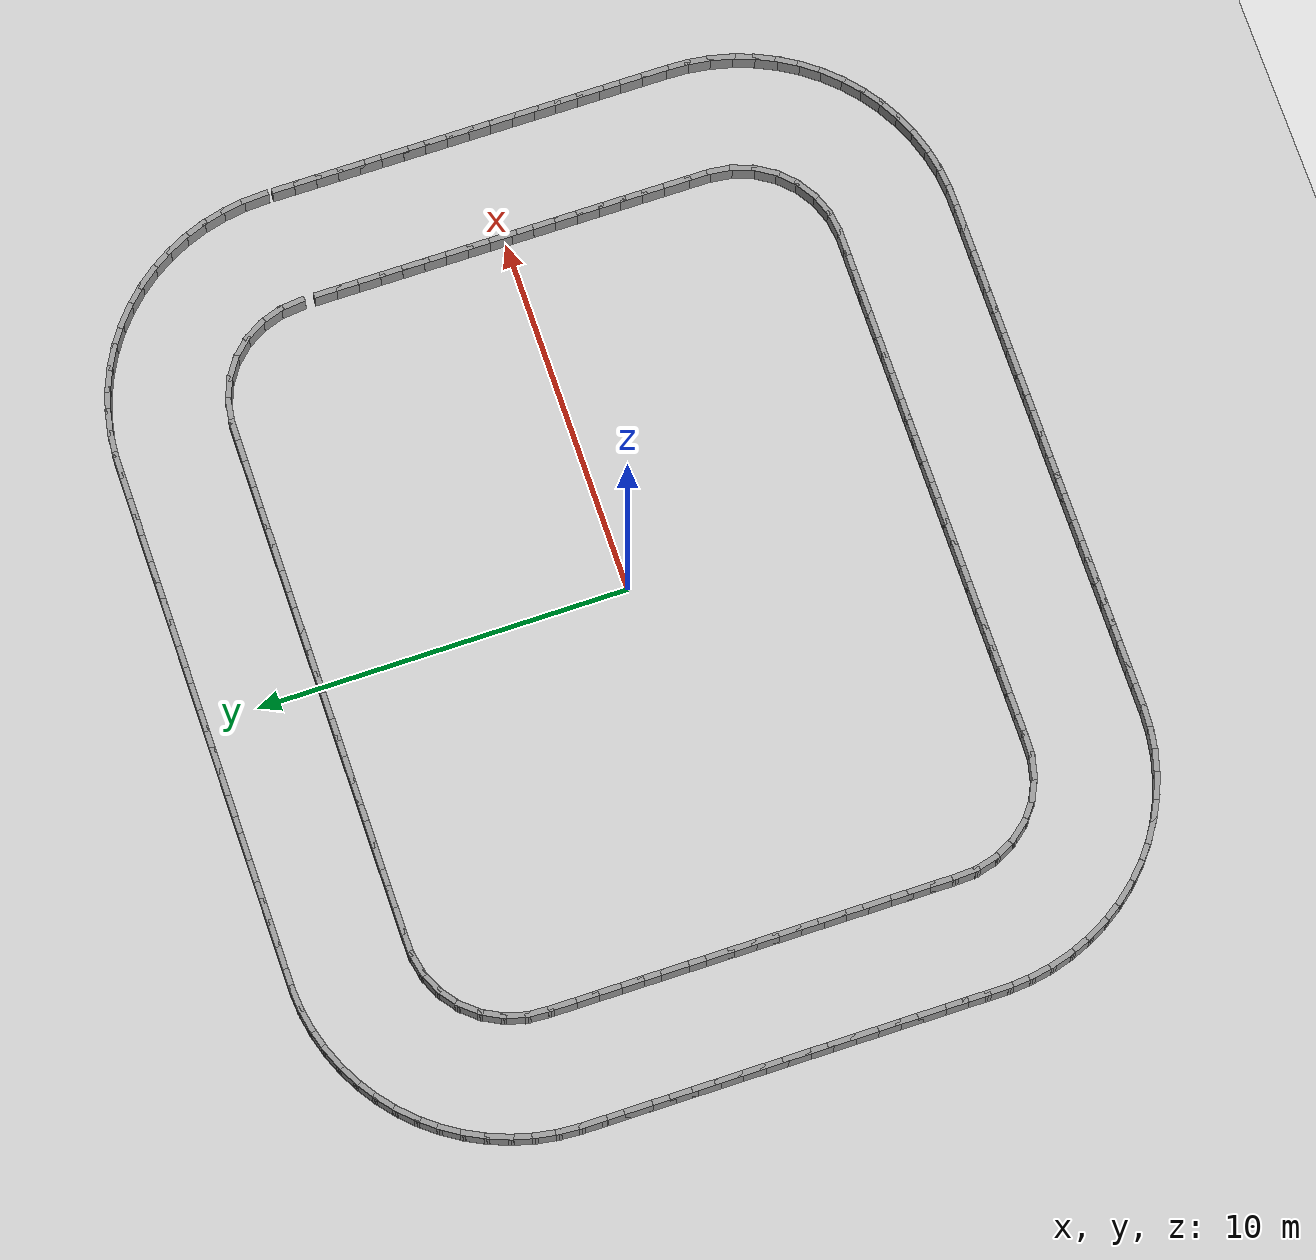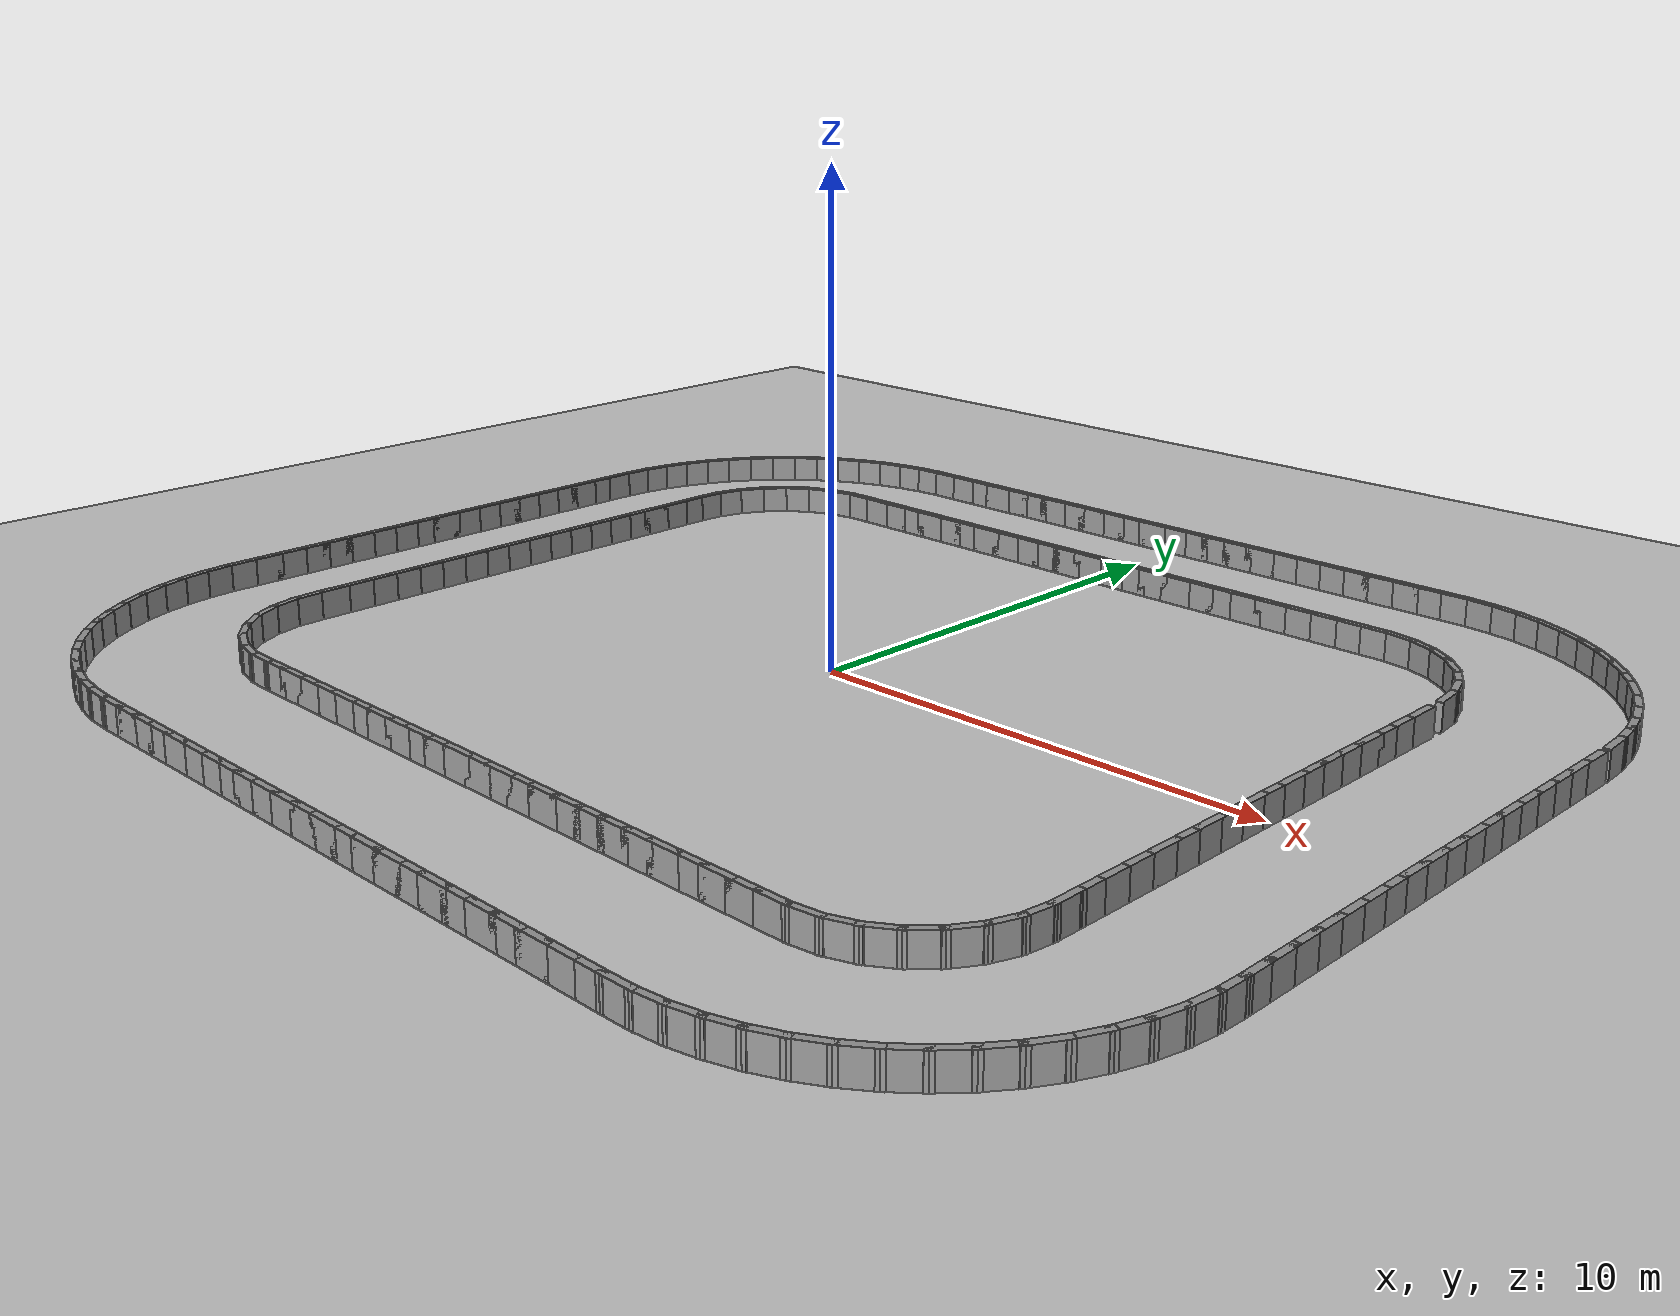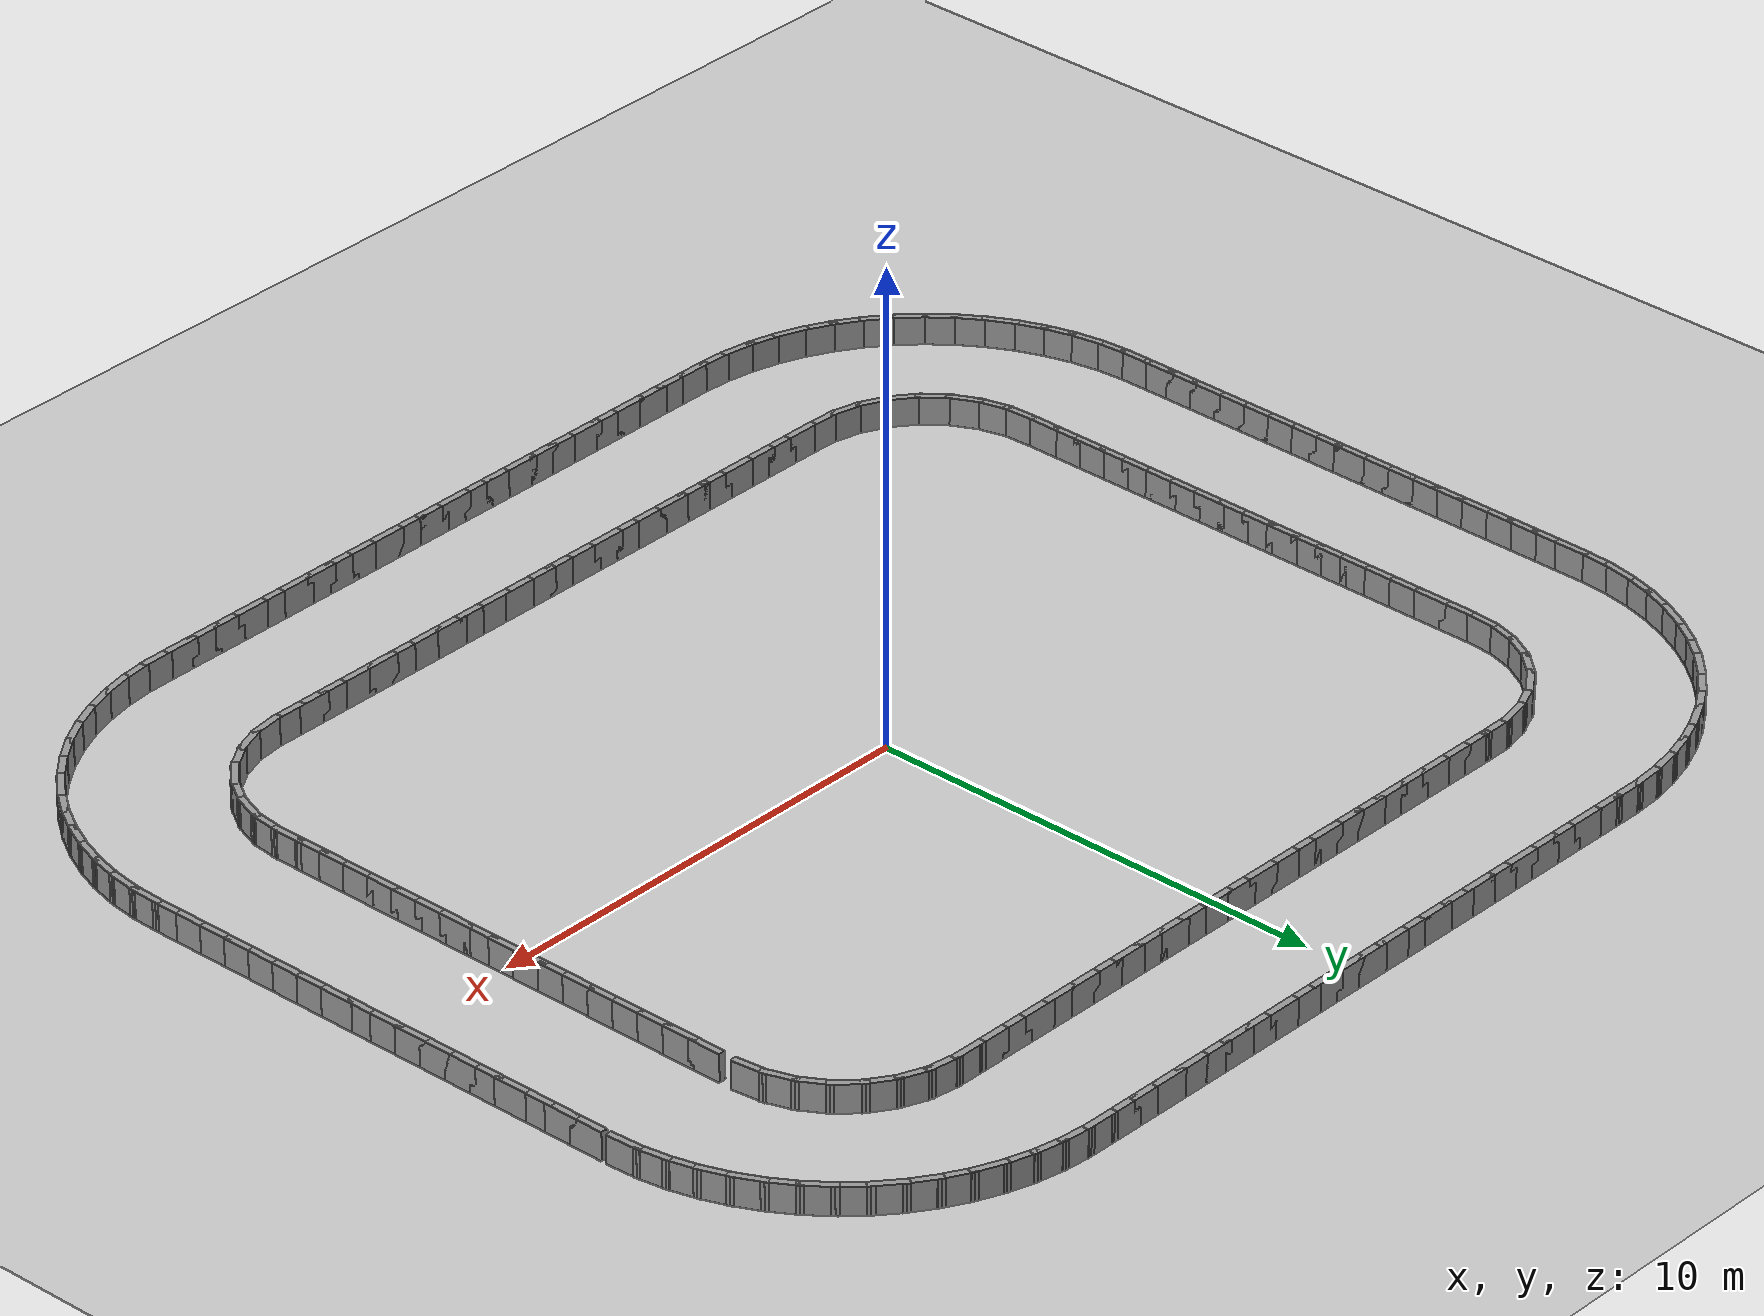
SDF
<?xml version="1.0" ?>
<sdf version='1.7'>
  <world name='default'>
    <plugin name='gazebo_ros_state' filename='libgazebo_ros_state.so'>
      <ros>
        <namespace>/</namespace>
      </ros>
      <update_rate>1000.0</update_rate>
    </plugin>

    <light name='sun' type='directional'>
      <cast_shadows>1</cast_shadows>
      <pose>0 0 10 0 -0 0</pose>
      <diffuse>0.8 0.8 0.8 1</diffuse>
      <specular>0.2 0.2 0.2 1</specular>
      <attenuation>
        <range>1000</range>
        <constant>0.9</constant>
        <linear>0.01</linear>
        <quadratic>0.001</quadratic>
      </attenuation>
      <direction>-0.5 0.1 -0.9</direction>
      <spot>
        <inner_angle>0</inner_angle>
        <outer_angle>0</outer_angle>
        <falloff>0</falloff>
      </spot>
    </light>
    <model name='ground_plane'>
      <static>1</static>
      <link name='link'>
        <collision name='collision'>
          <geometry>
            <plane>
              <normal>0 0 1</normal>
              <size>100 100</size>
            </plane>
          </geometry>
          <surface>
            <friction>
              <ode>
                <mu>100</mu>
                <mu2>50</mu2>
              </ode>
              <torsional>
                <ode/>
              </torsional>
            </friction>
            <contact>
              <ode/>
            </contact>
            <bounce/>
          </surface>
          <max_contacts>10</max_contacts>
        </collision>
        <visual name='visual'>
          <cast_shadows>0</cast_shadows>
          <geometry>
            <plane>
              <normal>0 0 1</normal>
              <size>100 100</size>
            </plane>
          </geometry>
          <material>
            <script>
              <uri>file://media/materials/scripts/gazebo.material</uri>
              <name>Gazebo/Grey</name>
            </script>
          </material>
        </visual>
        <self_collide>0</self_collide>
        <enable_wind>0</enable_wind>
        <kinematic>0</kinematic>
      </link>
    </model>
    <gravity>0 0 -9.8</gravity>
    <magnetic_field>6e-06 2.3e-05 -4.2e-05</magnetic_field>
    <atmosphere type='adiabatic'/>
    <physics type='ode'>
      <max_step_size>0.001</max_step_size>
      <real_time_factor>1</real_time_factor>
      <real_time_update_rate>1000</real_time_update_rate>
    </physics>
    <scene>
      <ambient>0.4 0.4 0.4 1</ambient>
      <background>0.7 0.7 0.7 1</background>
      <shadows>1</shadows>
    </scene>
    <audio>
      <device>default</device>
    </audio>
    <wind/>
    <spherical_coordinates>
      <surface_model>EARTH_WGS84</surface_model>
      <latitude_deg>0</latitude_deg>
      <longitude_deg>0</longitude_deg>
      <elevation>0</elevation>
      <heading_deg>0</heading_deg>
    </spherical_coordinates>
  <model name='rand_rrect_01'>
    <pose>0 0 0 0 -0 0</pose>
    <link name='Wall_0'>
      <collision name='Wall_0_Collision'>
        <geometry><box><size>0.7488 0.1500 0.6000</size></box></geometry>
        <pose>0 0 0.3000 0 -0 0</pose>
      </collision>
      <visual name='Wall_0_Visual'>
        <pose>0 0 0.3000 0 -0 0</pose>
        <geometry><box><size>0.7488 0.1500 0.6000</size></box></geometry>
        <material>
          <script>
            <uri>file://media/materials/scripts/gazebo.material</uri>
            <name>Gazebo/Grey</name>
          </script>
          <ambient>1 1 1 1</ambient>
        </material>
      </visual>
      <pose>10.0239 5.8810 0 0 -0 1.68030</pose>
    </link>
    <link name='Wall_1'>
      <collision name='Wall_1_Collision'>
        <geometry><box><size>0.7488 0.1500 0.6000</size></box></geometry>
        <pose>0 0 0.3000 0 -0 0</pose>
      </collision>
      <visual name='Wall_1_Visual'>
        <pose>0 0 0.3000 0 -0 0</pose>
        <geometry><box><size>0.7488 0.1500 0.6000</size></box></geometry>
        <material>
          <script>
            <uri>file://media/materials/scripts/gazebo.material</uri>
            <name>Gazebo/Grey</name>
          </script>
          <ambient>1 1 1 1</ambient>
        </material>
      </visual>
      <pose>9.8946 6.4620 0 0 -0 1.89928</pose>
    </link>
    <link name='Wall_2'>
      <collision name='Wall_2_Collision'>
        <geometry><box><size>0.7488 0.1500 0.6000</size></box></geometry>
        <pose>0 0 0.3000 0 -0 0</pose>
      </collision>
      <visual name='Wall_2_Visual'>
        <pose>0 0 0.3000 0 -0 0</pose>
        <geometry><box><size>0.7488 0.1500 0.6000</size></box></geometry>
        <material>
          <script>
            <uri>file://media/materials/scripts/gazebo.material</uri>
            <name>Gazebo/Grey</name>
          </script>
          <ambient>1 1 1 1</ambient>
        </material>
      </visual>
      <pose>9.6421 7.0011 0 0 -0 2.11827</pose>
    </link>
    <link name='Wall_3'>
      <collision name='Wall_3_Collision'>
        <geometry><box><size>0.7488 0.1500 0.6000</size></box></geometry>
        <pose>0 0 0.3000 0 -0 0</pose>
      </collision>
      <visual name='Wall_3_Visual'>
        <pose>0 0 0.3000 0 -0 0</pose>
        <geometry><box><size>0.7488 0.1500 0.6000</size></box></geometry>
        <material>
          <script>
            <uri>file://media/materials/scripts/gazebo.material</uri>
            <name>Gazebo/Grey</name>
          </script>
          <ambient>1 1 1 1</ambient>
        </material>
      </visual>
      <pose>9.2786 7.4724 0 0 -0 2.33728</pose>
    </link>
    <link name='Wall_4'>
      <collision name='Wall_4_Collision'>
        <geometry><box><size>0.7488 0.1500 0.6000</size></box></geometry>
        <pose>0 0 0.3000 0 -0 0</pose>
      </collision>
      <visual name='Wall_4_Visual'>
        <pose>0 0 0.3000 0 -0 0</pose>
        <geometry><box><size>0.7488 0.1500 0.6000</size></box></geometry>
        <material>
          <script>
            <uri>file://media/materials/scripts/gazebo.material</uri>
            <name>Gazebo/Grey</name>
          </script>
          <ambient>1 1 1 1</ambient>
        </material>
      </visual>
      <pose>8.8214 7.8535 0 0 -0 2.55626</pose>
    </link>
    <link name='Wall_5'>
      <collision name='Wall_5_Collision'>
        <geometry><box><size>0.7488 0.1500 0.6000</size></box></geometry>
        <pose>0 0 0.3000 0 -0 0</pose>
      </collision>
      <visual name='Wall_5_Visual'>
        <pose>0 0 0.3000 0 -0 0</pose>
        <geometry><box><size>0.7488 0.1500 0.6000</size></box></geometry>
        <material>
          <script>
            <uri>file://media/materials/scripts/gazebo.material</uri>
            <name>Gazebo/Grey</name>
          </script>
          <ambient>1 1 1 1</ambient>
        </material>
      </visual>
      <pose>8.2923 8.1261 0 0 -0 2.77525</pose>
    </link>
    <link name='Wall_6'>
      <collision name='Wall_6_Collision'>
        <geometry><box><size>0.7488 0.1500 0.6000</size></box></geometry>
        <pose>0 0 0.3000 0 -0 0</pose>
      </collision>
      <visual name='Wall_6_Visual'>
        <pose>0 0 0.3000 0 -0 0</pose>
        <geometry><box><size>0.7488 0.1500 0.6000</size></box></geometry>
        <material>
          <script>
            <uri>file://media/materials/scripts/gazebo.material</uri>
            <name>Gazebo/Grey</name>
          </script>
          <ambient>1 1 1 1</ambient>
        </material>
      </visual>
      <pose>7.7166 8.2773 0 0 -0 2.99426</pose>
    </link>
    <link name='Wall_7'>
      <collision name='Wall_7_Collision'>
        <geometry><box><size>0.7500 0.1500 0.6000</size></box></geometry>
        <pose>0 0 0.3000 0 -0 0</pose>
      </collision>
      <visual name='Wall_7_Visual'>
        <pose>0 0 0.3000 0 -0 0</pose>
        <geometry><box><size>0.7500 0.1500 0.6000</size></box></geometry>
        <material>
          <script>
            <uri>file://media/materials/scripts/gazebo.material</uri>
            <name>Gazebo/Grey</name>
          </script>
          <ambient>1 1 1 1</ambient>
        </material>
      </visual>
      <pose>7.1205 8.3223 0 0 -0 3.13831</pose>
    </link>
    <link name='Wall_8'>
      <collision name='Wall_8_Collision'>
        <geometry><box><size>0.7500 0.1500 0.6000</size></box></geometry>
        <pose>0 0 0.3000 0 -0 0</pose>
      </collision>
      <visual name='Wall_8_Visual'>
        <pose>0 0 0.3000 0 -0 0</pose>
        <geometry><box><size>0.7500 0.1500 0.6000</size></box></geometry>
        <material>
          <script>
            <uri>file://media/materials/scripts/gazebo.material</uri>
            <name>Gazebo/Grey</name>
          </script>
          <ambient>1 1 1 1</ambient>
        </material>
      </visual>
      <pose>6.5205 8.3232 0 0 -0 3.14159</pose>
    </link>
    <link name='Wall_9'>
      <collision name='Wall_9_Collision'>
        <geometry><box><size>0.7500 0.1500 0.6000</size></box></geometry>
        <pose>0 0 0.3000 0 -0 0</pose>
      </collision>
      <visual name='Wall_9_Visual'>
        <pose>0 0 0.3000 0 -0 0</pose>
        <geometry><box><size>0.7500 0.1500 0.6000</size></box></geometry>
        <material>
          <script>
            <uri>file://media/materials/scripts/gazebo.material</uri>
            <name>Gazebo/Grey</name>
          </script>
          <ambient>1 1 1 1</ambient>
        </material>
      </visual>
      <pose>5.9205 8.3232 0 0 -0 3.14159</pose>
    </link>
    <link name='Wall_10'>
      <collision name='Wall_10_Collision'>
        <geometry><box><size>0.7500 0.1500 0.6000</size></box></geometry>
        <pose>0 0 0.3000 0 -0 0</pose>
      </collision>
      <visual name='Wall_10_Visual'>
        <pose>0 0 0.3000 0 -0 0</pose>
        <geometry><box><size>0.7500 0.1500 0.6000</size></box></geometry>
        <material>
          <script>
            <uri>file://media/materials/scripts/gazebo.material</uri>
            <name>Gazebo/Grey</name>
          </script>
          <ambient>1 1 1 1</ambient>
        </material>
      </visual>
      <pose>5.3205 8.3232 0 0 -0 3.14159</pose>
    </link>
    <link name='Wall_11'>
      <collision name='Wall_11_Collision'>
        <geometry><box><size>0.7500 0.1500 0.6000</size></box></geometry>
        <pose>0 0 0.3000 0 -0 0</pose>
      </collision>
      <visual name='Wall_11_Visual'>
        <pose>0 0 0.3000 0 -0 0</pose>
        <geometry><box><size>0.7500 0.1500 0.6000</size></box></geometry>
        <material>
          <script>
            <uri>file://media/materials/scripts/gazebo.material</uri>
            <name>Gazebo/Grey</name>
          </script>
          <ambient>1 1 1 1</ambient>
        </material>
      </visual>
      <pose>4.7205 8.3232 0 0 -0 3.14159</pose>
    </link>
    <link name='Wall_12'>
      <collision name='Wall_12_Collision'>
        <geometry><box><size>0.7500 0.1500 0.6000</size></box></geometry>
        <pose>0 0 0.3000 0 -0 0</pose>
      </collision>
      <visual name='Wall_12_Visual'>
        <pose>0 0 0.3000 0 -0 0</pose>
        <geometry><box><size>0.7500 0.1500 0.6000</size></box></geometry>
        <material>
          <script>
            <uri>file://media/materials/scripts/gazebo.material</uri>
            <name>Gazebo/Grey</name>
          </script>
          <ambient>1 1 1 1</ambient>
        </material>
      </visual>
      <pose>4.1205 8.3232 0 0 -0 3.14159</pose>
    </link>
    <link name='Wall_13'>
      <collision name='Wall_13_Collision'>
        <geometry><box><size>0.7500 0.1500 0.6000</size></box></geometry>
        <pose>0 0 0.3000 0 -0 0</pose>
      </collision>
      <visual name='Wall_13_Visual'>
        <pose>0 0 0.3000 0 -0 0</pose>
        <geometry><box><size>0.7500 0.1500 0.6000</size></box></geometry>
        <material>
          <script>
            <uri>file://media/materials/scripts/gazebo.material</uri>
            <name>Gazebo/Grey</name>
          </script>
          <ambient>1 1 1 1</ambient>
        </material>
      </visual>
      <pose>3.5205 8.3232 0 0 -0 3.14159</pose>
    </link>
    <link name='Wall_14'>
      <collision name='Wall_14_Collision'>
        <geometry><box><size>0.7500 0.1500 0.6000</size></box></geometry>
        <pose>0 0 0.3000 0 -0 0</pose>
      </collision>
      <visual name='Wall_14_Visual'>
        <pose>0 0 0.3000 0 -0 0</pose>
        <geometry><box><size>0.7500 0.1500 0.6000</size></box></geometry>
        <material>
          <script>
            <uri>file://media/materials/scripts/gazebo.material</uri>
            <name>Gazebo/Grey</name>
          </script>
          <ambient>1 1 1 1</ambient>
        </material>
      </visual>
      <pose>2.9205 8.3232 0 0 -0 3.14159</pose>
    </link>
    <link name='Wall_15'>
      <collision name='Wall_15_Collision'>
        <geometry><box><size>0.7500 0.1500 0.6000</size></box></geometry>
        <pose>0 0 0.3000 0 -0 0</pose>
      </collision>
      <visual name='Wall_15_Visual'>
        <pose>0 0 0.3000 0 -0 0</pose>
        <geometry><box><size>0.7500 0.1500 0.6000</size></box></geometry>
        <material>
          <script>
            <uri>file://media/materials/scripts/gazebo.material</uri>
            <name>Gazebo/Grey</name>
          </script>
          <ambient>1 1 1 1</ambient>
        </material>
      </visual>
      <pose>2.3205 8.3232 0 0 -0 3.14159</pose>
    </link>
    <link name='Wall_16'>
      <collision name='Wall_16_Collision'>
        <geometry><box><size>0.7500 0.1500 0.6000</size></box></geometry>
        <pose>0 0 0.3000 0 -0 0</pose>
      </collision>
      <visual name='Wall_16_Visual'>
        <pose>0 0 0.3000 0 -0 0</pose>
        <geometry><box><size>0.7500 0.1500 0.6000</size></box></geometry>
        <material>
          <script>
            <uri>file://media/materials/scripts/gazebo.material</uri>
            <name>Gazebo/Grey</name>
          </script>
          <ambient>1 1 1 1</ambient>
        </material>
      </visual>
      <pose>1.7205 8.3232 0 0 -0 3.14159</pose>
    </link>
    <link name='Wall_17'>
      <collision name='Wall_17_Collision'>
        <geometry><box><size>0.7500 0.1500 0.6000</size></box></geometry>
        <pose>0 0 0.3000 0 -0 0</pose>
      </collision>
      <visual name='Wall_17_Visual'>
        <pose>0 0 0.3000 0 -0 0</pose>
        <geometry><box><size>0.7500 0.1500 0.6000</size></box></geometry>
        <material>
          <script>
            <uri>file://media/materials/scripts/gazebo.material</uri>
            <name>Gazebo/Grey</name>
          </script>
          <ambient>1 1 1 1</ambient>
        </material>
      </visual>
      <pose>1.1205 8.3232 0 0 -0 3.14159</pose>
    </link>
    <link name='Wall_18'>
      <collision name='Wall_18_Collision'>
        <geometry><box><size>0.7500 0.1500 0.6000</size></box></geometry>
        <pose>0 0 0.3000 0 -0 0</pose>
      </collision>
      <visual name='Wall_18_Visual'>
        <pose>0 0 0.3000 0 -0 0</pose>
        <geometry><box><size>0.7500 0.1500 0.6000</size></box></geometry>
        <material>
          <script>
            <uri>file://media/materials/scripts/gazebo.material</uri>
            <name>Gazebo/Grey</name>
          </script>
          <ambient>1 1 1 1</ambient>
        </material>
      </visual>
      <pose>0.5205 8.3232 0 0 -0 3.14159</pose>
    </link>
    <link name='Wall_19'>
      <collision name='Wall_19_Collision'>
        <geometry><box><size>0.7500 0.1500 0.6000</size></box></geometry>
        <pose>0 0 0.3000 0 -0 0</pose>
      </collision>
      <visual name='Wall_19_Visual'>
        <pose>0 0 0.3000 0 -0 0</pose>
        <geometry><box><size>0.7500 0.1500 0.6000</size></box></geometry>
        <material>
          <script>
            <uri>file://media/materials/scripts/gazebo.material</uri>
            <name>Gazebo/Grey</name>
          </script>
          <ambient>1 1 1 1</ambient>
        </material>
      </visual>
      <pose>-0.0795 8.3232 0 0 -0 3.14159</pose>
    </link>
    <link name='Wall_20'>
      <collision name='Wall_20_Collision'>
        <geometry><box><size>0.7500 0.1500 0.6000</size></box></geometry>
        <pose>0 0 0.3000 0 -0 0</pose>
      </collision>
      <visual name='Wall_20_Visual'>
        <pose>0 0 0.3000 0 -0 0</pose>
        <geometry><box><size>0.7500 0.1500 0.6000</size></box></geometry>
        <material>
          <script>
            <uri>file://media/materials/scripts/gazebo.material</uri>
            <name>Gazebo/Grey</name>
          </script>
          <ambient>1 1 1 1</ambient>
        </material>
      </visual>
      <pose>-0.6795 8.3232 0 0 -0 3.14159</pose>
    </link>
    <link name='Wall_21'>
      <collision name='Wall_21_Collision'>
        <geometry><box><size>0.7500 0.1500 0.6000</size></box></geometry>
        <pose>0 0 0.3000 0 -0 0</pose>
      </collision>
      <visual name='Wall_21_Visual'>
        <pose>0 0 0.3000 0 -0 0</pose>
        <geometry><box><size>0.7500 0.1500 0.6000</size></box></geometry>
        <material>
          <script>
            <uri>file://media/materials/scripts/gazebo.material</uri>
            <name>Gazebo/Grey</name>
          </script>
          <ambient>1 1 1 1</ambient>
        </material>
      </visual>
      <pose>-1.2795 8.3232 0 0 -0 3.14159</pose>
    </link>
    <link name='Wall_22'>
      <collision name='Wall_22_Collision'>
        <geometry><box><size>0.7500 0.1500 0.6000</size></box></geometry>
        <pose>0 0 0.3000 0 -0 0</pose>
      </collision>
      <visual name='Wall_22_Visual'>
        <pose>0 0 0.3000 0 -0 0</pose>
        <geometry><box><size>0.7500 0.1500 0.6000</size></box></geometry>
        <material>
          <script>
            <uri>file://media/materials/scripts/gazebo.material</uri>
            <name>Gazebo/Grey</name>
          </script>
          <ambient>1 1 1 1</ambient>
        </material>
      </visual>
      <pose>-1.8795 8.3232 0 0 -0 3.14159</pose>
    </link>
    <link name='Wall_23'>
      <collision name='Wall_23_Collision'>
        <geometry><box><size>0.7500 0.1500 0.6000</size></box></geometry>
        <pose>0 0 0.3000 0 -0 0</pose>
      </collision>
      <visual name='Wall_23_Visual'>
        <pose>0 0 0.3000 0 -0 0</pose>
        <geometry><box><size>0.7500 0.1500 0.6000</size></box></geometry>
        <material>
          <script>
            <uri>file://media/materials/scripts/gazebo.material</uri>
            <name>Gazebo/Grey</name>
          </script>
          <ambient>1 1 1 1</ambient>
        </material>
      </visual>
      <pose>-2.4795 8.3232 0 0 -0 3.14159</pose>
    </link>
    <link name='Wall_24'>
      <collision name='Wall_24_Collision'>
        <geometry><box><size>0.7500 0.1500 0.6000</size></box></geometry>
        <pose>0 0 0.3000 0 -0 0</pose>
      </collision>
      <visual name='Wall_24_Visual'>
        <pose>0 0 0.3000 0 -0 0</pose>
        <geometry><box><size>0.7500 0.1500 0.6000</size></box></geometry>
        <material>
          <script>
            <uri>file://media/materials/scripts/gazebo.material</uri>
            <name>Gazebo/Grey</name>
          </script>
          <ambient>1 1 1 1</ambient>
        </material>
      </visual>
      <pose>-3.0795 8.3232 0 0 -0 3.14159</pose>
    </link>
    <link name='Wall_25'>
      <collision name='Wall_25_Collision'>
        <geometry><box><size>0.7500 0.1500 0.6000</size></box></geometry>
        <pose>0 0 0.3000 0 -0 0</pose>
      </collision>
      <visual name='Wall_25_Visual'>
        <pose>0 0 0.3000 0 -0 0</pose>
        <geometry><box><size>0.7500 0.1500 0.6000</size></box></geometry>
        <material>
          <script>
            <uri>file://media/materials/scripts/gazebo.material</uri>
            <name>Gazebo/Grey</name>
          </script>
          <ambient>1 1 1 1</ambient>
        </material>
      </visual>
      <pose>-3.6795 8.3232 0 0 -0 3.14159</pose>
    </link>
    <link name='Wall_26'>
      <collision name='Wall_26_Collision'>
        <geometry><box><size>0.7500 0.1500 0.6000</size></box></geometry>
        <pose>0 0 0.3000 0 -0 0</pose>
      </collision>
      <visual name='Wall_26_Visual'>
        <pose>0 0 0.3000 0 -0 0</pose>
        <geometry><box><size>0.7500 0.1500 0.6000</size></box></geometry>
        <material>
          <script>
            <uri>file://media/materials/scripts/gazebo.material</uri>
            <name>Gazebo/Grey</name>
          </script>
          <ambient>1 1 1 1</ambient>
        </material>
      </visual>
      <pose>-4.2795 8.3232 0 0 -0 3.14159</pose>
    </link>
    <link name='Wall_27'>
      <collision name='Wall_27_Collision'>
        <geometry><box><size>0.7500 0.1500 0.6000</size></box></geometry>
        <pose>0 0 0.3000 0 -0 0</pose>
      </collision>
      <visual name='Wall_27_Visual'>
        <pose>0 0 0.3000 0 -0 0</pose>
        <geometry><box><size>0.7500 0.1500 0.6000</size></box></geometry>
        <material>
          <script>
            <uri>file://media/materials/scripts/gazebo.material</uri>
            <name>Gazebo/Grey</name>
          </script>
          <ambient>1 1 1 1</ambient>
        </material>
      </visual>
      <pose>-4.8795 8.3232 0 0 -0 3.14159</pose>
    </link>
    <link name='Wall_28'>
      <collision name='Wall_28_Collision'>
        <geometry><box><size>0.7500 0.1500 0.6000</size></box></geometry>
        <pose>0 0 0.3000 0 -0 0</pose>
      </collision>
      <visual name='Wall_28_Visual'>
        <pose>0 0 0.3000 0 -0 0</pose>
        <geometry><box><size>0.7500 0.1500 0.6000</size></box></geometry>
        <material>
          <script>
            <uri>file://media/materials/scripts/gazebo.material</uri>
            <name>Gazebo/Grey</name>
          </script>
          <ambient>1 1 1 1</ambient>
        </material>
      </visual>
      <pose>-5.4795 8.3232 0 0 -0 3.14159</pose>
    </link>
    <link name='Wall_29'>
      <collision name='Wall_29_Collision'>
        <geometry><box><size>0.7500 0.1500 0.6000</size></box></geometry>
        <pose>0 0 0.3000 0 -0 0</pose>
      </collision>
      <visual name='Wall_29_Visual'>
        <pose>0 0 0.3000 0 -0 0</pose>
        <geometry><box><size>0.7500 0.1500 0.6000</size></box></geometry>
        <material>
          <script>
            <uri>file://media/materials/scripts/gazebo.material</uri>
            <name>Gazebo/Grey</name>
          </script>
          <ambient>1 1 1 1</ambient>
        </material>
      </visual>
      <pose>-6.0795 8.3232 0 0 -0 3.14159</pose>
    </link>
    <link name='Wall_30'>
      <collision name='Wall_30_Collision'>
        <geometry><box><size>0.7500 0.1500 0.6000</size></box></geometry>
        <pose>0 0 0.3000 0 -0 0</pose>
      </collision>
      <visual name='Wall_30_Visual'>
        <pose>0 0 0.3000 0 -0 0</pose>
        <geometry><box><size>0.7500 0.1500 0.6000</size></box></geometry>
        <material>
          <script>
            <uri>file://media/materials/scripts/gazebo.material</uri>
            <name>Gazebo/Grey</name>
          </script>
          <ambient>1 1 1 1</ambient>
        </material>
      </visual>
      <pose>-6.6795 8.3232 0 0 -0 3.14159</pose>
    </link>
    <link name='Wall_31'>
      <collision name='Wall_31_Collision'>
        <geometry><box><size>0.7497 0.1500 0.6000</size></box></geometry>
        <pose>0 0 0.3000 0 -0 0</pose>
      </collision>
      <visual name='Wall_31_Visual'>
        <pose>0 0 0.3000 0 -0 0</pose>
        <geometry><box><size>0.7497 0.1500 0.6000</size></box></geometry>
        <material>
          <script>
            <uri>file://media/materials/scripts/gazebo.material</uri>
            <name>Gazebo/Grey</name>
          </script>
          <ambient>1 1 1 1</ambient>
        </material>
      </visual>
      <pose>-7.2793 8.3170 0 0 -0 -3.12059</pose>
    </link>
    <link name='Wall_32'>
      <collision name='Wall_32_Collision'>
        <geometry><box><size>0.7488 0.1500 0.6000</size></box></geometry>
        <pose>0 0 0.3000 0 -0 0</pose>
      </collision>
      <visual name='Wall_32_Visual'>
        <pose>0 0 0.3000 0 -0 0</pose>
        <geometry><box><size>0.7488 0.1500 0.6000</size></box></geometry>
        <material>
          <script>
            <uri>file://media/materials/scripts/gazebo.material</uri>
            <name>Gazebo/Grey</name>
          </script>
          <ambient>1 1 1 1</ambient>
        </material>
      </visual>
      <pose>-7.8722 8.2496 0 0 -0 -2.93620</pose>
    </link>
    <link name='Wall_33'>
      <collision name='Wall_33_Collision'>
        <geometry><box><size>0.7488 0.1500 0.6000</size></box></geometry>
        <pose>0 0 0.3000 0 -0 0</pose>
      </collision>
      <visual name='Wall_33_Visual'>
        <pose>0 0 0.3000 0 -0 0</pose>
        <geometry><box><size>0.7488 0.1500 0.6000</size></box></geometry>
        <material>
          <script>
            <uri>file://media/materials/scripts/gazebo.material</uri>
            <name>Gazebo/Grey</name>
          </script>
          <ambient>1 1 1 1</ambient>
        </material>
      </visual>
      <pose>-8.4382 8.0652 0 0 -0 -2.71719</pose>
    </link>
    <link name='Wall_34'>
      <collision name='Wall_34_Collision'>
        <geometry><box><size>0.7488 0.1500 0.6000</size></box></geometry>
        <pose>0 0 0.3000 0 -0 0</pose>
      </collision>
      <visual name='Wall_34_Visual'>
        <pose>0 0 0.3000 0 -0 0</pose>
        <geometry><box><size>0.7488 0.1500 0.6000</size></box></geometry>
        <material>
          <script>
            <uri>file://media/materials/scripts/gazebo.material</uri>
            <name>Gazebo/Grey</name>
          </script>
          <ambient>1 1 1 1</ambient>
        </material>
      </visual>
      <pose>-8.9506 7.7623 0 0 -0 -2.49821</pose>
    </link>
    <link name='Wall_35'>
      <collision name='Wall_35_Collision'>
        <geometry><box><size>0.7488 0.1500 0.6000</size></box></geometry>
        <pose>0 0 0.3000 0 -0 0</pose>
      </collision>
      <visual name='Wall_35_Visual'>
        <pose>0 0 0.3000 0 -0 0</pose>
        <geometry><box><size>0.7488 0.1500 0.6000</size></box></geometry>
        <material>
          <script>
            <uri>file://media/materials/scripts/gazebo.material</uri>
            <name>Gazebo/Grey</name>
          </script>
          <ambient>1 1 1 1</ambient>
        </material>
      </visual>
      <pose>-9.3849 7.3554 0 0 -0 -2.27922</pose>
    </link>
    <link name='Wall_36'>
      <collision name='Wall_36_Collision'>
        <geometry><box><size>0.7488 0.1500 0.6000</size></box></geometry>
        <pose>0 0 0.3000 0 -0 0</pose>
      </collision>
      <visual name='Wall_36_Visual'>
        <pose>0 0 0.3000 0 -0 0</pose>
        <geometry><box><size>0.7488 0.1500 0.6000</size></box></geometry>
        <material>
          <script>
            <uri>file://media/materials/scripts/gazebo.material</uri>
            <name>Gazebo/Grey</name>
          </script>
          <ambient>1 1 1 1</ambient>
        </material>
      </visual>
      <pose>-9.7205 6.8638 0 0 -0 -2.06021</pose>
    </link>
    <link name='Wall_37'>
      <collision name='Wall_37_Collision'>
        <geometry><box><size>0.7488 0.1500 0.6000</size></box></geometry>
        <pose>0 0 0.3000 0 -0 0</pose>
      </collision>
      <visual name='Wall_37_Visual'>
        <pose>0 0 0.3000 0 -0 0</pose>
        <geometry><box><size>0.7488 0.1500 0.6000</size></box></geometry>
        <material>
          <script>
            <uri>file://media/materials/scripts/gazebo.material</uri>
            <name>Gazebo/Grey</name>
          </script>
          <ambient>1 1 1 1</ambient>
        </material>
      </visual>
      <pose>-9.9412 6.3110 0 0 -0 -1.84123</pose>
    </link>
    <link name='Wall_38'>
      <collision name='Wall_38_Collision'>
        <geometry><box><size>0.7491 0.1500 0.6000</size></box></geometry>
        <pose>0 0 0.3000 0 -0 0</pose>
      </collision>
      <visual name='Wall_38_Visual'>
        <pose>0 0 0.3000 0 -0 0</pose>
        <geometry><box><size>0.7491 0.1500 0.6000</size></box></geometry>
        <material>
          <script>
            <uri>file://media/materials/scripts/gazebo.material</uri>
            <name>Gazebo/Grey</name>
          </script>
          <ambient>1 1 1 1</ambient>
        </material>
      </visual>
      <pose>-10.0389 5.7234 0 0 -0 -1.62993</pose>
    </link>
    <link name='Wall_39'>
      <collision name='Wall_39_Collision'>
        <geometry><box><size>0.7500 0.1500 0.6000</size></box></geometry>
        <pose>0 0 0.3000 0 -0 0</pose>
      </collision>
      <visual name='Wall_39_Visual'>
        <pose>0 0 0.3000 0 -0 0</pose>
        <geometry><box><size>0.7500 0.1500 0.6000</size></box></geometry>
        <material>
          <script>
            <uri>file://media/materials/scripts/gazebo.material</uri>
            <name>Gazebo/Grey</name>
          </script>
          <ambient>1 1 1 1</ambient>
        </material>
      </visual>
      <pose>-10.0566 5.1244 0 0 -0 -1.57080</pose>
    </link>
    <link name='Wall_40'>
      <collision name='Wall_40_Collision'>
        <geometry><box><size>0.7500 0.1500 0.6000</size></box></geometry>
        <pose>0 0 0.3000 0 -0 0</pose>
      </collision>
      <visual name='Wall_40_Visual'>
        <pose>0 0 0.3000 0 -0 0</pose>
        <geometry><box><size>0.7500 0.1500 0.6000</size></box></geometry>
        <material>
          <script>
            <uri>file://media/materials/scripts/gazebo.material</uri>
            <name>Gazebo/Grey</name>
          </script>
          <ambient>1 1 1 1</ambient>
        </material>
      </visual>
      <pose>-10.0566 4.5244 0 0 -0 -1.57080</pose>
    </link>
    <link name='Wall_41'>
      <collision name='Wall_41_Collision'>
        <geometry><box><size>0.7500 0.1500 0.6000</size></box></geometry>
        <pose>0 0 0.3000 0 -0 0</pose>
      </collision>
      <visual name='Wall_41_Visual'>
        <pose>0 0 0.3000 0 -0 0</pose>
        <geometry><box><size>0.7500 0.1500 0.6000</size></box></geometry>
        <material>
          <script>
            <uri>file://media/materials/scripts/gazebo.material</uri>
            <name>Gazebo/Grey</name>
          </script>
          <ambient>1 1 1 1</ambient>
        </material>
      </visual>
      <pose>-10.0566 3.9244 0 0 -0 -1.57080</pose>
    </link>
    <link name='Wall_42'>
      <collision name='Wall_42_Collision'>
        <geometry><box><size>0.7500 0.1500 0.6000</size></box></geometry>
        <pose>0 0 0.3000 0 -0 0</pose>
      </collision>
      <visual name='Wall_42_Visual'>
        <pose>0 0 0.3000 0 -0 0</pose>
        <geometry><box><size>0.7500 0.1500 0.6000</size></box></geometry>
        <material>
          <script>
            <uri>file://media/materials/scripts/gazebo.material</uri>
            <name>Gazebo/Grey</name>
          </script>
          <ambient>1 1 1 1</ambient>
        </material>
      </visual>
      <pose>-10.0566 3.3244 0 0 -0 -1.57080</pose>
    </link>
    <link name='Wall_43'>
      <collision name='Wall_43_Collision'>
        <geometry><box><size>0.7500 0.1500 0.6000</size></box></geometry>
        <pose>0 0 0.3000 0 -0 0</pose>
      </collision>
      <visual name='Wall_43_Visual'>
        <pose>0 0 0.3000 0 -0 0</pose>
        <geometry><box><size>0.7500 0.1500 0.6000</size></box></geometry>
        <material>
          <script>
            <uri>file://media/materials/scripts/gazebo.material</uri>
            <name>Gazebo/Grey</name>
          </script>
          <ambient>1 1 1 1</ambient>
        </material>
      </visual>
      <pose>-10.0566 2.7244 0 0 -0 -1.57080</pose>
    </link>
    <link name='Wall_44'>
      <collision name='Wall_44_Collision'>
        <geometry><box><size>0.7500 0.1500 0.6000</size></box></geometry>
        <pose>0 0 0.3000 0 -0 0</pose>
      </collision>
      <visual name='Wall_44_Visual'>
        <pose>0 0 0.3000 0 -0 0</pose>
        <geometry><box><size>0.7500 0.1500 0.6000</size></box></geometry>
        <material>
          <script>
            <uri>file://media/materials/scripts/gazebo.material</uri>
            <name>Gazebo/Grey</name>
          </script>
          <ambient>1 1 1 1</ambient>
        </material>
      </visual>
      <pose>-10.0566 2.1244 0 0 -0 -1.57080</pose>
    </link>
    <link name='Wall_45'>
      <collision name='Wall_45_Collision'>
        <geometry><box><size>0.7500 0.1500 0.6000</size></box></geometry>
        <pose>0 0 0.3000 0 -0 0</pose>
      </collision>
      <visual name='Wall_45_Visual'>
        <pose>0 0 0.3000 0 -0 0</pose>
        <geometry><box><size>0.7500 0.1500 0.6000</size></box></geometry>
        <material>
          <script>
            <uri>file://media/materials/scripts/gazebo.material</uri>
            <name>Gazebo/Grey</name>
          </script>
          <ambient>1 1 1 1</ambient>
        </material>
      </visual>
      <pose>-10.0566 1.5244 0 0 -0 -1.57080</pose>
    </link>
    <link name='Wall_46'>
      <collision name='Wall_46_Collision'>
        <geometry><box><size>0.7500 0.1500 0.6000</size></box></geometry>
        <pose>0 0 0.3000 0 -0 0</pose>
      </collision>
      <visual name='Wall_46_Visual'>
        <pose>0 0 0.3000 0 -0 0</pose>
        <geometry><box><size>0.7500 0.1500 0.6000</size></box></geometry>
        <material>
          <script>
            <uri>file://media/materials/scripts/gazebo.material</uri>
            <name>Gazebo/Grey</name>
          </script>
          <ambient>1 1 1 1</ambient>
        </material>
      </visual>
      <pose>-10.0566 0.9244 0 0 -0 -1.57080</pose>
    </link>
    <link name='Wall_47'>
      <collision name='Wall_47_Collision'>
        <geometry><box><size>0.7500 0.1500 0.6000</size></box></geometry>
        <pose>0 0 0.3000 0 -0 0</pose>
      </collision>
      <visual name='Wall_47_Visual'>
        <pose>0 0 0.3000 0 -0 0</pose>
        <geometry><box><size>0.7500 0.1500 0.6000</size></box></geometry>
        <material>
          <script>
            <uri>file://media/materials/scripts/gazebo.material</uri>
            <name>Gazebo/Grey</name>
          </script>
          <ambient>1 1 1 1</ambient>
        </material>
      </visual>
      <pose>-10.0566 0.3244 0 0 -0 -1.57080</pose>
    </link>
    <link name='Wall_48'>
      <collision name='Wall_48_Collision'>
        <geometry><box><size>0.7500 0.1500 0.6000</size></box></geometry>
        <pose>0 0 0.3000 0 -0 0</pose>
      </collision>
      <visual name='Wall_48_Visual'>
        <pose>0 0 0.3000 0 -0 0</pose>
        <geometry><box><size>0.7500 0.1500 0.6000</size></box></geometry>
        <material>
          <script>
            <uri>file://media/materials/scripts/gazebo.material</uri>
            <name>Gazebo/Grey</name>
          </script>
          <ambient>1 1 1 1</ambient>
        </material>
      </visual>
      <pose>-10.0566 -0.2756 0 0 -0 -1.57080</pose>
    </link>
    <link name='Wall_49'>
      <collision name='Wall_49_Collision'>
        <geometry><box><size>0.7500 0.1500 0.6000</size></box></geometry>
        <pose>0 0 0.3000 0 -0 0</pose>
      </collision>
      <visual name='Wall_49_Visual'>
        <pose>0 0 0.3000 0 -0 0</pose>
        <geometry><box><size>0.7500 0.1500 0.6000</size></box></geometry>
        <material>
          <script>
            <uri>file://media/materials/scripts/gazebo.material</uri>
            <name>Gazebo/Grey</name>
          </script>
          <ambient>1 1 1 1</ambient>
        </material>
      </visual>
      <pose>-10.0566 -0.8756 0 0 -0 -1.57080</pose>
    </link>
    <link name='Wall_50'>
      <collision name='Wall_50_Collision'>
        <geometry><box><size>0.7500 0.1500 0.6000</size></box></geometry>
        <pose>0 0 0.3000 0 -0 0</pose>
      </collision>
      <visual name='Wall_50_Visual'>
        <pose>0 0 0.3000 0 -0 0</pose>
        <geometry><box><size>0.7500 0.1500 0.6000</size></box></geometry>
        <material>
          <script>
            <uri>file://media/materials/scripts/gazebo.material</uri>
            <name>Gazebo/Grey</name>
          </script>
          <ambient>1 1 1 1</ambient>
        </material>
      </visual>
      <pose>-10.0566 -1.4756 0 0 -0 -1.57080</pose>
    </link>
    <link name='Wall_51'>
      <collision name='Wall_51_Collision'>
        <geometry><box><size>0.7500 0.1500 0.6000</size></box></geometry>
        <pose>0 0 0.3000 0 -0 0</pose>
      </collision>
      <visual name='Wall_51_Visual'>
        <pose>0 0 0.3000 0 -0 0</pose>
        <geometry><box><size>0.7500 0.1500 0.6000</size></box></geometry>
        <material>
          <script>
            <uri>file://media/materials/scripts/gazebo.material</uri>
            <name>Gazebo/Grey</name>
          </script>
          <ambient>1 1 1 1</ambient>
        </material>
      </visual>
      <pose>-10.0566 -2.0756 0 0 -0 -1.57080</pose>
    </link>
    <link name='Wall_52'>
      <collision name='Wall_52_Collision'>
        <geometry><box><size>0.7500 0.1500 0.6000</size></box></geometry>
        <pose>0 0 0.3000 0 -0 0</pose>
      </collision>
      <visual name='Wall_52_Visual'>
        <pose>0 0 0.3000 0 -0 0</pose>
        <geometry><box><size>0.7500 0.1500 0.6000</size></box></geometry>
        <material>
          <script>
            <uri>file://media/materials/scripts/gazebo.material</uri>
            <name>Gazebo/Grey</name>
          </script>
          <ambient>1 1 1 1</ambient>
        </material>
      </visual>
      <pose>-10.0566 -2.6756 0 0 -0 -1.57080</pose>
    </link>
    <link name='Wall_53'>
      <collision name='Wall_53_Collision'>
        <geometry><box><size>0.7500 0.1500 0.6000</size></box></geometry>
        <pose>0 0 0.3000 0 -0 0</pose>
      </collision>
      <visual name='Wall_53_Visual'>
        <pose>0 0 0.3000 0 -0 0</pose>
        <geometry><box><size>0.7500 0.1500 0.6000</size></box></geometry>
        <material>
          <script>
            <uri>file://media/materials/scripts/gazebo.material</uri>
            <name>Gazebo/Grey</name>
          </script>
          <ambient>1 1 1 1</ambient>
        </material>
      </visual>
      <pose>-10.0566 -3.2756 0 0 -0 -1.57080</pose>
    </link>
    <link name='Wall_54'>
      <collision name='Wall_54_Collision'>
        <geometry><box><size>0.7500 0.1500 0.6000</size></box></geometry>
        <pose>0 0 0.3000 0 -0 0</pose>
      </collision>
      <visual name='Wall_54_Visual'>
        <pose>0 0 0.3000 0 -0 0</pose>
        <geometry><box><size>0.7500 0.1500 0.6000</size></box></geometry>
        <material>
          <script>
            <uri>file://media/materials/scripts/gazebo.material</uri>
            <name>Gazebo/Grey</name>
          </script>
          <ambient>1 1 1 1</ambient>
        </material>
      </visual>
      <pose>-10.0566 -3.8756 0 0 -0 -1.57080</pose>
    </link>
    <link name='Wall_55'>
      <collision name='Wall_55_Collision'>
        <geometry><box><size>0.7500 0.1500 0.6000</size></box></geometry>
        <pose>0 0 0.3000 0 -0 0</pose>
      </collision>
      <visual name='Wall_55_Visual'>
        <pose>0 0 0.3000 0 -0 0</pose>
        <geometry><box><size>0.7500 0.1500 0.6000</size></box></geometry>
        <material>
          <script>
            <uri>file://media/materials/scripts/gazebo.material</uri>
            <name>Gazebo/Grey</name>
          </script>
          <ambient>1 1 1 1</ambient>
        </material>
      </visual>
      <pose>-10.0566 -4.4756 0 0 -0 -1.57080</pose>
    </link>
    <link name='Wall_56'>
      <collision name='Wall_56_Collision'>
        <geometry><box><size>0.7500 0.1500 0.6000</size></box></geometry>
        <pose>0 0 0.3000 0 -0 0</pose>
      </collision>
      <visual name='Wall_56_Visual'>
        <pose>0 0 0.3000 0 -0 0</pose>
        <geometry><box><size>0.7500 0.1500 0.6000</size></box></geometry>
        <material>
          <script>
            <uri>file://media/materials/scripts/gazebo.material</uri>
            <name>Gazebo/Grey</name>
          </script>
          <ambient>1 1 1 1</ambient>
        </material>
      </visual>
      <pose>-10.0566 -5.0756 0 0 -0 -1.57080</pose>
    </link>
    <link name='Wall_57'>
      <collision name='Wall_57_Collision'>
        <geometry><box><size>0.7493 0.1500 0.6000</size></box></geometry>
        <pose>0 0 0.3000 0 -0 0</pose>
      </collision>
      <visual name='Wall_57_Visual'>
        <pose>0 0 0.3000 0 -0 0</pose>
        <geometry><box><size>0.7493 0.1500 0.6000</size></box></geometry>
        <material>
          <script>
            <uri>file://media/materials/scripts/gazebo.material</uri>
            <name>Gazebo/Grey</name>
          </script>
          <ambient>1 1 1 1</ambient>
        </material>
      </visual>
      <pose>-10.0426 -5.6750 0 0 -0 -1.52401</pose>
    </link>
    <link name='Wall_58'>
      <collision name='Wall_58_Collision'>
        <geometry><box><size>0.7488 0.1500 0.6000</size></box></geometry>
        <pose>0 0 0.3000 0 -0 0</pose>
      </collision>
      <visual name='Wall_58_Visual'>
        <pose>0 0 0.3000 0 -0 0</pose>
        <geometry><box><size>0.7488 0.1500 0.6000</size></box></geometry>
        <material>
          <script>
            <uri>file://media/materials/scripts/gazebo.material</uri>
            <name>Gazebo/Grey</name>
          </script>
          <ambient>1 1 1 1</ambient>
        </material>
      </visual>
      <pose>-9.9537 -6.2642 0 0 -0 -1.31815</pose>
    </link>
    <link name='Wall_59'>
      <collision name='Wall_59_Collision'>
        <geometry><box><size>0.7488 0.1500 0.6000</size></box></geometry>
        <pose>0 0 0.3000 0 -0 0</pose>
      </collision>
      <visual name='Wall_59_Visual'>
        <pose>0 0 0.3000 0 -0 0</pose>
        <geometry><box><size>0.7488 0.1500 0.6000</size></box></geometry>
        <material>
          <script>
            <uri>file://media/materials/scripts/gazebo.material</uri>
            <name>Gazebo/Grey</name>
          </script>
          <ambient>1 1 1 1</ambient>
        </material>
      </visual>
      <pose>-9.7429 -6.8208 0 0 -0 -1.09917</pose>
    </link>
    <link name='Wall_60'>
      <collision name='Wall_60_Collision'>
        <geometry><box><size>0.7488 0.1500 0.6000</size></box></geometry>
        <pose>0 0 0.3000 0 -0 0</pose>
      </collision>
      <visual name='Wall_60_Visual'>
        <pose>0 0 0.3000 0 -0 0</pose>
        <geometry><box><size>0.7488 0.1500 0.6000</size></box></geometry>
        <material>
          <script>
            <uri>file://media/materials/scripts/gazebo.material</uri>
            <name>Gazebo/Grey</name>
          </script>
          <ambient>1 1 1 1</ambient>
        </material>
      </visual>
      <pose>-9.4161 -7.3183 0 0 -0 -0.88016</pose>
    </link>
    <link name='Wall_61'>
      <collision name='Wall_61_Collision'>
        <geometry><box><size>0.7488 0.1500 0.6000</size></box></geometry>
        <pose>0 0 0.3000 0 -0 0</pose>
      </collision>
      <visual name='Wall_61_Visual'>
        <pose>0 0 0.3000 0 -0 0</pose>
        <geometry><box><size>0.7488 0.1500 0.6000</size></box></geometry>
        <material>
          <script>
            <uri>file://media/materials/scripts/gazebo.material</uri>
            <name>Gazebo/Grey</name>
          </script>
          <ambient>1 1 1 1</ambient>
        </material>
      </visual>
      <pose>-8.9891 -7.7329 0 0 -0 -0.66117</pose>
    </link>
    <link name='Wall_62'>
      <collision name='Wall_62_Collision'>
        <geometry><box><size>0.7488 0.1500 0.6000</size></box></geometry>
        <pose>0 0 0.3000 0 -0 0</pose>
      </collision>
      <visual name='Wall_62_Visual'>
        <pose>0 0 0.3000 0 -0 0</pose>
        <geometry><box><size>0.7488 0.1500 0.6000</size></box></geometry>
        <material>
          <script>
            <uri>file://media/materials/scripts/gazebo.material</uri>
            <name>Gazebo/Grey</name>
          </script>
          <ambient>1 1 1 1</ambient>
        </material>
      </visual>
      <pose>-8.4821 -8.0449 0 0 -0 -0.44219</pose>
    </link>
    <link name='Wall_63'>
      <collision name='Wall_63_Collision'>
        <geometry><box><size>0.7488 0.1500 0.6000</size></box></geometry>
        <pose>0 0 0.3000 0 -0 0</pose>
      </collision>
      <visual name='Wall_63_Visual'>
        <pose>0 0 0.3000 0 -0 0</pose>
        <geometry><box><size>0.7488 0.1500 0.6000</size></box></geometry>
        <material>
          <script>
            <uri>file://media/materials/scripts/gazebo.material</uri>
            <name>Gazebo/Grey</name>
          </script>
          <ambient>1 1 1 1</ambient>
        </material>
      </visual>
      <pose>-7.9196 -8.2393 0 0 -0 -0.22318</pose>
    </link>
    <link name='Wall_64'>
      <collision name='Wall_64_Collision'>
        <geometry><box><size>0.7496 0.1500 0.6000</size></box></geometry>
        <pose>0 0 0.3000 0 -0 0</pose>
      </collision>
      <visual name='Wall_64_Visual'>
        <pose>0 0 0.3000 0 -0 0</pose>
        <geometry><box><size>0.7496 0.1500 0.6000</size></box></geometry>
        <material>
          <script>
            <uri>file://media/materials/scripts/gazebo.material</uri>
            <name>Gazebo/Grey</name>
          </script>
          <ambient>1 1 1 1</ambient>
        </material>
      </visual>
      <pose>-7.3279 -8.3144 0 0 -0 -0.02951</pose>
    </link>
    <link name='Wall_65'>
      <collision name='Wall_65_Collision'>
        <geometry><box><size>0.7500 0.1500 0.6000</size></box></geometry>
        <pose>0 0 0.3000 0 -0 0</pose>
      </collision>
      <visual name='Wall_65_Visual'>
        <pose>0 0 0.3000 0 -0 0</pose>
        <geometry><box><size>0.7500 0.1500 0.6000</size></box></geometry>
        <material>
          <script>
            <uri>file://media/materials/scripts/gazebo.material</uri>
            <name>Gazebo/Grey</name>
          </script>
          <ambient>1 1 1 1</ambient>
        </material>
      </visual>
      <pose>-6.7283 -8.3232 0 0 -0 0.00000</pose>
    </link>
    <link name='Wall_66'>
      <collision name='Wall_66_Collision'>
        <geometry><box><size>0.7500 0.1500 0.6000</size></box></geometry>
        <pose>0 0 0.3000 0 -0 0</pose>
      </collision>
      <visual name='Wall_66_Visual'>
        <pose>0 0 0.3000 0 -0 0</pose>
        <geometry><box><size>0.7500 0.1500 0.6000</size></box></geometry>
        <material>
          <script>
            <uri>file://media/materials/scripts/gazebo.material</uri>
            <name>Gazebo/Grey</name>
          </script>
          <ambient>1 1 1 1</ambient>
        </material>
      </visual>
      <pose>-6.1283 -8.3232 0 0 -0 0.00000</pose>
    </link>
    <link name='Wall_67'>
      <collision name='Wall_67_Collision'>
        <geometry><box><size>0.7500 0.1500 0.6000</size></box></geometry>
        <pose>0 0 0.3000 0 -0 0</pose>
      </collision>
      <visual name='Wall_67_Visual'>
        <pose>0 0 0.3000 0 -0 0</pose>
        <geometry><box><size>0.7500 0.1500 0.6000</size></box></geometry>
        <material>
          <script>
            <uri>file://media/materials/scripts/gazebo.material</uri>
            <name>Gazebo/Grey</name>
          </script>
          <ambient>1 1 1 1</ambient>
        </material>
      </visual>
      <pose>-5.5283 -8.3232 0 0 -0 0.00000</pose>
    </link>
    <link name='Wall_68'>
      <collision name='Wall_68_Collision'>
        <geometry><box><size>0.7500 0.1500 0.6000</size></box></geometry>
        <pose>0 0 0.3000 0 -0 0</pose>
      </collision>
      <visual name='Wall_68_Visual'>
        <pose>0 0 0.3000 0 -0 0</pose>
        <geometry><box><size>0.7500 0.1500 0.6000</size></box></geometry>
        <material>
          <script>
            <uri>file://media/materials/scripts/gazebo.material</uri>
            <name>Gazebo/Grey</name>
          </script>
          <ambient>1 1 1 1</ambient>
        </material>
      </visual>
      <pose>-4.9283 -8.3232 0 0 -0 0.00000</pose>
    </link>
    <link name='Wall_69'>
      <collision name='Wall_69_Collision'>
        <geometry><box><size>0.7500 0.1500 0.6000</size></box></geometry>
        <pose>0 0 0.3000 0 -0 0</pose>
      </collision>
      <visual name='Wall_69_Visual'>
        <pose>0 0 0.3000 0 -0 0</pose>
        <geometry><box><size>0.7500 0.1500 0.6000</size></box></geometry>
        <material>
          <script>
            <uri>file://media/materials/scripts/gazebo.material</uri>
            <name>Gazebo/Grey</name>
          </script>
          <ambient>1 1 1 1</ambient>
        </material>
      </visual>
      <pose>-4.3283 -8.3232 0 0 -0 0.00000</pose>
    </link>
    <link name='Wall_70'>
      <collision name='Wall_70_Collision'>
        <geometry><box><size>0.7500 0.1500 0.6000</size></box></geometry>
        <pose>0 0 0.3000 0 -0 0</pose>
      </collision>
      <visual name='Wall_70_Visual'>
        <pose>0 0 0.3000 0 -0 0</pose>
        <geometry><box><size>0.7500 0.1500 0.6000</size></box></geometry>
        <material>
          <script>
            <uri>file://media/materials/scripts/gazebo.material</uri>
            <name>Gazebo/Grey</name>
          </script>
          <ambient>1 1 1 1</ambient>
        </material>
      </visual>
      <pose>-3.7283 -8.3232 0 0 -0 0.00000</pose>
    </link>
    <link name='Wall_71'>
      <collision name='Wall_71_Collision'>
        <geometry><box><size>0.7500 0.1500 0.6000</size></box></geometry>
        <pose>0 0 0.3000 0 -0 0</pose>
      </collision>
      <visual name='Wall_71_Visual'>
        <pose>0 0 0.3000 0 -0 0</pose>
        <geometry><box><size>0.7500 0.1500 0.6000</size></box></geometry>
        <material>
          <script>
            <uri>file://media/materials/scripts/gazebo.material</uri>
            <name>Gazebo/Grey</name>
          </script>
          <ambient>1 1 1 1</ambient>
        </material>
      </visual>
      <pose>-3.1283 -8.3232 0 0 -0 0.00000</pose>
    </link>
    <link name='Wall_72'>
      <collision name='Wall_72_Collision'>
        <geometry><box><size>0.7500 0.1500 0.6000</size></box></geometry>
        <pose>0 0 0.3000 0 -0 0</pose>
      </collision>
      <visual name='Wall_72_Visual'>
        <pose>0 0 0.3000 0 -0 0</pose>
        <geometry><box><size>0.7500 0.1500 0.6000</size></box></geometry>
        <material>
          <script>
            <uri>file://media/materials/scripts/gazebo.material</uri>
            <name>Gazebo/Grey</name>
          </script>
          <ambient>1 1 1 1</ambient>
        </material>
      </visual>
      <pose>-2.5283 -8.3232 0 0 -0 0.00000</pose>
    </link>
    <link name='Wall_73'>
      <collision name='Wall_73_Collision'>
        <geometry><box><size>0.7500 0.1500 0.6000</size></box></geometry>
        <pose>0 0 0.3000 0 -0 0</pose>
      </collision>
      <visual name='Wall_73_Visual'>
        <pose>0 0 0.3000 0 -0 0</pose>
        <geometry><box><size>0.7500 0.1500 0.6000</size></box></geometry>
        <material>
          <script>
            <uri>file://media/materials/scripts/gazebo.material</uri>
            <name>Gazebo/Grey</name>
          </script>
          <ambient>1 1 1 1</ambient>
        </material>
      </visual>
      <pose>-1.9283 -8.3232 0 0 -0 0.00000</pose>
    </link>
    <link name='Wall_74'>
      <collision name='Wall_74_Collision'>
        <geometry><box><size>0.7500 0.1500 0.6000</size></box></geometry>
        <pose>0 0 0.3000 0 -0 0</pose>
      </collision>
      <visual name='Wall_74_Visual'>
        <pose>0 0 0.3000 0 -0 0</pose>
        <geometry><box><size>0.7500 0.1500 0.6000</size></box></geometry>
        <material>
          <script>
            <uri>file://media/materials/scripts/gazebo.material</uri>
            <name>Gazebo/Grey</name>
          </script>
          <ambient>1 1 1 1</ambient>
        </material>
      </visual>
      <pose>-1.3283 -8.3232 0 0 -0 0.00000</pose>
    </link>
    <link name='Wall_75'>
      <collision name='Wall_75_Collision'>
        <geometry><box><size>0.7500 0.1500 0.6000</size></box></geometry>
        <pose>0 0 0.3000 0 -0 0</pose>
      </collision>
      <visual name='Wall_75_Visual'>
        <pose>0 0 0.3000 0 -0 0</pose>
        <geometry><box><size>0.7500 0.1500 0.6000</size></box></geometry>
        <material>
          <script>
            <uri>file://media/materials/scripts/gazebo.material</uri>
            <name>Gazebo/Grey</name>
          </script>
          <ambient>1 1 1 1</ambient>
        </material>
      </visual>
      <pose>-0.7283 -8.3232 0 0 -0 0.00000</pose>
    </link>
    <link name='Wall_76'>
      <collision name='Wall_76_Collision'>
        <geometry><box><size>0.7500 0.1500 0.6000</size></box></geometry>
        <pose>0 0 0.3000 0 -0 0</pose>
      </collision>
      <visual name='Wall_76_Visual'>
        <pose>0 0 0.3000 0 -0 0</pose>
        <geometry><box><size>0.7500 0.1500 0.6000</size></box></geometry>
        <material>
          <script>
            <uri>file://media/materials/scripts/gazebo.material</uri>
            <name>Gazebo/Grey</name>
          </script>
          <ambient>1 1 1 1</ambient>
        </material>
      </visual>
      <pose>-0.1283 -8.3232 0 0 -0 0.00000</pose>
    </link>
    <link name='Wall_77'>
      <collision name='Wall_77_Collision'>
        <geometry><box><size>0.7500 0.1500 0.6000</size></box></geometry>
        <pose>0 0 0.3000 0 -0 0</pose>
      </collision>
      <visual name='Wall_77_Visual'>
        <pose>0 0 0.3000 0 -0 0</pose>
        <geometry><box><size>0.7500 0.1500 0.6000</size></box></geometry>
        <material>
          <script>
            <uri>file://media/materials/scripts/gazebo.material</uri>
            <name>Gazebo/Grey</name>
          </script>
          <ambient>1 1 1 1</ambient>
        </material>
      </visual>
      <pose>0.4717 -8.3232 0 0 -0 0.00000</pose>
    </link>
    <link name='Wall_78'>
      <collision name='Wall_78_Collision'>
        <geometry><box><size>0.7500 0.1500 0.6000</size></box></geometry>
        <pose>0 0 0.3000 0 -0 0</pose>
      </collision>
      <visual name='Wall_78_Visual'>
        <pose>0 0 0.3000 0 -0 0</pose>
        <geometry><box><size>0.7500 0.1500 0.6000</size></box></geometry>
        <material>
          <script>
            <uri>file://media/materials/scripts/gazebo.material</uri>
            <name>Gazebo/Grey</name>
          </script>
          <ambient>1 1 1 1</ambient>
        </material>
      </visual>
      <pose>1.0717 -8.3232 0 0 -0 0.00000</pose>
    </link>
    <link name='Wall_79'>
      <collision name='Wall_79_Collision'>
        <geometry><box><size>0.7500 0.1500 0.6000</size></box></geometry>
        <pose>0 0 0.3000 0 -0 0</pose>
      </collision>
      <visual name='Wall_79_Visual'>
        <pose>0 0 0.3000 0 -0 0</pose>
        <geometry><box><size>0.7500 0.1500 0.6000</size></box></geometry>
        <material>
          <script>
            <uri>file://media/materials/scripts/gazebo.material</uri>
            <name>Gazebo/Grey</name>
          </script>
          <ambient>1 1 1 1</ambient>
        </material>
      </visual>
      <pose>1.6717 -8.3232 0 0 -0 0.00000</pose>
    </link>
    <link name='Wall_80'>
      <collision name='Wall_80_Collision'>
        <geometry><box><size>0.7500 0.1500 0.6000</size></box></geometry>
        <pose>0 0 0.3000 0 -0 0</pose>
      </collision>
      <visual name='Wall_80_Visual'>
        <pose>0 0 0.3000 0 -0 0</pose>
        <geometry><box><size>0.7500 0.1500 0.6000</size></box></geometry>
        <material>
          <script>
            <uri>file://media/materials/scripts/gazebo.material</uri>
            <name>Gazebo/Grey</name>
          </script>
          <ambient>1 1 1 1</ambient>
        </material>
      </visual>
      <pose>2.2717 -8.3232 0 0 -0 0.00000</pose>
    </link>
    <link name='Wall_81'>
      <collision name='Wall_81_Collision'>
        <geometry><box><size>0.7500 0.1500 0.6000</size></box></geometry>
        <pose>0 0 0.3000 0 -0 0</pose>
      </collision>
      <visual name='Wall_81_Visual'>
        <pose>0 0 0.3000 0 -0 0</pose>
        <geometry><box><size>0.7500 0.1500 0.6000</size></box></geometry>
        <material>
          <script>
            <uri>file://media/materials/scripts/gazebo.material</uri>
            <name>Gazebo/Grey</name>
          </script>
          <ambient>1 1 1 1</ambient>
        </material>
      </visual>
      <pose>2.8717 -8.3232 0 0 -0 0.00000</pose>
    </link>
    <link name='Wall_82'>
      <collision name='Wall_82_Collision'>
        <geometry><box><size>0.7500 0.1500 0.6000</size></box></geometry>
        <pose>0 0 0.3000 0 -0 0</pose>
      </collision>
      <visual name='Wall_82_Visual'>
        <pose>0 0 0.3000 0 -0 0</pose>
        <geometry><box><size>0.7500 0.1500 0.6000</size></box></geometry>
        <material>
          <script>
            <uri>file://media/materials/scripts/gazebo.material</uri>
            <name>Gazebo/Grey</name>
          </script>
          <ambient>1 1 1 1</ambient>
        </material>
      </visual>
      <pose>3.4717 -8.3232 0 0 -0 0.00000</pose>
    </link>
    <link name='Wall_83'>
      <collision name='Wall_83_Collision'>
        <geometry><box><size>0.7500 0.1500 0.6000</size></box></geometry>
        <pose>0 0 0.3000 0 -0 0</pose>
      </collision>
      <visual name='Wall_83_Visual'>
        <pose>0 0 0.3000 0 -0 0</pose>
        <geometry><box><size>0.7500 0.1500 0.6000</size></box></geometry>
        <material>
          <script>
            <uri>file://media/materials/scripts/gazebo.material</uri>
            <name>Gazebo/Grey</name>
          </script>
          <ambient>1 1 1 1</ambient>
        </material>
      </visual>
      <pose>4.0717 -8.3232 0 0 -0 0.00000</pose>
    </link>
    <link name='Wall_84'>
      <collision name='Wall_84_Collision'>
        <geometry><box><size>0.7500 0.1500 0.6000</size></box></geometry>
        <pose>0 0 0.3000 0 -0 0</pose>
      </collision>
      <visual name='Wall_84_Visual'>
        <pose>0 0 0.3000 0 -0 0</pose>
        <geometry><box><size>0.7500 0.1500 0.6000</size></box></geometry>
        <material>
          <script>
            <uri>file://media/materials/scripts/gazebo.material</uri>
            <name>Gazebo/Grey</name>
          </script>
          <ambient>1 1 1 1</ambient>
        </material>
      </visual>
      <pose>4.6717 -8.3232 0 0 -0 0.00000</pose>
    </link>
    <link name='Wall_85'>
      <collision name='Wall_85_Collision'>
        <geometry><box><size>0.7500 0.1500 0.6000</size></box></geometry>
        <pose>0 0 0.3000 0 -0 0</pose>
      </collision>
      <visual name='Wall_85_Visual'>
        <pose>0 0 0.3000 0 -0 0</pose>
        <geometry><box><size>0.7500 0.1500 0.6000</size></box></geometry>
        <material>
          <script>
            <uri>file://media/materials/scripts/gazebo.material</uri>
            <name>Gazebo/Grey</name>
          </script>
          <ambient>1 1 1 1</ambient>
        </material>
      </visual>
      <pose>5.2717 -8.3232 0 0 -0 0.00000</pose>
    </link>
    <link name='Wall_86'>
      <collision name='Wall_86_Collision'>
        <geometry><box><size>0.7500 0.1500 0.6000</size></box></geometry>
        <pose>0 0 0.3000 0 -0 0</pose>
      </collision>
      <visual name='Wall_86_Visual'>
        <pose>0 0 0.3000 0 -0 0</pose>
        <geometry><box><size>0.7500 0.1500 0.6000</size></box></geometry>
        <material>
          <script>
            <uri>file://media/materials/scripts/gazebo.material</uri>
            <name>Gazebo/Grey</name>
          </script>
          <ambient>1 1 1 1</ambient>
        </material>
      </visual>
      <pose>5.8717 -8.3232 0 0 -0 0.00000</pose>
    </link>
    <link name='Wall_87'>
      <collision name='Wall_87_Collision'>
        <geometry><box><size>0.7500 0.1500 0.6000</size></box></geometry>
        <pose>0 0 0.3000 0 -0 0</pose>
      </collision>
      <visual name='Wall_87_Visual'>
        <pose>0 0 0.3000 0 -0 0</pose>
        <geometry><box><size>0.7500 0.1500 0.6000</size></box></geometry>
        <material>
          <script>
            <uri>file://media/materials/scripts/gazebo.material</uri>
            <name>Gazebo/Grey</name>
          </script>
          <ambient>1 1 1 1</ambient>
        </material>
      </visual>
      <pose>6.4717 -8.3232 0 0 -0 0.00000</pose>
    </link>
    <link name='Wall_88'>
      <collision name='Wall_88_Collision'>
        <geometry><box><size>0.7500 0.1500 0.6000</size></box></geometry>
        <pose>0 0 0.3000 0 -0 0</pose>
      </collision>
      <visual name='Wall_88_Visual'>
        <pose>0 0 0.3000 0 -0 0</pose>
        <geometry><box><size>0.7500 0.1500 0.6000</size></box></geometry>
        <material>
          <script>
            <uri>file://media/materials/scripts/gazebo.material</uri>
            <name>Gazebo/Grey</name>
          </script>
          <ambient>1 1 1 1</ambient>
        </material>
      </visual>
      <pose>7.0717 -8.3230 0 0 -0 0.00093</pose>
    </link>
    <link name='Wall_89'>
      <collision name='Wall_89_Collision'>
        <geometry><box><size>0.7488 0.1500 0.6000</size></box></geometry>
        <pose>0 0 0.3000 0 -0 0</pose>
      </collision>
      <visual name='Wall_89_Visual'>
        <pose>0 0 0.3000 0 -0 0</pose>
        <geometry><box><size>0.7488 0.1500 0.6000</size></box></geometry>
        <material>
          <script>
            <uri>file://media/materials/scripts/gazebo.material</uri>
            <name>Gazebo/Grey</name>
          </script>
          <ambient>1 1 1 1</ambient>
        </material>
      </visual>
      <pose>7.6686 -8.2840 0 0 -0 0.12955</pose>
    </link>
    <link name='Wall_90'>
      <collision name='Wall_90_Collision'>
        <geometry><box><size>0.7488 0.1500 0.6000</size></box></geometry>
        <pose>0 0 0.3000 0 -0 0</pose>
      </collision>
      <visual name='Wall_90_Visual'>
        <pose>0 0 0.3000 0 -0 0</pose>
        <geometry><box><size>0.7488 0.1500 0.6000</size></box></geometry>
        <material>
          <script>
            <uri>file://media/materials/scripts/gazebo.material</uri>
            <name>Gazebo/Grey</name>
          </script>
          <ambient>1 1 1 1</ambient>
        </material>
      </visual>
      <pose>8.2469 -8.1431 0 0 -0 0.34855</pose>
    </link>
    <link name='Wall_91'>
      <collision name='Wall_91_Collision'>
        <geometry><box><size>0.7488 0.1500 0.6000</size></box></geometry>
        <pose>0 0 0.3000 0 -0 0</pose>
      </collision>
      <visual name='Wall_91_Visual'>
        <pose>0 0 0.3000 0 -0 0</pose>
        <geometry><box><size>0.7488 0.1500 0.6000</size></box></geometry>
        <material>
          <script>
            <uri>file://media/materials/scripts/gazebo.material</uri>
            <name>Gazebo/Grey</name>
          </script>
          <ambient>1 1 1 1</ambient>
        </material>
      </visual>
      <pose>8.7808 -7.8799 0 0 -0 0.56755</pose>
    </link>
    <link name='Wall_92'>
      <collision name='Wall_92_Collision'>
        <geometry><box><size>0.7488 0.1500 0.6000</size></box></geometry>
        <pose>0 0 0.3000 0 -0 0</pose>
      </collision>
      <visual name='Wall_92_Visual'>
        <pose>0 0 0.3000 0 -0 0</pose>
        <geometry><box><size>0.7488 0.1500 0.6000</size></box></geometry>
        <material>
          <script>
            <uri>file://media/materials/scripts/gazebo.material</uri>
            <name>Gazebo/Grey</name>
          </script>
          <ambient>1 1 1 1</ambient>
        </material>
      </visual>
      <pose>9.2447 -7.5070 0 0 -0 0.78653</pose>
    </link>
    <link name='Wall_93'>
      <collision name='Wall_93_Collision'>
        <geometry><box><size>0.7488 0.1500 0.6000</size></box></geometry>
        <pose>0 0 0.3000 0 -0 0</pose>
      </collision>
      <visual name='Wall_93_Visual'>
        <pose>0 0 0.3000 0 -0 0</pose>
        <geometry><box><size>0.7488 0.1500 0.6000</size></box></geometry>
        <material>
          <script>
            <uri>file://media/materials/scripts/gazebo.material</uri>
            <name>Gazebo/Grey</name>
          </script>
          <ambient>1 1 1 1</ambient>
        </material>
      </visual>
      <pose>9.6165 -7.0422 0 0 -0 1.00553</pose>
    </link>
    <link name='Wall_94'>
      <collision name='Wall_94_Collision'>
        <geometry><box><size>0.7488 0.1500 0.6000</size></box></geometry>
        <pose>0 0 0.3000 0 -0 0</pose>
      </collision>
      <visual name='Wall_94_Visual'>
        <pose>0 0 0.3000 0 -0 0</pose>
        <geometry><box><size>0.7488 0.1500 0.6000</size></box></geometry>
        <material>
          <script>
            <uri>file://media/materials/scripts/gazebo.material</uri>
            <name>Gazebo/Grey</name>
          </script>
          <ambient>1 1 1 1</ambient>
        </material>
      </visual>
      <pose>9.8785 -6.5077 0 0 -0 1.22452</pose>
    </link>
    <link name='Wall_95'>
      <collision name='Wall_95_Collision'>
        <geometry><box><size>0.7488 0.1500 0.6000</size></box></geometry>
        <pose>0 0 0.3000 0 -0 0</pose>
      </collision>
      <visual name='Wall_95_Visual'>
        <pose>0 0 0.3000 0 -0 0</pose>
        <geometry><box><size>0.7488 0.1500 0.6000</size></box></geometry>
        <material>
          <script>
            <uri>file://media/materials/scripts/gazebo.material</uri>
            <name>Gazebo/Grey</name>
          </script>
          <ambient>1 1 1 1</ambient>
        </material>
      </visual>
      <pose>10.0181 -5.9291 0 0 -0 1.44351</pose>
    </link>
    <link name='Wall_96'>
      <collision name='Wall_96_Collision'>
        <geometry><box><size>0.7500 0.1500 0.6000</size></box></geometry>
        <pose>0 0 0.3000 0 -0 0</pose>
      </collision>
      <visual name='Wall_96_Visual'>
        <pose>0 0 0.3000 0 -0 0</pose>
        <geometry><box><size>0.7500 0.1500 0.6000</size></box></geometry>
        <material>
          <script>
            <uri>file://media/materials/scripts/gazebo.material</uri>
            <name>Gazebo/Grey</name>
          </script>
          <ambient>1 1 1 1</ambient>
        </material>
      </visual>
      <pose>10.0564 -5.3322 0 0 -0 1.57007</pose>
    </link>
    <link name='Wall_97'>
      <collision name='Wall_97_Collision'>
        <geometry><box><size>0.7500 0.1500 0.6000</size></box></geometry>
        <pose>0 0 0.3000 0 -0 0</pose>
      </collision>
      <visual name='Wall_97_Visual'>
        <pose>0 0 0.3000 0 -0 0</pose>
        <geometry><box><size>0.7500 0.1500 0.6000</size></box></geometry>
        <material>
          <script>
            <uri>file://media/materials/scripts/gazebo.material</uri>
            <name>Gazebo/Grey</name>
          </script>
          <ambient>1 1 1 1</ambient>
        </material>
      </visual>
      <pose>10.0566 -4.7322 0 0 -0 1.57080</pose>
    </link>
    <link name='Wall_98'>
      <collision name='Wall_98_Collision'>
        <geometry><box><size>0.7500 0.1500 0.6000</size></box></geometry>
        <pose>0 0 0.3000 0 -0 0</pose>
      </collision>
      <visual name='Wall_98_Visual'>
        <pose>0 0 0.3000 0 -0 0</pose>
        <geometry><box><size>0.7500 0.1500 0.6000</size></box></geometry>
        <material>
          <script>
            <uri>file://media/materials/scripts/gazebo.material</uri>
            <name>Gazebo/Grey</name>
          </script>
          <ambient>1 1 1 1</ambient>
        </material>
      </visual>
      <pose>10.0566 -4.1322 0 0 -0 1.57080</pose>
    </link>
    <link name='Wall_99'>
      <collision name='Wall_99_Collision'>
        <geometry><box><size>0.7500 0.1500 0.6000</size></box></geometry>
        <pose>0 0 0.3000 0 -0 0</pose>
      </collision>
      <visual name='Wall_99_Visual'>
        <pose>0 0 0.3000 0 -0 0</pose>
        <geometry><box><size>0.7500 0.1500 0.6000</size></box></geometry>
        <material>
          <script>
            <uri>file://media/materials/scripts/gazebo.material</uri>
            <name>Gazebo/Grey</name>
          </script>
          <ambient>1 1 1 1</ambient>
        </material>
      </visual>
      <pose>10.0566 -3.5322 0 0 -0 1.57080</pose>
    </link>
    <link name='Wall_100'>
      <collision name='Wall_100_Collision'>
        <geometry><box><size>0.7500 0.1500 0.6000</size></box></geometry>
        <pose>0 0 0.3000 0 -0 0</pose>
      </collision>
      <visual name='Wall_100_Visual'>
        <pose>0 0 0.3000 0 -0 0</pose>
        <geometry><box><size>0.7500 0.1500 0.6000</size></box></geometry>
        <material>
          <script>
            <uri>file://media/materials/scripts/gazebo.material</uri>
            <name>Gazebo/Grey</name>
          </script>
          <ambient>1 1 1 1</ambient>
        </material>
      </visual>
      <pose>10.0566 -2.9322 0 0 -0 1.57080</pose>
    </link>
    <link name='Wall_101'>
      <collision name='Wall_101_Collision'>
        <geometry><box><size>0.7500 0.1500 0.6000</size></box></geometry>
        <pose>0 0 0.3000 0 -0 0</pose>
      </collision>
      <visual name='Wall_101_Visual'>
        <pose>0 0 0.3000 0 -0 0</pose>
        <geometry><box><size>0.7500 0.1500 0.6000</size></box></geometry>
        <material>
          <script>
            <uri>file://media/materials/scripts/gazebo.material</uri>
            <name>Gazebo/Grey</name>
          </script>
          <ambient>1 1 1 1</ambient>
        </material>
      </visual>
      <pose>10.0566 -2.3322 0 0 -0 1.57080</pose>
    </link>
    <link name='Wall_102'>
      <collision name='Wall_102_Collision'>
        <geometry><box><size>0.7500 0.1500 0.6000</size></box></geometry>
        <pose>0 0 0.3000 0 -0 0</pose>
      </collision>
      <visual name='Wall_102_Visual'>
        <pose>0 0 0.3000 0 -0 0</pose>
        <geometry><box><size>0.7500 0.1500 0.6000</size></box></geometry>
        <material>
          <script>
            <uri>file://media/materials/scripts/gazebo.material</uri>
            <name>Gazebo/Grey</name>
          </script>
          <ambient>1 1 1 1</ambient>
        </material>
      </visual>
      <pose>10.0566 -1.7322 0 0 -0 1.57080</pose>
    </link>
    <link name='Wall_103'>
      <collision name='Wall_103_Collision'>
        <geometry><box><size>0.7500 0.1500 0.6000</size></box></geometry>
        <pose>0 0 0.3000 0 -0 0</pose>
      </collision>
      <visual name='Wall_103_Visual'>
        <pose>0 0 0.3000 0 -0 0</pose>
        <geometry><box><size>0.7500 0.1500 0.6000</size></box></geometry>
        <material>
          <script>
            <uri>file://media/materials/scripts/gazebo.material</uri>
            <name>Gazebo/Grey</name>
          </script>
          <ambient>1 1 1 1</ambient>
        </material>
      </visual>
      <pose>10.0566 -1.1322 0 0 -0 1.57080</pose>
    </link>
    <link name='Wall_104'>
      <collision name='Wall_104_Collision'>
        <geometry><box><size>0.7500 0.1500 0.6000</size></box></geometry>
        <pose>0 0 0.3000 0 -0 0</pose>
      </collision>
      <visual name='Wall_104_Visual'>
        <pose>0 0 0.3000 0 -0 0</pose>
        <geometry><box><size>0.7500 0.1500 0.6000</size></box></geometry>
        <material>
          <script>
            <uri>file://media/materials/scripts/gazebo.material</uri>
            <name>Gazebo/Grey</name>
          </script>
          <ambient>1 1 1 1</ambient>
        </material>
      </visual>
      <pose>10.0566 -0.5322 0 0 -0 1.57080</pose>
    </link>
    <link name='Wall_105'>
      <collision name='Wall_105_Collision'>
        <geometry><box><size>0.7500 0.1500 0.6000</size></box></geometry>
        <pose>0 0 0.3000 0 -0 0</pose>
      </collision>
      <visual name='Wall_105_Visual'>
        <pose>0 0 0.3000 0 -0 0</pose>
        <geometry><box><size>0.7500 0.1500 0.6000</size></box></geometry>
        <material>
          <script>
            <uri>file://media/materials/scripts/gazebo.material</uri>
            <name>Gazebo/Grey</name>
          </script>
          <ambient>1 1 1 1</ambient>
        </material>
      </visual>
      <pose>10.0566 0.0678 0 0 -0 1.57080</pose>
    </link>
    <link name='Wall_106'>
      <collision name='Wall_106_Collision'>
        <geometry><box><size>0.7500 0.1500 0.6000</size></box></geometry>
        <pose>0 0 0.3000 0 -0 0</pose>
      </collision>
      <visual name='Wall_106_Visual'>
        <pose>0 0 0.3000 0 -0 0</pose>
        <geometry><box><size>0.7500 0.1500 0.6000</size></box></geometry>
        <material>
          <script>
            <uri>file://media/materials/scripts/gazebo.material</uri>
            <name>Gazebo/Grey</name>
          </script>
          <ambient>1 1 1 1</ambient>
        </material>
      </visual>
      <pose>10.0566 0.6678 0 0 -0 1.57080</pose>
    </link>
    <link name='Wall_107'>
      <collision name='Wall_107_Collision'>
        <geometry><box><size>0.7500 0.1500 0.6000</size></box></geometry>
        <pose>0 0 0.3000 0 -0 0</pose>
      </collision>
      <visual name='Wall_107_Visual'>
        <pose>0 0 0.3000 0 -0 0</pose>
        <geometry><box><size>0.7500 0.1500 0.6000</size></box></geometry>
        <material>
          <script>
            <uri>file://media/materials/scripts/gazebo.material</uri>
            <name>Gazebo/Grey</name>
          </script>
          <ambient>1 1 1 1</ambient>
        </material>
      </visual>
      <pose>10.0566 1.2678 0 0 -0 1.57080</pose>
    </link>
    <link name='Wall_108'>
      <collision name='Wall_108_Collision'>
        <geometry><box><size>0.7500 0.1500 0.6000</size></box></geometry>
        <pose>0 0 0.3000 0 -0 0</pose>
      </collision>
      <visual name='Wall_108_Visual'>
        <pose>0 0 0.3000 0 -0 0</pose>
        <geometry><box><size>0.7500 0.1500 0.6000</size></box></geometry>
        <material>
          <script>
            <uri>file://media/materials/scripts/gazebo.material</uri>
            <name>Gazebo/Grey</name>
          </script>
          <ambient>1 1 1 1</ambient>
        </material>
      </visual>
      <pose>10.0566 1.8678 0 0 -0 1.57080</pose>
    </link>
    <link name='Wall_109'>
      <collision name='Wall_109_Collision'>
        <geometry><box><size>0.7500 0.1500 0.6000</size></box></geometry>
        <pose>0 0 0.3000 0 -0 0</pose>
      </collision>
      <visual name='Wall_109_Visual'>
        <pose>0 0 0.3000 0 -0 0</pose>
        <geometry><box><size>0.7500 0.1500 0.6000</size></box></geometry>
        <material>
          <script>
            <uri>file://media/materials/scripts/gazebo.material</uri>
            <name>Gazebo/Grey</name>
          </script>
          <ambient>1 1 1 1</ambient>
        </material>
      </visual>
      <pose>10.0566 2.4678 0 0 -0 1.57080</pose>
    </link>
    <link name='Wall_110'>
      <collision name='Wall_110_Collision'>
        <geometry><box><size>0.7500 0.1500 0.6000</size></box></geometry>
        <pose>0 0 0.3000 0 -0 0</pose>
      </collision>
      <visual name='Wall_110_Visual'>
        <pose>0 0 0.3000 0 -0 0</pose>
        <geometry><box><size>0.7500 0.1500 0.6000</size></box></geometry>
        <material>
          <script>
            <uri>file://media/materials/scripts/gazebo.material</uri>
            <name>Gazebo/Grey</name>
          </script>
          <ambient>1 1 1 1</ambient>
        </material>
      </visual>
      <pose>10.0566 3.0678 0 0 -0 1.57080</pose>
    </link>
    <link name='Wall_111'>
      <collision name='Wall_111_Collision'>
        <geometry><box><size>0.7500 0.1500 0.6000</size></box></geometry>
        <pose>0 0 0.3000 0 -0 0</pose>
      </collision>
      <visual name='Wall_111_Visual'>
        <pose>0 0 0.3000 0 -0 0</pose>
        <geometry><box><size>0.7500 0.1500 0.6000</size></box></geometry>
        <material>
          <script>
            <uri>file://media/materials/scripts/gazebo.material</uri>
            <name>Gazebo/Grey</name>
          </script>
          <ambient>1 1 1 1</ambient>
        </material>
      </visual>
      <pose>10.0566 3.6678 0 0 -0 1.57080</pose>
    </link>
    <link name='Wall_112'>
      <collision name='Wall_112_Collision'>
        <geometry><box><size>0.7500 0.1500 0.6000</size></box></geometry>
        <pose>0 0 0.3000 0 -0 0</pose>
      </collision>
      <visual name='Wall_112_Visual'>
        <pose>0 0 0.3000 0 -0 0</pose>
        <geometry><box><size>0.7500 0.1500 0.6000</size></box></geometry>
        <material>
          <script>
            <uri>file://media/materials/scripts/gazebo.material</uri>
            <name>Gazebo/Grey</name>
          </script>
          <ambient>1 1 1 1</ambient>
        </material>
      </visual>
      <pose>10.0566 4.2678 0 0 -0 1.57080</pose>
    </link>
    <link name='Wall_113'>
      <collision name='Wall_113_Collision'>
        <geometry><box><size>0.7500 0.1500 0.6000</size></box></geometry>
        <pose>0 0 0.3000 0 -0 0</pose>
      </collision>
      <visual name='Wall_113_Visual'>
        <pose>0 0 0.3000 0 -0 0</pose>
        <geometry><box><size>0.7500 0.1500 0.6000</size></box></geometry>
        <material>
          <script>
            <uri>file://media/materials/scripts/gazebo.material</uri>
            <name>Gazebo/Grey</name>
          </script>
          <ambient>1 1 1 1</ambient>
        </material>
      </visual>
      <pose>10.0566 4.8678 0 0 -0 1.57080</pose>
    </link>
    <link name='Wall_114'>
      <collision name='Wall_114_Collision'>
        <geometry><box><size>0.7497 0.1500 0.6000</size></box></geometry>
        <pose>0 0 0.3000 0 -0 0</pose>
      </collision>
      <visual name='Wall_114_Visual'>
        <pose>0 0 0.3000 0 -0 0</pose>
        <geometry><box><size>0.7497 0.1500 0.6000</size></box></geometry>
        <material>
          <script>
            <uri>file://media/materials/scripts/gazebo.material</uri>
            <name>Gazebo/Grey</name>
          </script>
          <ambient>1 1 1 1</ambient>
        </material>
      </visual>
      <pose>13.1672 5.8829 0 0 -0 1.62196</pose>
    </link>
    <link name='Wall_115'>
      <collision name='Wall_115_Collision'>
        <geometry><box><size>0.7497 0.1500 0.6000</size></box></geometry>
        <pose>0 0 0.3000 0 -0 0</pose>
      </collision>
      <visual name='Wall_115_Visual'>
        <pose>0 0 0.3000 0 -0 0</pose>
        <geometry><box><size>0.7497 0.1500 0.6000</size></box></geometry>
        <material>
          <script>
            <uri>file://media/materials/scripts/gazebo.material</uri>
            <name>Gazebo/Grey</name>
          </script>
          <ambient>1 1 1 1</ambient>
        </material>
      </visual>
      <pose>13.1061 6.4787 0 0 -0 1.72423</pose>
    </link>
    <link name='Wall_116'>
      <collision name='Wall_116_Collision'>
        <geometry><box><size>0.7497 0.1500 0.6000</size></box></geometry>
        <pose>0 0 0.3000 0 -0 0</pose>
      </collision>
      <visual name='Wall_116_Visual'>
        <pose>0 0 0.3000 0 -0 0</pose>
        <geometry><box><size>0.7497 0.1500 0.6000</size></box></geometry>
        <material>
          <script>
            <uri>file://media/materials/scripts/gazebo.material</uri>
            <name>Gazebo/Grey</name>
          </script>
          <ambient>1 1 1 1</ambient>
        </material>
      </visual>
      <pose>12.9844 7.0652 0 0 -0 1.82651</pose>
    </link>
    <link name='Wall_117'>
      <collision name='Wall_117_Collision'>
        <geometry><box><size>0.7497 0.1500 0.6000</size></box></geometry>
        <pose>0 0 0.3000 0 -0 0</pose>
      </collision>
      <visual name='Wall_117_Visual'>
        <pose>0 0 0.3000 0 -0 0</pose>
        <geometry><box><size>0.7497 0.1500 0.6000</size></box></geometry>
        <material>
          <script>
            <uri>file://media/materials/scripts/gazebo.material</uri>
            <name>Gazebo/Grey</name>
          </script>
          <ambient>1 1 1 1</ambient>
        </material>
      </visual>
      <pose>12.8035 7.6362 0 0 -0 1.92880</pose>
    </link>
    <link name='Wall_118'>
      <collision name='Wall_118_Collision'>
        <geometry><box><size>0.7497 0.1500 0.6000</size></box></geometry>
        <pose>0 0 0.3000 0 -0 0</pose>
      </collision>
      <visual name='Wall_118_Visual'>
        <pose>0 0 0.3000 0 -0 0</pose>
        <geometry><box><size>0.7497 0.1500 0.6000</size></box></geometry>
        <material>
          <script>
            <uri>file://media/materials/scripts/gazebo.material</uri>
            <name>Gazebo/Grey</name>
          </script>
          <ambient>1 1 1 1</ambient>
        </material>
      </visual>
      <pose>12.5652 8.1857 0 0 -0 2.03111</pose>
    </link>
    <link name='Wall_119'>
      <collision name='Wall_119_Collision'>
        <geometry><box><size>0.7497 0.1500 0.6000</size></box></geometry>
        <pose>0 0 0.3000 0 -0 0</pose>
      </collision>
      <visual name='Wall_119_Visual'>
        <pose>0 0 0.3000 0 -0 0</pose>
        <geometry><box><size>0.7497 0.1500 0.6000</size></box></geometry>
        <material>
          <script>
            <uri>file://media/materials/scripts/gazebo.material</uri>
            <name>Gazebo/Grey</name>
          </script>
          <ambient>1 1 1 1</ambient>
        </material>
      </visual>
      <pose>12.2720 8.7080 0 0 -0 2.13338</pose>
    </link>
    <link name='Wall_120'>
      <collision name='Wall_120_Collision'>
        <geometry><box><size>0.7497 0.1500 0.6000</size></box></geometry>
        <pose>0 0 0.3000 0 -0 0</pose>
      </collision>
      <visual name='Wall_120_Visual'>
        <pose>0 0 0.3000 0 -0 0</pose>
        <geometry><box><size>0.7497 0.1500 0.6000</size></box></geometry>
        <material>
          <script>
            <uri>file://media/materials/scripts/gazebo.material</uri>
            <name>Gazebo/Grey</name>
          </script>
          <ambient>1 1 1 1</ambient>
        </material>
      </visual>
      <pose>11.9271 9.1977 0 0 -0 2.23566</pose>
    </link>
    <link name='Wall_121'>
      <collision name='Wall_121_Collision'>
        <geometry><box><size>0.7497 0.1500 0.6000</size></box></geometry>
        <pose>0 0 0.3000 0 -0 0</pose>
      </collision>
      <visual name='Wall_121_Visual'>
        <pose>0 0 0.3000 0 -0 0</pose>
        <geometry><box><size>0.7497 0.1500 0.6000</size></box></geometry>
        <material>
          <script>
            <uri>file://media/materials/scripts/gazebo.material</uri>
            <name>Gazebo/Grey</name>
          </script>
          <ambient>1 1 1 1</ambient>
        </material>
      </visual>
      <pose>11.5339 9.6495 0 0 -0 2.33797</pose>
    </link>
    <link name='Wall_122'>
      <collision name='Wall_122_Collision'>
        <geometry><box><size>0.7497 0.1500 0.6000</size></box></geometry>
        <pose>0 0 0.3000 0 -0 0</pose>
      </collision>
      <visual name='Wall_122_Visual'>
        <pose>0 0 0.3000 0 -0 0</pose>
        <geometry><box><size>0.7497 0.1500 0.6000</size></box></geometry>
        <material>
          <script>
            <uri>file://media/materials/scripts/gazebo.material</uri>
            <name>Gazebo/Grey</name>
          </script>
          <ambient>1 1 1 1</ambient>
        </material>
      </visual>
      <pose>11.0967 10.0589 0 0 -0 2.44026</pose>
    </link>
    <link name='Wall_123'>
      <collision name='Wall_123_Collision'>
        <geometry><box><size>0.7497 0.1500 0.6000</size></box></geometry>
        <pose>0 0 0.3000 0 -0 0</pose>
      </collision>
      <visual name='Wall_123_Visual'>
        <pose>0 0 0.3000 0 -0 0</pose>
        <geometry><box><size>0.7497 0.1500 0.6000</size></box></geometry>
        <material>
          <script>
            <uri>file://media/materials/scripts/gazebo.material</uri>
            <name>Gazebo/Grey</name>
          </script>
          <ambient>1 1 1 1</ambient>
        </material>
      </visual>
      <pose>10.6199 10.4214 0 0 -0 2.54253</pose>
    </link>
    <link name='Wall_124'>
      <collision name='Wall_124_Collision'>
        <geometry><box><size>0.7497 0.1500 0.6000</size></box></geometry>
        <pose>0 0 0.3000 0 -0 0</pose>
      </collision>
      <visual name='Wall_124_Visual'>
        <pose>0 0 0.3000 0 -0 0</pose>
        <geometry><box><size>0.7497 0.1500 0.6000</size></box></geometry>
        <material>
          <script>
            <uri>file://media/materials/scripts/gazebo.material</uri>
            <name>Gazebo/Grey</name>
          </script>
          <ambient>1 1 1 1</ambient>
        </material>
      </visual>
      <pose>10.1087 10.7335 0 0 -0 2.64481</pose>
    </link>
    <link name='Wall_125'>
      <collision name='Wall_125_Collision'>
        <geometry><box><size>0.7497 0.1500 0.6000</size></box></geometry>
        <pose>0 0 0.3000 0 -0 0</pose>
      </collision>
      <visual name='Wall_125_Visual'>
        <pose>0 0 0.3000 0 -0 0</pose>
        <geometry><box><size>0.7497 0.1500 0.6000</size></box></geometry>
        <material>
          <script>
            <uri>file://media/materials/scripts/gazebo.material</uri>
            <name>Gazebo/Grey</name>
          </script>
          <ambient>1 1 1 1</ambient>
        </material>
      </visual>
      <pose>9.5682 10.9916 0 0 -0 2.74713</pose>
    </link>
    <link name='Wall_126'>
      <collision name='Wall_126_Collision'>
        <geometry><box><size>0.7497 0.1500 0.6000</size></box></geometry>
        <pose>0 0 0.3000 0 -0 0</pose>
      </collision>
      <visual name='Wall_126_Visual'>
        <pose>0 0 0.3000 0 -0 0</pose>
        <geometry><box><size>0.7497 0.1500 0.6000</size></box></geometry>
        <material>
          <script>
            <uri>file://media/materials/scripts/gazebo.material</uri>
            <name>Gazebo/Grey</name>
          </script>
          <ambient>1 1 1 1</ambient>
        </material>
      </visual>
      <pose>9.0042 11.1932 0 0 -0 2.84940</pose>
    </link>
    <link name='Wall_127'>
      <collision name='Wall_127_Collision'>
        <geometry><box><size>0.7497 0.1500 0.6000</size></box></geometry>
        <pose>0 0 0.3000 0 -0 0</pose>
      </collision>
      <visual name='Wall_127_Visual'>
        <pose>0 0 0.3000 0 -0 0</pose>
        <geometry><box><size>0.7497 0.1500 0.6000</size></box></geometry>
        <material>
          <script>
            <uri>file://media/materials/scripts/gazebo.material</uri>
            <name>Gazebo/Grey</name>
          </script>
          <ambient>1 1 1 1</ambient>
        </material>
      </visual>
      <pose>8.4226 11.3362 0 0 -0 2.95168</pose>
    </link>
    <link name='Wall_128'>
      <collision name='Wall_128_Collision'>
        <geometry><box><size>0.7497 0.1500 0.6000</size></box></geometry>
        <pose>0 0 0.3000 0 -0 0</pose>
      </collision>
      <visual name='Wall_128_Visual'>
        <pose>0 0 0.3000 0 -0 0</pose>
        <geometry><box><size>0.7497 0.1500 0.6000</size></box></geometry>
        <material>
          <script>
            <uri>file://media/materials/scripts/gazebo.material</uri>
            <name>Gazebo/Grey</name>
          </script>
          <ambient>1 1 1 1</ambient>
        </material>
      </visual>
      <pose>7.8294 11.4191 0 0 -0 3.05397</pose>
    </link>
    <link name='Wall_129'>
      <collision name='Wall_129_Collision'>
        <geometry><box><size>0.7500 0.1500 0.6000</size></box></geometry>
        <pose>0 0 0.3000 0 -0 0</pose>
      </collision>
      <visual name='Wall_129_Visual'>
        <pose>0 0 0.3000 0 -0 0</pose>
        <geometry><box><size>0.7500 0.1500 0.6000</size></box></geometry>
        <material>
          <script>
            <uri>file://media/materials/scripts/gazebo.material</uri>
            <name>Gazebo/Grey</name>
          </script>
          <ambient>1 1 1 1</ambient>
        </material>
      </visual>
      <pose>7.2307 11.4473 0 0 -0 3.13508</pose>
    </link>
    <link name='Wall_130'>
      <collision name='Wall_130_Collision'>
        <geometry><box><size>0.7500 0.1500 0.6000</size></box></geometry>
        <pose>0 0 0.3000 0 -0 0</pose>
      </collision>
      <visual name='Wall_130_Visual'>
        <pose>0 0 0.3000 0 -0 0</pose>
        <geometry><box><size>0.7500 0.1500 0.6000</size></box></geometry>
        <material>
          <script>
            <uri>file://media/materials/scripts/gazebo.material</uri>
            <name>Gazebo/Grey</name>
          </script>
          <ambient>1 1 1 1</ambient>
        </material>
      </visual>
      <pose>6.6307 11.4492 0 0 -0 3.14159</pose>
    </link>
    <link name='Wall_131'>
      <collision name='Wall_131_Collision'>
        <geometry><box><size>0.7500 0.1500 0.6000</size></box></geometry>
        <pose>0 0 0.3000 0 -0 0</pose>
      </collision>
      <visual name='Wall_131_Visual'>
        <pose>0 0 0.3000 0 -0 0</pose>
        <geometry><box><size>0.7500 0.1500 0.6000</size></box></geometry>
        <material>
          <script>
            <uri>file://media/materials/scripts/gazebo.material</uri>
            <name>Gazebo/Grey</name>
          </script>
          <ambient>1 1 1 1</ambient>
        </material>
      </visual>
      <pose>6.0307 11.4492 0 0 -0 3.14159</pose>
    </link>
    <link name='Wall_132'>
      <collision name='Wall_132_Collision'>
        <geometry><box><size>0.7500 0.1500 0.6000</size></box></geometry>
        <pose>0 0 0.3000 0 -0 0</pose>
      </collision>
      <visual name='Wall_132_Visual'>
        <pose>0 0 0.3000 0 -0 0</pose>
        <geometry><box><size>0.7500 0.1500 0.6000</size></box></geometry>
        <material>
          <script>
            <uri>file://media/materials/scripts/gazebo.material</uri>
            <name>Gazebo/Grey</name>
          </script>
          <ambient>1 1 1 1</ambient>
        </material>
      </visual>
      <pose>5.4307 11.4492 0 0 -0 3.14159</pose>
    </link>
    <link name='Wall_133'>
      <collision name='Wall_133_Collision'>
        <geometry><box><size>0.7500 0.1500 0.6000</size></box></geometry>
        <pose>0 0 0.3000 0 -0 0</pose>
      </collision>
      <visual name='Wall_133_Visual'>
        <pose>0 0 0.3000 0 -0 0</pose>
        <geometry><box><size>0.7500 0.1500 0.6000</size></box></geometry>
        <material>
          <script>
            <uri>file://media/materials/scripts/gazebo.material</uri>
            <name>Gazebo/Grey</name>
          </script>
          <ambient>1 1 1 1</ambient>
        </material>
      </visual>
      <pose>4.8307 11.4492 0 0 -0 3.14159</pose>
    </link>
    <link name='Wall_134'>
      <collision name='Wall_134_Collision'>
        <geometry><box><size>0.7500 0.1500 0.6000</size></box></geometry>
        <pose>0 0 0.3000 0 -0 0</pose>
      </collision>
      <visual name='Wall_134_Visual'>
        <pose>0 0 0.3000 0 -0 0</pose>
        <geometry><box><size>0.7500 0.1500 0.6000</size></box></geometry>
        <material>
          <script>
            <uri>file://media/materials/scripts/gazebo.material</uri>
            <name>Gazebo/Grey</name>
          </script>
          <ambient>1 1 1 1</ambient>
        </material>
      </visual>
      <pose>4.2307 11.4492 0 0 -0 3.14159</pose>
    </link>
    <link name='Wall_135'>
      <collision name='Wall_135_Collision'>
        <geometry><box><size>0.7500 0.1500 0.6000</size></box></geometry>
        <pose>0 0 0.3000 0 -0 0</pose>
      </collision>
      <visual name='Wall_135_Visual'>
        <pose>0 0 0.3000 0 -0 0</pose>
        <geometry><box><size>0.7500 0.1500 0.6000</size></box></geometry>
        <material>
          <script>
            <uri>file://media/materials/scripts/gazebo.material</uri>
            <name>Gazebo/Grey</name>
          </script>
          <ambient>1 1 1 1</ambient>
        </material>
      </visual>
      <pose>3.6307 11.4492 0 0 -0 3.14159</pose>
    </link>
    <link name='Wall_136'>
      <collision name='Wall_136_Collision'>
        <geometry><box><size>0.7500 0.1500 0.6000</size></box></geometry>
        <pose>0 0 0.3000 0 -0 0</pose>
      </collision>
      <visual name='Wall_136_Visual'>
        <pose>0 0 0.3000 0 -0 0</pose>
        <geometry><box><size>0.7500 0.1500 0.6000</size></box></geometry>
        <material>
          <script>
            <uri>file://media/materials/scripts/gazebo.material</uri>
            <name>Gazebo/Grey</name>
          </script>
          <ambient>1 1 1 1</ambient>
        </material>
      </visual>
      <pose>3.0307 11.4492 0 0 -0 3.14159</pose>
    </link>
    <link name='Wall_137'>
      <collision name='Wall_137_Collision'>
        <geometry><box><size>0.7500 0.1500 0.6000</size></box></geometry>
        <pose>0 0 0.3000 0 -0 0</pose>
      </collision>
      <visual name='Wall_137_Visual'>
        <pose>0 0 0.3000 0 -0 0</pose>
        <geometry><box><size>0.7500 0.1500 0.6000</size></box></geometry>
        <material>
          <script>
            <uri>file://media/materials/scripts/gazebo.material</uri>
            <name>Gazebo/Grey</name>
          </script>
          <ambient>1 1 1 1</ambient>
        </material>
      </visual>
      <pose>2.4307 11.4492 0 0 -0 3.14159</pose>
    </link>
    <link name='Wall_138'>
      <collision name='Wall_138_Collision'>
        <geometry><box><size>0.7500 0.1500 0.6000</size></box></geometry>
        <pose>0 0 0.3000 0 -0 0</pose>
      </collision>
      <visual name='Wall_138_Visual'>
        <pose>0 0 0.3000 0 -0 0</pose>
        <geometry><box><size>0.7500 0.1500 0.6000</size></box></geometry>
        <material>
          <script>
            <uri>file://media/materials/scripts/gazebo.material</uri>
            <name>Gazebo/Grey</name>
          </script>
          <ambient>1 1 1 1</ambient>
        </material>
      </visual>
      <pose>1.8307 11.4492 0 0 -0 3.14159</pose>
    </link>
    <link name='Wall_139'>
      <collision name='Wall_139_Collision'>
        <geometry><box><size>0.7500 0.1500 0.6000</size></box></geometry>
        <pose>0 0 0.3000 0 -0 0</pose>
      </collision>
      <visual name='Wall_139_Visual'>
        <pose>0 0 0.3000 0 -0 0</pose>
        <geometry><box><size>0.7500 0.1500 0.6000</size></box></geometry>
        <material>
          <script>
            <uri>file://media/materials/scripts/gazebo.material</uri>
            <name>Gazebo/Grey</name>
          </script>
          <ambient>1 1 1 1</ambient>
        </material>
      </visual>
      <pose>1.2307 11.4492 0 0 -0 3.14159</pose>
    </link>
    <link name='Wall_140'>
      <collision name='Wall_140_Collision'>
        <geometry><box><size>0.7500 0.1500 0.6000</size></box></geometry>
        <pose>0 0 0.3000 0 -0 0</pose>
      </collision>
      <visual name='Wall_140_Visual'>
        <pose>0 0 0.3000 0 -0 0</pose>
        <geometry><box><size>0.7500 0.1500 0.6000</size></box></geometry>
        <material>
          <script>
            <uri>file://media/materials/scripts/gazebo.material</uri>
            <name>Gazebo/Grey</name>
          </script>
          <ambient>1 1 1 1</ambient>
        </material>
      </visual>
      <pose>0.6307 11.4492 0 0 -0 3.14159</pose>
    </link>
    <link name='Wall_141'>
      <collision name='Wall_141_Collision'>
        <geometry><box><size>0.7500 0.1500 0.6000</size></box></geometry>
        <pose>0 0 0.3000 0 -0 0</pose>
      </collision>
      <visual name='Wall_141_Visual'>
        <pose>0 0 0.3000 0 -0 0</pose>
        <geometry><box><size>0.7500 0.1500 0.6000</size></box></geometry>
        <material>
          <script>
            <uri>file://media/materials/scripts/gazebo.material</uri>
            <name>Gazebo/Grey</name>
          </script>
          <ambient>1 1 1 1</ambient>
        </material>
      </visual>
      <pose>0.0307 11.4492 0 0 -0 3.14159</pose>
    </link>
    <link name='Wall_142'>
      <collision name='Wall_142_Collision'>
        <geometry><box><size>0.7500 0.1500 0.6000</size></box></geometry>
        <pose>0 0 0.3000 0 -0 0</pose>
      </collision>
      <visual name='Wall_142_Visual'>
        <pose>0 0 0.3000 0 -0 0</pose>
        <geometry><box><size>0.7500 0.1500 0.6000</size></box></geometry>
        <material>
          <script>
            <uri>file://media/materials/scripts/gazebo.material</uri>
            <name>Gazebo/Grey</name>
          </script>
          <ambient>1 1 1 1</ambient>
        </material>
      </visual>
      <pose>-0.5693 11.4492 0 0 -0 3.14159</pose>
    </link>
    <link name='Wall_143'>
      <collision name='Wall_143_Collision'>
        <geometry><box><size>0.7500 0.1500 0.6000</size></box></geometry>
        <pose>0 0 0.3000 0 -0 0</pose>
      </collision>
      <visual name='Wall_143_Visual'>
        <pose>0 0 0.3000 0 -0 0</pose>
        <geometry><box><size>0.7500 0.1500 0.6000</size></box></geometry>
        <material>
          <script>
            <uri>file://media/materials/scripts/gazebo.material</uri>
            <name>Gazebo/Grey</name>
          </script>
          <ambient>1 1 1 1</ambient>
        </material>
      </visual>
      <pose>-1.1693 11.4492 0 0 -0 3.14159</pose>
    </link>
    <link name='Wall_144'>
      <collision name='Wall_144_Collision'>
        <geometry><box><size>0.7500 0.1500 0.6000</size></box></geometry>
        <pose>0 0 0.3000 0 -0 0</pose>
      </collision>
      <visual name='Wall_144_Visual'>
        <pose>0 0 0.3000 0 -0 0</pose>
        <geometry><box><size>0.7500 0.1500 0.6000</size></box></geometry>
        <material>
          <script>
            <uri>file://media/materials/scripts/gazebo.material</uri>
            <name>Gazebo/Grey</name>
          </script>
          <ambient>1 1 1 1</ambient>
        </material>
      </visual>
      <pose>-1.7693 11.4492 0 0 -0 3.14159</pose>
    </link>
    <link name='Wall_145'>
      <collision name='Wall_145_Collision'>
        <geometry><box><size>0.7500 0.1500 0.6000</size></box></geometry>
        <pose>0 0 0.3000 0 -0 0</pose>
      </collision>
      <visual name='Wall_145_Visual'>
        <pose>0 0 0.3000 0 -0 0</pose>
        <geometry><box><size>0.7500 0.1500 0.6000</size></box></geometry>
        <material>
          <script>
            <uri>file://media/materials/scripts/gazebo.material</uri>
            <name>Gazebo/Grey</name>
          </script>
          <ambient>1 1 1 1</ambient>
        </material>
      </visual>
      <pose>-2.3693 11.4492 0 0 -0 3.14159</pose>
    </link>
    <link name='Wall_146'>
      <collision name='Wall_146_Collision'>
        <geometry><box><size>0.7500 0.1500 0.6000</size></box></geometry>
        <pose>0 0 0.3000 0 -0 0</pose>
      </collision>
      <visual name='Wall_146_Visual'>
        <pose>0 0 0.3000 0 -0 0</pose>
        <geometry><box><size>0.7500 0.1500 0.6000</size></box></geometry>
        <material>
          <script>
            <uri>file://media/materials/scripts/gazebo.material</uri>
            <name>Gazebo/Grey</name>
          </script>
          <ambient>1 1 1 1</ambient>
        </material>
      </visual>
      <pose>-2.9693 11.4492 0 0 -0 3.14159</pose>
    </link>
    <link name='Wall_147'>
      <collision name='Wall_147_Collision'>
        <geometry><box><size>0.7500 0.1500 0.6000</size></box></geometry>
        <pose>0 0 0.3000 0 -0 0</pose>
      </collision>
      <visual name='Wall_147_Visual'>
        <pose>0 0 0.3000 0 -0 0</pose>
        <geometry><box><size>0.7500 0.1500 0.6000</size></box></geometry>
        <material>
          <script>
            <uri>file://media/materials/scripts/gazebo.material</uri>
            <name>Gazebo/Grey</name>
          </script>
          <ambient>1 1 1 1</ambient>
        </material>
      </visual>
      <pose>-3.5693 11.4492 0 0 -0 3.14159</pose>
    </link>
    <link name='Wall_148'>
      <collision name='Wall_148_Collision'>
        <geometry><box><size>0.7500 0.1500 0.6000</size></box></geometry>
        <pose>0 0 0.3000 0 -0 0</pose>
      </collision>
      <visual name='Wall_148_Visual'>
        <pose>0 0 0.3000 0 -0 0</pose>
        <geometry><box><size>0.7500 0.1500 0.6000</size></box></geometry>
        <material>
          <script>
            <uri>file://media/materials/scripts/gazebo.material</uri>
            <name>Gazebo/Grey</name>
          </script>
          <ambient>1 1 1 1</ambient>
        </material>
      </visual>
      <pose>-4.1693 11.4492 0 0 -0 3.14159</pose>
    </link>
    <link name='Wall_149'>
      <collision name='Wall_149_Collision'>
        <geometry><box><size>0.7500 0.1500 0.6000</size></box></geometry>
        <pose>0 0 0.3000 0 -0 0</pose>
      </collision>
      <visual name='Wall_149_Visual'>
        <pose>0 0 0.3000 0 -0 0</pose>
        <geometry><box><size>0.7500 0.1500 0.6000</size></box></geometry>
        <material>
          <script>
            <uri>file://media/materials/scripts/gazebo.material</uri>
            <name>Gazebo/Grey</name>
          </script>
          <ambient>1 1 1 1</ambient>
        </material>
      </visual>
      <pose>-4.7693 11.4492 0 0 -0 3.14159</pose>
    </link>
    <link name='Wall_150'>
      <collision name='Wall_150_Collision'>
        <geometry><box><size>0.7500 0.1500 0.6000</size></box></geometry>
        <pose>0 0 0.3000 0 -0 0</pose>
      </collision>
      <visual name='Wall_150_Visual'>
        <pose>0 0 0.3000 0 -0 0</pose>
        <geometry><box><size>0.7500 0.1500 0.6000</size></box></geometry>
        <material>
          <script>
            <uri>file://media/materials/scripts/gazebo.material</uri>
            <name>Gazebo/Grey</name>
          </script>
          <ambient>1 1 1 1</ambient>
        </material>
      </visual>
      <pose>-5.3693 11.4492 0 0 -0 3.14159</pose>
    </link>
    <link name='Wall_151'>
      <collision name='Wall_151_Collision'>
        <geometry><box><size>0.7500 0.1500 0.6000</size></box></geometry>
        <pose>0 0 0.3000 0 -0 0</pose>
      </collision>
      <visual name='Wall_151_Visual'>
        <pose>0 0 0.3000 0 -0 0</pose>
        <geometry><box><size>0.7500 0.1500 0.6000</size></box></geometry>
        <material>
          <script>
            <uri>file://media/materials/scripts/gazebo.material</uri>
            <name>Gazebo/Grey</name>
          </script>
          <ambient>1 1 1 1</ambient>
        </material>
      </visual>
      <pose>-5.9693 11.4492 0 0 -0 3.14159</pose>
    </link>
    <link name='Wall_152'>
      <collision name='Wall_152_Collision'>
        <geometry><box><size>0.7500 0.1500 0.6000</size></box></geometry>
        <pose>0 0 0.3000 0 -0 0</pose>
      </collision>
      <visual name='Wall_152_Visual'>
        <pose>0 0 0.3000 0 -0 0</pose>
        <geometry><box><size>0.7500 0.1500 0.6000</size></box></geometry>
        <material>
          <script>
            <uri>file://media/materials/scripts/gazebo.material</uri>
            <name>Gazebo/Grey</name>
          </script>
          <ambient>1 1 1 1</ambient>
        </material>
      </visual>
      <pose>-6.5693 11.4492 0 0 -0 3.14159</pose>
    </link>
    <link name='Wall_153'>
      <collision name='Wall_153_Collision'>
        <geometry><box><size>0.7500 0.1500 0.6000</size></box></geometry>
        <pose>0 0 0.3000 0 -0 0</pose>
      </collision>
      <visual name='Wall_153_Visual'>
        <pose>0 0 0.3000 0 -0 0</pose>
        <geometry><box><size>0.7500 0.1500 0.6000</size></box></geometry>
        <material>
          <script>
            <uri>file://media/materials/scripts/gazebo.material</uri>
            <name>Gazebo/Grey</name>
          </script>
          <ambient>1 1 1 1</ambient>
        </material>
      </visual>
      <pose>-7.1693 11.4482 0 0 -0 -3.13827</pose>
    </link>
    <link name='Wall_154'>
      <collision name='Wall_154_Collision'>
        <geometry><box><size>0.7497 0.1500 0.6000</size></box></geometry>
        <pose>0 0 0.3000 0 -0 0</pose>
      </collision>
      <visual name='Wall_154_Visual'>
        <pose>0 0 0.3000 0 -0 0</pose>
        <geometry><box><size>0.7497 0.1500 0.6000</size></box></geometry>
        <material>
          <script>
            <uri>file://media/materials/scripts/gazebo.material</uri>
            <name>Gazebo/Grey</name>
          </script>
          <ambient>1 1 1 1</ambient>
        </material>
      </visual>
      <pose>-7.7682 11.4241 0 0 -0 -3.06444</pose>
    </link>
    <link name='Wall_155'>
      <collision name='Wall_155_Collision'>
        <geometry><box><size>0.7497 0.1500 0.6000</size></box></geometry>
        <pose>0 0 0.3000 0 -0 0</pose>
      </collision>
      <visual name='Wall_155_Visual'>
        <pose>0 0 0.3000 0 -0 0</pose>
        <geometry><box><size>0.7497 0.1500 0.6000</size></box></geometry>
        <material>
          <script>
            <uri>file://media/materials/scripts/gazebo.material</uri>
            <name>Gazebo/Grey</name>
          </script>
          <ambient>1 1 1 1</ambient>
        </material>
      </visual>
      <pose>-8.3623 11.3475 0 0 -0 -2.96217</pose>
    </link>
    <link name='Wall_156'>
      <collision name='Wall_156_Collision'>
        <geometry><box><size>0.7497 0.1500 0.6000</size></box></geometry>
        <pose>0 0 0.3000 0 -0 0</pose>
      </collision>
      <visual name='Wall_156_Visual'>
        <pose>0 0 0.3000 0 -0 0</pose>
        <geometry><box><size>0.7497 0.1500 0.6000</size></box></geometry>
        <material>
          <script>
            <uri>file://media/materials/scripts/gazebo.material</uri>
            <name>Gazebo/Grey</name>
          </script>
          <ambient>1 1 1 1</ambient>
        </material>
      </visual>
      <pose>-8.9454 11.2106 0 0 -0 -2.85988</pose>
    </link>
    <link name='Wall_157'>
      <collision name='Wall_157_Collision'>
        <geometry><box><size>0.7497 0.1500 0.6000</size></box></geometry>
        <pose>0 0 0.3000 0 -0 0</pose>
      </collision>
      <visual name='Wall_157_Visual'>
        <pose>0 0 0.3000 0 -0 0</pose>
        <geometry><box><size>0.7497 0.1500 0.6000</size></box></geometry>
        <material>
          <script>
            <uri>file://media/materials/scripts/gazebo.material</uri>
            <name>Gazebo/Grey</name>
          </script>
          <ambient>1 1 1 1</ambient>
        </material>
      </visual>
      <pose>-9.5115 11.0149 0 0 -0 -2.75757</pose>
    </link>
    <link name='Wall_158'>
      <collision name='Wall_158_Collision'>
        <geometry><box><size>0.7497 0.1500 0.6000</size></box></geometry>
        <pose>0 0 0.3000 0 -0 0</pose>
      </collision>
      <visual name='Wall_158_Visual'>
        <pose>0 0 0.3000 0 -0 0</pose>
        <geometry><box><size>0.7497 0.1500 0.6000</size></box></geometry>
        <material>
          <script>
            <uri>file://media/materials/scripts/gazebo.material</uri>
            <name>Gazebo/Grey</name>
          </script>
          <ambient>1 1 1 1</ambient>
        </material>
      </visual>
      <pose>-10.0546 10.7624 0 0 -0 -2.65529</pose>
    </link>
    <link name='Wall_159'>
      <collision name='Wall_159_Collision'>
        <geometry><box><size>0.7497 0.1500 0.6000</size></box></geometry>
        <pose>0 0 0.3000 0 -0 0</pose>
      </collision>
      <visual name='Wall_159_Visual'>
        <pose>0 0 0.3000 0 -0 0</pose>
        <geometry><box><size>0.7497 0.1500 0.6000</size></box></geometry>
        <material>
          <script>
            <uri>file://media/materials/scripts/gazebo.material</uri>
            <name>Gazebo/Grey</name>
          </script>
          <ambient>1 1 1 1</ambient>
        </material>
      </visual>
      <pose>-10.5691 10.4558 0 0 -0 -2.55302</pose>
    </link>
    <link name='Wall_160'>
      <collision name='Wall_160_Collision'>
        <geometry><box><size>0.7497 0.1500 0.6000</size></box></geometry>
        <pose>0 0 0.3000 0 -0 0</pose>
      </collision>
      <visual name='Wall_160_Visual'>
        <pose>0 0 0.3000 0 -0 0</pose>
        <geometry><box><size>0.7497 0.1500 0.6000</size></box></geometry>
        <material>
          <script>
            <uri>file://media/materials/scripts/gazebo.material</uri>
            <name>Gazebo/Grey</name>
          </script>
          <ambient>1 1 1 1</ambient>
        </material>
      </visual>
      <pose>-11.0496 10.0982 0 0 -0 -2.45072</pose>
    </link>
    <link name='Wall_161'>
      <collision name='Wall_161_Collision'>
        <geometry><box><size>0.7497 0.1500 0.6000</size></box></geometry>
        <pose>0 0 0.3000 0 -0 0</pose>
      </collision>
      <visual name='Wall_161_Visual'>
        <pose>0 0 0.3000 0 -0 0</pose>
        <geometry><box><size>0.7497 0.1500 0.6000</size></box></geometry>
        <material>
          <script>
            <uri>file://media/materials/scripts/gazebo.material</uri>
            <name>Gazebo/Grey</name>
          </script>
          <ambient>1 1 1 1</ambient>
        </material>
      </visual>
      <pose>-11.4911 9.6935 0 0 -0 -2.34842</pose>
    </link>
    <link name='Wall_162'>
      <collision name='Wall_162_Collision'>
        <geometry><box><size>0.7497 0.1500 0.6000</size></box></geometry>
        <pose>0 0 0.3000 0 -0 0</pose>
      </collision>
      <visual name='Wall_162_Visual'>
        <pose>0 0 0.3000 0 -0 0</pose>
        <geometry><box><size>0.7497 0.1500 0.6000</size></box></geometry>
        <material>
          <script>
            <uri>file://media/materials/scripts/gazebo.material</uri>
            <name>Gazebo/Grey</name>
          </script>
          <ambient>1 1 1 1</ambient>
        </material>
      </visual>
      <pose>-11.8890 9.2457 0 0 -0 -2.24614</pose>
    </link>
    <link name='Wall_163'>
      <collision name='Wall_163_Collision'>
        <geometry><box><size>0.7497 0.1500 0.6000</size></box></geometry>
        <pose>0 0 0.3000 0 -0 0</pose>
      </collision>
      <visual name='Wall_163_Visual'>
        <pose>0 0 0.3000 0 -0 0</pose>
        <geometry><box><size>0.7497 0.1500 0.6000</size></box></geometry>
        <material>
          <script>
            <uri>file://media/materials/scripts/gazebo.material</uri>
            <name>Gazebo/Grey</name>
          </script>
          <ambient>1 1 1 1</ambient>
        </material>
      </visual>
      <pose>-12.2390 8.7597 0 0 -0 -2.14387</pose>
    </link>
    <link name='Wall_164'>
      <collision name='Wall_164_Collision'>
        <geometry><box><size>0.7497 0.1500 0.6000</size></box></geometry>
        <pose>0 0 0.3000 0 -0 0</pose>
      </collision>
      <visual name='Wall_164_Visual'>
        <pose>0 0 0.3000 0 -0 0</pose>
        <geometry><box><size>0.7497 0.1500 0.6000</size></box></geometry>
        <material>
          <script>
            <uri>file://media/materials/scripts/gazebo.material</uri>
            <name>Gazebo/Grey</name>
          </script>
          <ambient>1 1 1 1</ambient>
        </material>
      </visual>
      <pose>-12.5376 8.2405 0 0 -0 -2.04155</pose>
    </link>
    <link name='Wall_165'>
      <collision name='Wall_165_Collision'>
        <geometry><box><size>0.7497 0.1500 0.6000</size></box></geometry>
        <pose>0 0 0.3000 0 -0 0</pose>
      </collision>
      <visual name='Wall_165_Visual'>
        <pose>0 0 0.3000 0 -0 0</pose>
        <geometry><box><size>0.7497 0.1500 0.6000</size></box></geometry>
        <material>
          <script>
            <uri>file://media/materials/scripts/gazebo.material</uri>
            <name>Gazebo/Grey</name>
          </script>
          <ambient>1 1 1 1</ambient>
        </material>
      </visual>
      <pose>-12.7817 7.6935 0 0 -0 -1.93927</pose>
    </link>
    <link name='Wall_166'>
      <collision name='Wall_166_Collision'>
        <geometry><box><size>0.7497 0.1500 0.6000</size></box></geometry>
        <pose>0 0 0.3000 0 -0 0</pose>
      </collision>
      <visual name='Wall_166_Visual'>
        <pose>0 0 0.3000 0 -0 0</pose>
        <geometry><box><size>0.7497 0.1500 0.6000</size></box></geometry>
        <material>
          <script>
            <uri>file://media/materials/scripts/gazebo.material</uri>
            <name>Gazebo/Grey</name>
          </script>
          <ambient>1 1 1 1</ambient>
        </material>
      </visual>
      <pose>-12.9685 7.1245 0 0 -0 -1.83700</pose>
    </link>
    <link name='Wall_167'>
      <collision name='Wall_167_Collision'>
        <geometry><box><size>0.7497 0.1500 0.6000</size></box></geometry>
        <pose>0 0 0.3000 0 -0 0</pose>
      </collision>
      <visual name='Wall_167_Visual'>
        <pose>0 0 0.3000 0 -0 0</pose>
        <geometry><box><size>0.7497 0.1500 0.6000</size></box></geometry>
        <material>
          <script>
            <uri>file://media/materials/scripts/gazebo.material</uri>
            <name>Gazebo/Grey</name>
          </script>
          <ambient>1 1 1 1</ambient>
        </material>
      </visual>
      <pose>-13.0964 6.5393 0 0 -0 -1.73471</pose>
    </link>
    <link name='Wall_168'>
      <collision name='Wall_168_Collision'>
        <geometry><box><size>0.7497 0.1500 0.6000</size></box></geometry>
        <pose>0 0 0.3000 0 -0 0</pose>
      </collision>
      <visual name='Wall_168_Visual'>
        <pose>0 0 0.3000 0 -0 0</pose>
        <geometry><box><size>0.7497 0.1500 0.6000</size></box></geometry>
        <material>
          <script>
            <uri>file://media/materials/scripts/gazebo.material</uri>
            <name>Gazebo/Grey</name>
          </script>
          <ambient>1 1 1 1</ambient>
        </material>
      </visual>
      <pose>-13.1638 5.9442 0 0 -0 -1.63240</pose>
    </link>
    <link name='Wall_169'>
      <collision name='Wall_169_Collision'>
        <geometry><box><size>0.7500 0.1500 0.6000</size></box></geometry>
        <pose>0 0 0.3000 0 -0 0</pose>
      </collision>
      <visual name='Wall_169_Visual'>
        <pose>0 0 0.3000 0 -0 0</pose>
        <geometry><box><size>0.7500 0.1500 0.6000</size></box></geometry>
        <material>
          <script>
            <uri>file://media/materials/scripts/gazebo.material</uri>
            <name>Gazebo/Grey</name>
          </script>
          <ambient>1 1 1 1</ambient>
        </material>
      </visual>
      <pose>-13.1824 5.3449 0 0 -0 -1.57135</pose>
    </link>
    <link name='Wall_170'>
      <collision name='Wall_170_Collision'>
        <geometry><box><size>0.7500 0.1500 0.6000</size></box></geometry>
        <pose>0 0 0.3000 0 -0 0</pose>
      </collision>
      <visual name='Wall_170_Visual'>
        <pose>0 0 0.3000 0 -0 0</pose>
        <geometry><box><size>0.7500 0.1500 0.6000</size></box></geometry>
        <material>
          <script>
            <uri>file://media/materials/scripts/gazebo.material</uri>
            <name>Gazebo/Grey</name>
          </script>
          <ambient>1 1 1 1</ambient>
        </material>
      </visual>
      <pose>-13.1826 4.7449 0 0 -0 -1.57080</pose>
    </link>
    <link name='Wall_171'>
      <collision name='Wall_171_Collision'>
        <geometry><box><size>0.7500 0.1500 0.6000</size></box></geometry>
        <pose>0 0 0.3000 0 -0 0</pose>
      </collision>
      <visual name='Wall_171_Visual'>
        <pose>0 0 0.3000 0 -0 0</pose>
        <geometry><box><size>0.7500 0.1500 0.6000</size></box></geometry>
        <material>
          <script>
            <uri>file://media/materials/scripts/gazebo.material</uri>
            <name>Gazebo/Grey</name>
          </script>
          <ambient>1 1 1 1</ambient>
        </material>
      </visual>
      <pose>-13.1826 4.1449 0 0 -0 -1.57080</pose>
    </link>
    <link name='Wall_172'>
      <collision name='Wall_172_Collision'>
        <geometry><box><size>0.7500 0.1500 0.6000</size></box></geometry>
        <pose>0 0 0.3000 0 -0 0</pose>
      </collision>
      <visual name='Wall_172_Visual'>
        <pose>0 0 0.3000 0 -0 0</pose>
        <geometry><box><size>0.7500 0.1500 0.6000</size></box></geometry>
        <material>
          <script>
            <uri>file://media/materials/scripts/gazebo.material</uri>
            <name>Gazebo/Grey</name>
          </script>
          <ambient>1 1 1 1</ambient>
        </material>
      </visual>
      <pose>-13.1826 3.5449 0 0 -0 -1.57080</pose>
    </link>
    <link name='Wall_173'>
      <collision name='Wall_173_Collision'>
        <geometry><box><size>0.7500 0.1500 0.6000</size></box></geometry>
        <pose>0 0 0.3000 0 -0 0</pose>
      </collision>
      <visual name='Wall_173_Visual'>
        <pose>0 0 0.3000 0 -0 0</pose>
        <geometry><box><size>0.7500 0.1500 0.6000</size></box></geometry>
        <material>
          <script>
            <uri>file://media/materials/scripts/gazebo.material</uri>
            <name>Gazebo/Grey</name>
          </script>
          <ambient>1 1 1 1</ambient>
        </material>
      </visual>
      <pose>-13.1826 2.9449 0 0 -0 -1.57080</pose>
    </link>
    <link name='Wall_174'>
      <collision name='Wall_174_Collision'>
        <geometry><box><size>0.7500 0.1500 0.6000</size></box></geometry>
        <pose>0 0 0.3000 0 -0 0</pose>
      </collision>
      <visual name='Wall_174_Visual'>
        <pose>0 0 0.3000 0 -0 0</pose>
        <geometry><box><size>0.7500 0.1500 0.6000</size></box></geometry>
        <material>
          <script>
            <uri>file://media/materials/scripts/gazebo.material</uri>
            <name>Gazebo/Grey</name>
          </script>
          <ambient>1 1 1 1</ambient>
        </material>
      </visual>
      <pose>-13.1826 2.3449 0 0 -0 -1.57080</pose>
    </link>
    <link name='Wall_175'>
      <collision name='Wall_175_Collision'>
        <geometry><box><size>0.7500 0.1500 0.6000</size></box></geometry>
        <pose>0 0 0.3000 0 -0 0</pose>
      </collision>
      <visual name='Wall_175_Visual'>
        <pose>0 0 0.3000 0 -0 0</pose>
        <geometry><box><size>0.7500 0.1500 0.6000</size></box></geometry>
        <material>
          <script>
            <uri>file://media/materials/scripts/gazebo.material</uri>
            <name>Gazebo/Grey</name>
          </script>
          <ambient>1 1 1 1</ambient>
        </material>
      </visual>
      <pose>-13.1826 1.7449 0 0 -0 -1.57080</pose>
    </link>
    <link name='Wall_176'>
      <collision name='Wall_176_Collision'>
        <geometry><box><size>0.7500 0.1500 0.6000</size></box></geometry>
        <pose>0 0 0.3000 0 -0 0</pose>
      </collision>
      <visual name='Wall_176_Visual'>
        <pose>0 0 0.3000 0 -0 0</pose>
        <geometry><box><size>0.7500 0.1500 0.6000</size></box></geometry>
        <material>
          <script>
            <uri>file://media/materials/scripts/gazebo.material</uri>
            <name>Gazebo/Grey</name>
          </script>
          <ambient>1 1 1 1</ambient>
        </material>
      </visual>
      <pose>-13.1826 1.1449 0 0 -0 -1.57080</pose>
    </link>
    <link name='Wall_177'>
      <collision name='Wall_177_Collision'>
        <geometry><box><size>0.7500 0.1500 0.6000</size></box></geometry>
        <pose>0 0 0.3000 0 -0 0</pose>
      </collision>
      <visual name='Wall_177_Visual'>
        <pose>0 0 0.3000 0 -0 0</pose>
        <geometry><box><size>0.7500 0.1500 0.6000</size></box></geometry>
        <material>
          <script>
            <uri>file://media/materials/scripts/gazebo.material</uri>
            <name>Gazebo/Grey</name>
          </script>
          <ambient>1 1 1 1</ambient>
        </material>
      </visual>
      <pose>-13.1826 0.5449 0 0 -0 -1.57080</pose>
    </link>
    <link name='Wall_178'>
      <collision name='Wall_178_Collision'>
        <geometry><box><size>0.7500 0.1500 0.6000</size></box></geometry>
        <pose>0 0 0.3000 0 -0 0</pose>
      </collision>
      <visual name='Wall_178_Visual'>
        <pose>0 0 0.3000 0 -0 0</pose>
        <geometry><box><size>0.7500 0.1500 0.6000</size></box></geometry>
        <material>
          <script>
            <uri>file://media/materials/scripts/gazebo.material</uri>
            <name>Gazebo/Grey</name>
          </script>
          <ambient>1 1 1 1</ambient>
        </material>
      </visual>
      <pose>-13.1826 -0.0551 0 0 -0 -1.57080</pose>
    </link>
    <link name='Wall_179'>
      <collision name='Wall_179_Collision'>
        <geometry><box><size>0.7500 0.1500 0.6000</size></box></geometry>
        <pose>0 0 0.3000 0 -0 0</pose>
      </collision>
      <visual name='Wall_179_Visual'>
        <pose>0 0 0.3000 0 -0 0</pose>
        <geometry><box><size>0.7500 0.1500 0.6000</size></box></geometry>
        <material>
          <script>
            <uri>file://media/materials/scripts/gazebo.material</uri>
            <name>Gazebo/Grey</name>
          </script>
          <ambient>1 1 1 1</ambient>
        </material>
      </visual>
      <pose>-13.1826 -0.6551 0 0 -0 -1.57080</pose>
    </link>
    <link name='Wall_180'>
      <collision name='Wall_180_Collision'>
        <geometry><box><size>0.7500 0.1500 0.6000</size></box></geometry>
        <pose>0 0 0.3000 0 -0 0</pose>
      </collision>
      <visual name='Wall_180_Visual'>
        <pose>0 0 0.3000 0 -0 0</pose>
        <geometry><box><size>0.7500 0.1500 0.6000</size></box></geometry>
        <material>
          <script>
            <uri>file://media/materials/scripts/gazebo.material</uri>
            <name>Gazebo/Grey</name>
          </script>
          <ambient>1 1 1 1</ambient>
        </material>
      </visual>
      <pose>-13.1826 -1.2551 0 0 -0 -1.57080</pose>
    </link>
    <link name='Wall_181'>
      <collision name='Wall_181_Collision'>
        <geometry><box><size>0.7500 0.1500 0.6000</size></box></geometry>
        <pose>0 0 0.3000 0 -0 0</pose>
      </collision>
      <visual name='Wall_181_Visual'>
        <pose>0 0 0.3000 0 -0 0</pose>
        <geometry><box><size>0.7500 0.1500 0.6000</size></box></geometry>
        <material>
          <script>
            <uri>file://media/materials/scripts/gazebo.material</uri>
            <name>Gazebo/Grey</name>
          </script>
          <ambient>1 1 1 1</ambient>
        </material>
      </visual>
      <pose>-13.1826 -1.8551 0 0 -0 -1.57080</pose>
    </link>
    <link name='Wall_182'>
      <collision name='Wall_182_Collision'>
        <geometry><box><size>0.7500 0.1500 0.6000</size></box></geometry>
        <pose>0 0 0.3000 0 -0 0</pose>
      </collision>
      <visual name='Wall_182_Visual'>
        <pose>0 0 0.3000 0 -0 0</pose>
        <geometry><box><size>0.7500 0.1500 0.6000</size></box></geometry>
        <material>
          <script>
            <uri>file://media/materials/scripts/gazebo.material</uri>
            <name>Gazebo/Grey</name>
          </script>
          <ambient>1 1 1 1</ambient>
        </material>
      </visual>
      <pose>-13.1826 -2.4551 0 0 -0 -1.57080</pose>
    </link>
    <link name='Wall_183'>
      <collision name='Wall_183_Collision'>
        <geometry><box><size>0.7500 0.1500 0.6000</size></box></geometry>
        <pose>0 0 0.3000 0 -0 0</pose>
      </collision>
      <visual name='Wall_183_Visual'>
        <pose>0 0 0.3000 0 -0 0</pose>
        <geometry><box><size>0.7500 0.1500 0.6000</size></box></geometry>
        <material>
          <script>
            <uri>file://media/materials/scripts/gazebo.material</uri>
            <name>Gazebo/Grey</name>
          </script>
          <ambient>1 1 1 1</ambient>
        </material>
      </visual>
      <pose>-13.1826 -3.0551 0 0 -0 -1.57080</pose>
    </link>
    <link name='Wall_184'>
      <collision name='Wall_184_Collision'>
        <geometry><box><size>0.7500 0.1500 0.6000</size></box></geometry>
        <pose>0 0 0.3000 0 -0 0</pose>
      </collision>
      <visual name='Wall_184_Visual'>
        <pose>0 0 0.3000 0 -0 0</pose>
        <geometry><box><size>0.7500 0.1500 0.6000</size></box></geometry>
        <material>
          <script>
            <uri>file://media/materials/scripts/gazebo.material</uri>
            <name>Gazebo/Grey</name>
          </script>
          <ambient>1 1 1 1</ambient>
        </material>
      </visual>
      <pose>-13.1826 -3.6551 0 0 -0 -1.57080</pose>
    </link>
    <link name='Wall_185'>
      <collision name='Wall_185_Collision'>
        <geometry><box><size>0.7500 0.1500 0.6000</size></box></geometry>
        <pose>0 0 0.3000 0 -0 0</pose>
      </collision>
      <visual name='Wall_185_Visual'>
        <pose>0 0 0.3000 0 -0 0</pose>
        <geometry><box><size>0.7500 0.1500 0.6000</size></box></geometry>
        <material>
          <script>
            <uri>file://media/materials/scripts/gazebo.material</uri>
            <name>Gazebo/Grey</name>
          </script>
          <ambient>1 1 1 1</ambient>
        </material>
      </visual>
      <pose>-13.1826 -4.2551 0 0 -0 -1.57080</pose>
    </link>
    <link name='Wall_186'>
      <collision name='Wall_186_Collision'>
        <geometry><box><size>0.7500 0.1500 0.6000</size></box></geometry>
        <pose>0 0 0.3000 0 -0 0</pose>
      </collision>
      <visual name='Wall_186_Visual'>
        <pose>0 0 0.3000 0 -0 0</pose>
        <geometry><box><size>0.7500 0.1500 0.6000</size></box></geometry>
        <material>
          <script>
            <uri>file://media/materials/scripts/gazebo.material</uri>
            <name>Gazebo/Grey</name>
          </script>
          <ambient>1 1 1 1</ambient>
        </material>
      </visual>
      <pose>-13.1826 -4.8551 0 0 -0 -1.57080</pose>
    </link>
    <link name='Wall_187'>
      <collision name='Wall_187_Collision'>
        <geometry><box><size>0.7500 0.1500 0.6000</size></box></geometry>
        <pose>0 0 0.3000 0 -0 0</pose>
      </collision>
      <visual name='Wall_187_Visual'>
        <pose>0 0 0.3000 0 -0 0</pose>
        <geometry><box><size>0.7500 0.1500 0.6000</size></box></geometry>
        <material>
          <script>
            <uri>file://media/materials/scripts/gazebo.material</uri>
            <name>Gazebo/Grey</name>
          </script>
          <ambient>1 1 1 1</ambient>
        </material>
      </visual>
      <pose>-13.1813 -5.4551 0 0 -0 -1.56658</pose>
    </link>
    <link name='Wall_188'>
      <collision name='Wall_188_Collision'>
        <geometry><box><size>0.7497 0.1500 0.6000</size></box></geometry>
        <pose>0 0 0.3000 0 -0 0</pose>
      </collision>
      <visual name='Wall_188_Visual'>
        <pose>0 0 0.3000 0 -0 0</pose>
        <geometry><box><size>0.7497 0.1500 0.6000</size></box></geometry>
        <material>
          <script>
            <uri>file://media/materials/scripts/gazebo.material</uri>
            <name>Gazebo/Grey</name>
          </script>
          <ambient>1 1 1 1</ambient>
        </material>
      </visual>
      <pose>-13.1559 -6.0540 0 0 -0 -1.49039</pose>
    </link>
    <link name='Wall_189'>
      <collision name='Wall_189_Collision'>
        <geometry><box><size>0.7497 0.1500 0.6000</size></box></geometry>
        <pose>0 0 0.3000 0 -0 0</pose>
      </collision>
      <visual name='Wall_189_Visual'>
        <pose>0 0 0.3000 0 -0 0</pose>
        <geometry><box><size>0.7497 0.1500 0.6000</size></box></geometry>
        <material>
          <script>
            <uri>file://media/materials/scripts/gazebo.material</uri>
            <name>Gazebo/Grey</name>
          </script>
          <ambient>1 1 1 1</ambient>
        </material>
      </visual>
      <pose>-13.0774 -6.6478 0 0 -0 -1.38811</pose>
    </link>
    <link name='Wall_190'>
      <collision name='Wall_190_Collision'>
        <geometry><box><size>0.7497 0.1500 0.6000</size></box></geometry>
        <pose>0 0 0.3000 0 -0 0</pose>
      </collision>
      <visual name='Wall_190_Visual'>
        <pose>0 0 0.3000 0 -0 0</pose>
        <geometry><box><size>0.7497 0.1500 0.6000</size></box></geometry>
        <material>
          <script>
            <uri>file://media/materials/scripts/gazebo.material</uri>
            <name>Gazebo/Grey</name>
          </script>
          <ambient>1 1 1 1</ambient>
        </material>
      </visual>
      <pose>-12.9386 -7.2304 0 0 -0 -1.28579</pose>
    </link>
    <link name='Wall_191'>
      <collision name='Wall_191_Collision'>
        <geometry><box><size>0.7497 0.1500 0.6000</size></box></geometry>
        <pose>0 0 0.3000 0 -0 0</pose>
      </collision>
      <visual name='Wall_191_Visual'>
        <pose>0 0 0.3000 0 -0 0</pose>
        <geometry><box><size>0.7497 0.1500 0.6000</size></box></geometry>
        <material>
          <script>
            <uri>file://media/materials/scripts/gazebo.material</uri>
            <name>Gazebo/Grey</name>
          </script>
          <ambient>1 1 1 1</ambient>
        </material>
      </visual>
      <pose>-12.7410 -7.7959 0 0 -0 -1.18351</pose>
    </link>
    <link name='Wall_192'>
      <collision name='Wall_192_Collision'>
        <geometry><box><size>0.7497 0.1500 0.6000</size></box></geometry>
        <pose>0 0 0.3000 0 -0 0</pose>
      </collision>
      <visual name='Wall_192_Visual'>
        <pose>0 0 0.3000 0 -0 0</pose>
        <geometry><box><size>0.7497 0.1500 0.6000</size></box></geometry>
        <material>
          <script>
            <uri>file://media/materials/scripts/gazebo.material</uri>
            <name>Gazebo/Grey</name>
          </script>
          <ambient>1 1 1 1</ambient>
        </material>
      </visual>
      <pose>-12.4868 -8.3382 0 0 -0 -1.08124</pose>
    </link>
    <link name='Wall_193'>
      <collision name='Wall_193_Collision'>
        <geometry><box><size>0.7497 0.1500 0.6000</size></box></geometry>
        <pose>0 0 0.3000 0 -0 0</pose>
      </collision>
      <visual name='Wall_193_Visual'>
        <pose>0 0 0.3000 0 -0 0</pose>
        <geometry><box><size>0.7497 0.1500 0.6000</size></box></geometry>
        <material>
          <script>
            <uri>file://media/materials/scripts/gazebo.material</uri>
            <name>Gazebo/Grey</name>
          </script>
          <ambient>1 1 1 1</ambient>
        </material>
      </visual>
      <pose>-12.1785 -8.8517 0 0 -0 -0.97894</pose>
    </link>
    <link name='Wall_194'>
      <collision name='Wall_194_Collision'>
        <geometry><box><size>0.7497 0.1500 0.6000</size></box></geometry>
        <pose>0 0 0.3000 0 -0 0</pose>
      </collision>
      <visual name='Wall_194_Visual'>
        <pose>0 0 0.3000 0 -0 0</pose>
        <geometry><box><size>0.7497 0.1500 0.6000</size></box></geometry>
        <material>
          <script>
            <uri>file://media/materials/scripts/gazebo.material</uri>
            <name>Gazebo/Grey</name>
          </script>
          <ambient>1 1 1 1</ambient>
        </material>
      </visual>
      <pose>-11.8193 -9.3310 0 0 -0 -0.87664</pose>
    </link>
    <link name='Wall_195'>
      <collision name='Wall_195_Collision'>
        <geometry><box><size>0.7497 0.1500 0.6000</size></box></geometry>
        <pose>0 0 0.3000 0 -0 0</pose>
      </collision>
      <visual name='Wall_195_Visual'>
        <pose>0 0 0.3000 0 -0 0</pose>
        <geometry><box><size>0.7497 0.1500 0.6000</size></box></geometry>
        <material>
          <script>
            <uri>file://media/materials/scripts/gazebo.material</uri>
            <name>Gazebo/Grey</name>
          </script>
          <ambient>1 1 1 1</ambient>
        </material>
      </visual>
      <pose>-11.4131 -9.7712 0 0 -0 -0.77437</pose>
    </link>
    <link name='Wall_196'>
      <collision name='Wall_196_Collision'>
        <geometry><box><size>0.7497 0.1500 0.6000</size></box></geometry>
        <pose>0 0 0.3000 0 -0 0</pose>
      </collision>
      <visual name='Wall_196_Visual'>
        <pose>0 0 0.3000 0 -0 0</pose>
        <geometry><box><size>0.7497 0.1500 0.6000</size></box></geometry>
        <material>
          <script>
            <uri>file://media/materials/scripts/gazebo.material</uri>
            <name>Gazebo/Grey</name>
          </script>
          <ambient>1 1 1 1</ambient>
        </material>
      </visual>
      <pose>-10.9641 -10.1676 0 0 -0 -0.67209</pose>
    </link>
    <link name='Wall_197'>
      <collision name='Wall_197_Collision'>
        <geometry><box><size>0.7497 0.1500 0.6000</size></box></geometry>
        <pose>0 0 0.3000 0 -0 0</pose>
      </collision>
      <visual name='Wall_197_Visual'>
        <pose>0 0 0.3000 0 -0 0</pose>
        <geometry><box><size>0.7497 0.1500 0.6000</size></box></geometry>
        <material>
          <script>
            <uri>file://media/materials/scripts/gazebo.material</uri>
            <name>Gazebo/Grey</name>
          </script>
          <ambient>1 1 1 1</ambient>
        </material>
      </visual>
      <pose>-10.4769 -10.5161 0 0 -0 -0.56977</pose>
    </link>
    <link name='Wall_198'>
      <collision name='Wall_198_Collision'>
        <geometry><box><size>0.7497 0.1500 0.6000</size></box></geometry>
        <pose>0 0 0.3000 0 -0 0</pose>
      </collision>
      <visual name='Wall_198_Visual'>
        <pose>0 0 0.3000 0 -0 0</pose>
        <geometry><box><size>0.7497 0.1500 0.6000</size></box></geometry>
        <material>
          <script>
            <uri>file://media/materials/scripts/gazebo.material</uri>
            <name>Gazebo/Grey</name>
          </script>
          <ambient>1 1 1 1</ambient>
        </material>
      </visual>
      <pose>-9.9568 -10.8130 0 0 -0 -0.46749</pose>
    </link>
    <link name='Wall_199'>
      <collision name='Wall_199_Collision'>
        <geometry><box><size>0.7497 0.1500 0.6000</size></box></geometry>
        <pose>0 0 0.3000 0 -0 0</pose>
      </collision>
      <visual name='Wall_199_Visual'>
        <pose>0 0 0.3000 0 -0 0</pose>
        <geometry><box><size>0.7497 0.1500 0.6000</size></box></geometry>
        <material>
          <script>
            <uri>file://media/materials/scripts/gazebo.material</uri>
            <name>Gazebo/Grey</name>
          </script>
          <ambient>1 1 1 1</ambient>
        </material>
      </visual>
      <pose>-9.4090 -11.0552 0 0 -0 -0.36522</pose>
    </link>
    <link name='Wall_200'>
      <collision name='Wall_200_Collision'>
        <geometry><box><size>0.7497 0.1500 0.6000</size></box></geometry>
        <pose>0 0 0.3000 0 -0 0</pose>
      </collision>
      <visual name='Wall_200_Visual'>
        <pose>0 0 0.3000 0 -0 0</pose>
        <geometry><box><size>0.7497 0.1500 0.6000</size></box></geometry>
        <material>
          <script>
            <uri>file://media/materials/scripts/gazebo.material</uri>
            <name>Gazebo/Grey</name>
          </script>
          <ambient>1 1 1 1</ambient>
        </material>
      </visual>
      <pose>-8.8393 -11.2402 0 0 -0 -0.26293</pose>
    </link>
    <link name='Wall_201'>
      <collision name='Wall_201_Collision'>
        <geometry><box><size>0.7497 0.1500 0.6000</size></box></geometry>
        <pose>0 0 0.3000 0 -0 0</pose>
      </collision>
      <visual name='Wall_201_Visual'>
        <pose>0 0 0.3000 0 -0 0</pose>
        <geometry><box><size>0.7497 0.1500 0.6000</size></box></geometry>
        <material>
          <script>
            <uri>file://media/materials/scripts/gazebo.material</uri>
            <name>Gazebo/Grey</name>
          </script>
          <ambient>1 1 1 1</ambient>
        </material>
      </visual>
      <pose>-8.2537 -11.3661 0 0 -0 -0.16062</pose>
    </link>
    <link name='Wall_202'>
      <collision name='Wall_202_Collision'>
        <geometry><box><size>0.7497 0.1500 0.6000</size></box></geometry>
        <pose>0 0 0.3000 0 -0 0</pose>
      </collision>
      <visual name='Wall_202_Visual'>
        <pose>0 0 0.3000 0 -0 0</pose>
        <geometry><box><size>0.7497 0.1500 0.6000</size></box></geometry>
        <material>
          <script>
            <uri>file://media/materials/scripts/gazebo.material</uri>
            <name>Gazebo/Grey</name>
          </script>
          <ambient>1 1 1 1</ambient>
        </material>
      </visual>
      <pose>-7.6584 -11.4316 0 0 -0 -0.05834</pose>
    </link>
    <link name='Wall_203'>
      <collision name='Wall_203_Collision'>
        <geometry><box><size>0.7500 0.1500 0.6000</size></box></geometry>
        <pose>0 0 0.3000 0 -0 0</pose>
      </collision>
      <visual name='Wall_203_Visual'>
        <pose>0 0 0.3000 0 -0 0</pose>
        <geometry><box><size>0.7500 0.1500 0.6000</size></box></geometry>
        <material>
          <script>
            <uri>file://media/materials/scripts/gazebo.material</uri>
            <name>Gazebo/Grey</name>
          </script>
          <ambient>1 1 1 1</ambient>
        </material>
      </visual>
      <pose>-7.0590 -11.4491 0 0 -0 -0.00028</pose>
    </link>
    <link name='Wall_204'>
      <collision name='Wall_204_Collision'>
        <geometry><box><size>0.7500 0.1500 0.6000</size></box></geometry>
        <pose>0 0 0.3000 0 -0 0</pose>
      </collision>
      <visual name='Wall_204_Visual'>
        <pose>0 0 0.3000 0 -0 0</pose>
        <geometry><box><size>0.7500 0.1500 0.6000</size></box></geometry>
        <material>
          <script>
            <uri>file://media/materials/scripts/gazebo.material</uri>
            <name>Gazebo/Grey</name>
          </script>
          <ambient>1 1 1 1</ambient>
        </material>
      </visual>
      <pose>-6.4590 -11.4492 0 0 -0 0.00000</pose>
    </link>
    <link name='Wall_205'>
      <collision name='Wall_205_Collision'>
        <geometry><box><size>0.7500 0.1500 0.6000</size></box></geometry>
        <pose>0 0 0.3000 0 -0 0</pose>
      </collision>
      <visual name='Wall_205_Visual'>
        <pose>0 0 0.3000 0 -0 0</pose>
        <geometry><box><size>0.7500 0.1500 0.6000</size></box></geometry>
        <material>
          <script>
            <uri>file://media/materials/scripts/gazebo.material</uri>
            <name>Gazebo/Grey</name>
          </script>
          <ambient>1 1 1 1</ambient>
        </material>
      </visual>
      <pose>-5.8590 -11.4492 0 0 -0 0.00000</pose>
    </link>
    <link name='Wall_206'>
      <collision name='Wall_206_Collision'>
        <geometry><box><size>0.7500 0.1500 0.6000</size></box></geometry>
        <pose>0 0 0.3000 0 -0 0</pose>
      </collision>
      <visual name='Wall_206_Visual'>
        <pose>0 0 0.3000 0 -0 0</pose>
        <geometry><box><size>0.7500 0.1500 0.6000</size></box></geometry>
        <material>
          <script>
            <uri>file://media/materials/scripts/gazebo.material</uri>
            <name>Gazebo/Grey</name>
          </script>
          <ambient>1 1 1 1</ambient>
        </material>
      </visual>
      <pose>-5.2590 -11.4492 0 0 -0 0.00000</pose>
    </link>
    <link name='Wall_207'>
      <collision name='Wall_207_Collision'>
        <geometry><box><size>0.7500 0.1500 0.6000</size></box></geometry>
        <pose>0 0 0.3000 0 -0 0</pose>
      </collision>
      <visual name='Wall_207_Visual'>
        <pose>0 0 0.3000 0 -0 0</pose>
        <geometry><box><size>0.7500 0.1500 0.6000</size></box></geometry>
        <material>
          <script>
            <uri>file://media/materials/scripts/gazebo.material</uri>
            <name>Gazebo/Grey</name>
          </script>
          <ambient>1 1 1 1</ambient>
        </material>
      </visual>
      <pose>-4.6590 -11.4492 0 0 -0 0.00000</pose>
    </link>
    <link name='Wall_208'>
      <collision name='Wall_208_Collision'>
        <geometry><box><size>0.7500 0.1500 0.6000</size></box></geometry>
        <pose>0 0 0.3000 0 -0 0</pose>
      </collision>
      <visual name='Wall_208_Visual'>
        <pose>0 0 0.3000 0 -0 0</pose>
        <geometry><box><size>0.7500 0.1500 0.6000</size></box></geometry>
        <material>
          <script>
            <uri>file://media/materials/scripts/gazebo.material</uri>
            <name>Gazebo/Grey</name>
          </script>
          <ambient>1 1 1 1</ambient>
        </material>
      </visual>
      <pose>-4.0590 -11.4492 0 0 -0 0.00000</pose>
    </link>
    <link name='Wall_209'>
      <collision name='Wall_209_Collision'>
        <geometry><box><size>0.7500 0.1500 0.6000</size></box></geometry>
        <pose>0 0 0.3000 0 -0 0</pose>
      </collision>
      <visual name='Wall_209_Visual'>
        <pose>0 0 0.3000 0 -0 0</pose>
        <geometry><box><size>0.7500 0.1500 0.6000</size></box></geometry>
        <material>
          <script>
            <uri>file://media/materials/scripts/gazebo.material</uri>
            <name>Gazebo/Grey</name>
          </script>
          <ambient>1 1 1 1</ambient>
        </material>
      </visual>
      <pose>-3.4590 -11.4492 0 0 -0 0.00000</pose>
    </link>
    <link name='Wall_210'>
      <collision name='Wall_210_Collision'>
        <geometry><box><size>0.7500 0.1500 0.6000</size></box></geometry>
        <pose>0 0 0.3000 0 -0 0</pose>
      </collision>
      <visual name='Wall_210_Visual'>
        <pose>0 0 0.3000 0 -0 0</pose>
        <geometry><box><size>0.7500 0.1500 0.6000</size></box></geometry>
        <material>
          <script>
            <uri>file://media/materials/scripts/gazebo.material</uri>
            <name>Gazebo/Grey</name>
          </script>
          <ambient>1 1 1 1</ambient>
        </material>
      </visual>
      <pose>-2.8590 -11.4492 0 0 -0 0.00000</pose>
    </link>
    <link name='Wall_211'>
      <collision name='Wall_211_Collision'>
        <geometry><box><size>0.7500 0.1500 0.6000</size></box></geometry>
        <pose>0 0 0.3000 0 -0 0</pose>
      </collision>
      <visual name='Wall_211_Visual'>
        <pose>0 0 0.3000 0 -0 0</pose>
        <geometry><box><size>0.7500 0.1500 0.6000</size></box></geometry>
        <material>
          <script>
            <uri>file://media/materials/scripts/gazebo.material</uri>
            <name>Gazebo/Grey</name>
          </script>
          <ambient>1 1 1 1</ambient>
        </material>
      </visual>
      <pose>-2.2590 -11.4492 0 0 -0 0.00000</pose>
    </link>
    <link name='Wall_212'>
      <collision name='Wall_212_Collision'>
        <geometry><box><size>0.7500 0.1500 0.6000</size></box></geometry>
        <pose>0 0 0.3000 0 -0 0</pose>
      </collision>
      <visual name='Wall_212_Visual'>
        <pose>0 0 0.3000 0 -0 0</pose>
        <geometry><box><size>0.7500 0.1500 0.6000</size></box></geometry>
        <material>
          <script>
            <uri>file://media/materials/scripts/gazebo.material</uri>
            <name>Gazebo/Grey</name>
          </script>
          <ambient>1 1 1 1</ambient>
        </material>
      </visual>
      <pose>-1.6590 -11.4492 0 0 -0 0.00000</pose>
    </link>
    <link name='Wall_213'>
      <collision name='Wall_213_Collision'>
        <geometry><box><size>0.7500 0.1500 0.6000</size></box></geometry>
        <pose>0 0 0.3000 0 -0 0</pose>
      </collision>
      <visual name='Wall_213_Visual'>
        <pose>0 0 0.3000 0 -0 0</pose>
        <geometry><box><size>0.7500 0.1500 0.6000</size></box></geometry>
        <material>
          <script>
            <uri>file://media/materials/scripts/gazebo.material</uri>
            <name>Gazebo/Grey</name>
          </script>
          <ambient>1 1 1 1</ambient>
        </material>
      </visual>
      <pose>-1.0590 -11.4492 0 0 -0 0.00000</pose>
    </link>
    <link name='Wall_214'>
      <collision name='Wall_214_Collision'>
        <geometry><box><size>0.7500 0.1500 0.6000</size></box></geometry>
        <pose>0 0 0.3000 0 -0 0</pose>
      </collision>
      <visual name='Wall_214_Visual'>
        <pose>0 0 0.3000 0 -0 0</pose>
        <geometry><box><size>0.7500 0.1500 0.6000</size></box></geometry>
        <material>
          <script>
            <uri>file://media/materials/scripts/gazebo.material</uri>
            <name>Gazebo/Grey</name>
          </script>
          <ambient>1 1 1 1</ambient>
        </material>
      </visual>
      <pose>-0.4590 -11.4492 0 0 -0 0.00000</pose>
    </link>
    <link name='Wall_215'>
      <collision name='Wall_215_Collision'>
        <geometry><box><size>0.7500 0.1500 0.6000</size></box></geometry>
        <pose>0 0 0.3000 0 -0 0</pose>
      </collision>
      <visual name='Wall_215_Visual'>
        <pose>0 0 0.3000 0 -0 0</pose>
        <geometry><box><size>0.7500 0.1500 0.6000</size></box></geometry>
        <material>
          <script>
            <uri>file://media/materials/scripts/gazebo.material</uri>
            <name>Gazebo/Grey</name>
          </script>
          <ambient>1 1 1 1</ambient>
        </material>
      </visual>
      <pose>0.1410 -11.4492 0 0 -0 0.00000</pose>
    </link>
    <link name='Wall_216'>
      <collision name='Wall_216_Collision'>
        <geometry><box><size>0.7500 0.1500 0.6000</size></box></geometry>
        <pose>0 0 0.3000 0 -0 0</pose>
      </collision>
      <visual name='Wall_216_Visual'>
        <pose>0 0 0.3000 0 -0 0</pose>
        <geometry><box><size>0.7500 0.1500 0.6000</size></box></geometry>
        <material>
          <script>
            <uri>file://media/materials/scripts/gazebo.material</uri>
            <name>Gazebo/Grey</name>
          </script>
          <ambient>1 1 1 1</ambient>
        </material>
      </visual>
      <pose>0.7410 -11.4492 0 0 -0 0.00000</pose>
    </link>
    <link name='Wall_217'>
      <collision name='Wall_217_Collision'>
        <geometry><box><size>0.7500 0.1500 0.6000</size></box></geometry>
        <pose>0 0 0.3000 0 -0 0</pose>
      </collision>
      <visual name='Wall_217_Visual'>
        <pose>0 0 0.3000 0 -0 0</pose>
        <geometry><box><size>0.7500 0.1500 0.6000</size></box></geometry>
        <material>
          <script>
            <uri>file://media/materials/scripts/gazebo.material</uri>
            <name>Gazebo/Grey</name>
          </script>
          <ambient>1 1 1 1</ambient>
        </material>
      </visual>
      <pose>1.3410 -11.4492 0 0 -0 0.00000</pose>
    </link>
    <link name='Wall_218'>
      <collision name='Wall_218_Collision'>
        <geometry><box><size>0.7500 0.1500 0.6000</size></box></geometry>
        <pose>0 0 0.3000 0 -0 0</pose>
      </collision>
      <visual name='Wall_218_Visual'>
        <pose>0 0 0.3000 0 -0 0</pose>
        <geometry><box><size>0.7500 0.1500 0.6000</size></box></geometry>
        <material>
          <script>
            <uri>file://media/materials/scripts/gazebo.material</uri>
            <name>Gazebo/Grey</name>
          </script>
          <ambient>1 1 1 1</ambient>
        </material>
      </visual>
      <pose>1.9410 -11.4492 0 0 -0 0.00000</pose>
    </link>
    <link name='Wall_219'>
      <collision name='Wall_219_Collision'>
        <geometry><box><size>0.7500 0.1500 0.6000</size></box></geometry>
        <pose>0 0 0.3000 0 -0 0</pose>
      </collision>
      <visual name='Wall_219_Visual'>
        <pose>0 0 0.3000 0 -0 0</pose>
        <geometry><box><size>0.7500 0.1500 0.6000</size></box></geometry>
        <material>
          <script>
            <uri>file://media/materials/scripts/gazebo.material</uri>
            <name>Gazebo/Grey</name>
          </script>
          <ambient>1 1 1 1</ambient>
        </material>
      </visual>
      <pose>2.5410 -11.4492 0 0 -0 0.00000</pose>
    </link>
    <link name='Wall_220'>
      <collision name='Wall_220_Collision'>
        <geometry><box><size>0.7500 0.1500 0.6000</size></box></geometry>
        <pose>0 0 0.3000 0 -0 0</pose>
      </collision>
      <visual name='Wall_220_Visual'>
        <pose>0 0 0.3000 0 -0 0</pose>
        <geometry><box><size>0.7500 0.1500 0.6000</size></box></geometry>
        <material>
          <script>
            <uri>file://media/materials/scripts/gazebo.material</uri>
            <name>Gazebo/Grey</name>
          </script>
          <ambient>1 1 1 1</ambient>
        </material>
      </visual>
      <pose>3.1410 -11.4492 0 0 -0 0.00000</pose>
    </link>
    <link name='Wall_221'>
      <collision name='Wall_221_Collision'>
        <geometry><box><size>0.7500 0.1500 0.6000</size></box></geometry>
        <pose>0 0 0.3000 0 -0 0</pose>
      </collision>
      <visual name='Wall_221_Visual'>
        <pose>0 0 0.3000 0 -0 0</pose>
        <geometry><box><size>0.7500 0.1500 0.6000</size></box></geometry>
        <material>
          <script>
            <uri>file://media/materials/scripts/gazebo.material</uri>
            <name>Gazebo/Grey</name>
          </script>
          <ambient>1 1 1 1</ambient>
        </material>
      </visual>
      <pose>3.7410 -11.4492 0 0 -0 0.00000</pose>
    </link>
    <link name='Wall_222'>
      <collision name='Wall_222_Collision'>
        <geometry><box><size>0.7500 0.1500 0.6000</size></box></geometry>
        <pose>0 0 0.3000 0 -0 0</pose>
      </collision>
      <visual name='Wall_222_Visual'>
        <pose>0 0 0.3000 0 -0 0</pose>
        <geometry><box><size>0.7500 0.1500 0.6000</size></box></geometry>
        <material>
          <script>
            <uri>file://media/materials/scripts/gazebo.material</uri>
            <name>Gazebo/Grey</name>
          </script>
          <ambient>1 1 1 1</ambient>
        </material>
      </visual>
      <pose>4.3410 -11.4492 0 0 -0 0.00000</pose>
    </link>
    <link name='Wall_223'>
      <collision name='Wall_223_Collision'>
        <geometry><box><size>0.7500 0.1500 0.6000</size></box></geometry>
        <pose>0 0 0.3000 0 -0 0</pose>
      </collision>
      <visual name='Wall_223_Visual'>
        <pose>0 0 0.3000 0 -0 0</pose>
        <geometry><box><size>0.7500 0.1500 0.6000</size></box></geometry>
        <material>
          <script>
            <uri>file://media/materials/scripts/gazebo.material</uri>
            <name>Gazebo/Grey</name>
          </script>
          <ambient>1 1 1 1</ambient>
        </material>
      </visual>
      <pose>4.9410 -11.4492 0 0 -0 0.00000</pose>
    </link>
    <link name='Wall_224'>
      <collision name='Wall_224_Collision'>
        <geometry><box><size>0.7500 0.1500 0.6000</size></box></geometry>
        <pose>0 0 0.3000 0 -0 0</pose>
      </collision>
      <visual name='Wall_224_Visual'>
        <pose>0 0 0.3000 0 -0 0</pose>
        <geometry><box><size>0.7500 0.1500 0.6000</size></box></geometry>
        <material>
          <script>
            <uri>file://media/materials/scripts/gazebo.material</uri>
            <name>Gazebo/Grey</name>
          </script>
          <ambient>1 1 1 1</ambient>
        </material>
      </visual>
      <pose>5.5410 -11.4492 0 0 -0 0.00000</pose>
    </link>
    <link name='Wall_225'>
      <collision name='Wall_225_Collision'>
        <geometry><box><size>0.7500 0.1500 0.6000</size></box></geometry>
        <pose>0 0 0.3000 0 -0 0</pose>
      </collision>
      <visual name='Wall_225_Visual'>
        <pose>0 0 0.3000 0 -0 0</pose>
        <geometry><box><size>0.7500 0.1500 0.6000</size></box></geometry>
        <material>
          <script>
            <uri>file://media/materials/scripts/gazebo.material</uri>
            <name>Gazebo/Grey</name>
          </script>
          <ambient>1 1 1 1</ambient>
        </material>
      </visual>
      <pose>6.1410 -11.4492 0 0 -0 0.00000</pose>
    </link>
    <link name='Wall_226'>
      <collision name='Wall_226_Collision'>
        <geometry><box><size>0.7500 0.1500 0.6000</size></box></geometry>
        <pose>0 0 0.3000 0 -0 0</pose>
      </collision>
      <visual name='Wall_226_Visual'>
        <pose>0 0 0.3000 0 -0 0</pose>
        <geometry><box><size>0.7500 0.1500 0.6000</size></box></geometry>
        <material>
          <script>
            <uri>file://media/materials/scripts/gazebo.material</uri>
            <name>Gazebo/Grey</name>
          </script>
          <ambient>1 1 1 1</ambient>
        </material>
      </visual>
      <pose>6.7410 -11.4492 0 0 -0 0.00000</pose>
    </link>
    <link name='Wall_227'>
      <collision name='Wall_227_Collision'>
        <geometry><box><size>0.7499 0.1500 0.6000</size></box></geometry>
        <pose>0 0 0.3000 0 -0 0</pose>
      </collision>
      <visual name='Wall_227_Visual'>
        <pose>0 0 0.3000 0 -0 0</pose>
        <geometry><box><size>0.7499 0.1500 0.6000</size></box></geometry>
        <material>
          <script>
            <uri>file://media/materials/scripts/gazebo.material</uri>
            <name>Gazebo/Grey</name>
          </script>
          <ambient>1 1 1 1</ambient>
        </material>
      </visual>
      <pose>7.3409 -11.4447 0 0 -0 0.01495</pose>
    </link>
    <link name='Wall_228'>
      <collision name='Wall_228_Collision'>
        <geometry><box><size>0.7497 0.1500 0.6000</size></box></geometry>
        <pose>0 0 0.3000 0 -0 0</pose>
      </collision>
      <visual name='Wall_228_Visual'>
        <pose>0 0 0.3000 0 -0 0</pose>
        <geometry><box><size>0.7497 0.1500 0.6000</size></box></geometry>
        <material>
          <script>
            <uri>file://media/materials/scripts/gazebo.material</uri>
            <name>Gazebo/Grey</name>
          </script>
          <ambient>1 1 1 1</ambient>
        </material>
      </visual>
      <pose>7.9390 -11.4084 0 0 -0 0.10640</pose>
    </link>
    <link name='Wall_229'>
      <collision name='Wall_229_Collision'>
        <geometry><box><size>0.7497 0.1500 0.6000</size></box></geometry>
        <pose>0 0 0.3000 0 -0 0</pose>
      </collision>
      <visual name='Wall_229_Visual'>
        <pose>0 0 0.3000 0 -0 0</pose>
        <geometry><box><size>0.7497 0.1500 0.6000</size></box></geometry>
        <material>
          <script>
            <uri>file://media/materials/scripts/gazebo.material</uri>
            <name>Gazebo/Grey</name>
          </script>
          <ambient>1 1 1 1</ambient>
        </material>
      </visual>
      <pose>8.5305 -11.3144 0 0 -0 0.20872</pose>
    </link>
    <link name='Wall_230'>
      <collision name='Wall_230_Collision'>
        <geometry><box><size>0.7497 0.1500 0.6000</size></box></geometry>
        <pose>0 0 0.3000 0 -0 0</pose>
      </collision>
      <visual name='Wall_230_Visual'>
        <pose>0 0 0.3000 0 -0 0</pose>
        <geometry><box><size>0.7497 0.1500 0.6000</size></box></geometry>
        <material>
          <script>
            <uri>file://media/materials/scripts/gazebo.material</uri>
            <name>Gazebo/Grey</name>
          </script>
          <ambient>1 1 1 1</ambient>
        </material>
      </visual>
      <pose>9.1094 -11.1605 0 0 -0 0.31100</pose>
    </link>
    <link name='Wall_231'>
      <collision name='Wall_231_Collision'>
        <geometry><box><size>0.7497 0.1500 0.6000</size></box></geometry>
        <pose>0 0 0.3000 0 -0 0</pose>
      </collision>
      <visual name='Wall_231_Visual'>
        <pose>0 0 0.3000 0 -0 0</pose>
        <geometry><box><size>0.7497 0.1500 0.6000</size></box></geometry>
        <material>
          <script>
            <uri>file://media/materials/scripts/gazebo.material</uri>
            <name>Gazebo/Grey</name>
          </script>
          <ambient>1 1 1 1</ambient>
        </material>
      </visual>
      <pose>9.6695 -10.9483 0 0 -0 0.41327</pose>
    </link>
    <link name='Wall_232'>
      <collision name='Wall_232_Collision'>
        <geometry><box><size>0.7497 0.1500 0.6000</size></box></geometry>
        <pose>0 0 0.3000 0 -0 0</pose>
      </collision>
      <visual name='Wall_232_Visual'>
        <pose>0 0 0.3000 0 -0 0</pose>
        <geometry><box><size>0.7497 0.1500 0.6000</size></box></geometry>
        <material>
          <script>
            <uri>file://media/materials/scripts/gazebo.material</uri>
            <name>Gazebo/Grey</name>
          </script>
          <ambient>1 1 1 1</ambient>
        </material>
      </visual>
      <pose>10.2050 -10.6801 0 0 -0 0.51556</pose>
    </link>
    <link name='Wall_233'>
      <collision name='Wall_233_Collision'>
        <geometry><box><size>0.7497 0.1500 0.6000</size></box></geometry>
        <pose>0 0 0.3000 0 -0 0</pose>
      </collision>
      <visual name='Wall_233_Visual'>
        <pose>0 0 0.3000 0 -0 0</pose>
        <geometry><box><size>0.7497 0.1500 0.6000</size></box></geometry>
        <material>
          <script>
            <uri>file://media/materials/scripts/gazebo.material</uri>
            <name>Gazebo/Grey</name>
          </script>
          <ambient>1 1 1 1</ambient>
        </material>
      </visual>
      <pose>10.7103 -10.3585 0 0 -0 0.61787</pose>
    </link>
    <link name='Wall_234'>
      <collision name='Wall_234_Collision'>
        <geometry><box><size>0.7497 0.1500 0.6000</size></box></geometry>
        <pose>0 0 0.3000 0 -0 0</pose>
      </collision>
      <visual name='Wall_234_Visual'>
        <pose>0 0 0.3000 0 -0 0</pose>
        <geometry><box><size>0.7497 0.1500 0.6000</size></box></geometry>
        <material>
          <script>
            <uri>file://media/materials/scripts/gazebo.material</uri>
            <name>Gazebo/Grey</name>
          </script>
          <ambient>1 1 1 1</ambient>
        </material>
      </visual>
      <pose>11.1802 -9.9870 0 0 -0 0.72015</pose>
    </link>
    <link name='Wall_235'>
      <collision name='Wall_235_Collision'>
        <geometry><box><size>0.7497 0.1500 0.6000</size></box></geometry>
        <pose>0 0 0.3000 0 -0 0</pose>
      </collision>
      <visual name='Wall_235_Visual'>
        <pose>0 0 0.3000 0 -0 0</pose>
        <geometry><box><size>0.7497 0.1500 0.6000</size></box></geometry>
        <material>
          <script>
            <uri>file://media/materials/scripts/gazebo.material</uri>
            <name>Gazebo/Grey</name>
          </script>
          <ambient>1 1 1 1</ambient>
        </material>
      </visual>
      <pose>11.6096 -9.5695 0 0 -0 0.82242</pose>
    </link>
    <link name='Wall_236'>
      <collision name='Wall_236_Collision'>
        <geometry><box><size>0.7497 0.1500 0.6000</size></box></geometry>
        <pose>0 0 0.3000 0 -0 0</pose>
      </collision>
      <visual name='Wall_236_Visual'>
        <pose>0 0 0.3000 0 -0 0</pose>
        <geometry><box><size>0.7497 0.1500 0.6000</size></box></geometry>
        <material>
          <script>
            <uri>file://media/materials/scripts/gazebo.material</uri>
            <name>Gazebo/Grey</name>
          </script>
          <ambient>1 1 1 1</ambient>
        </material>
      </visual>
      <pose>11.9942 -9.1103 0 0 -0 0.92473</pose>
    </link>
    <link name='Wall_237'>
      <collision name='Wall_237_Collision'>
        <geometry><box><size>0.7497 0.1500 0.6000</size></box></geometry>
        <pose>0 0 0.3000 0 -0 0</pose>
      </collision>
      <visual name='Wall_237_Visual'>
        <pose>0 0 0.3000 0 -0 0</pose>
        <geometry><box><size>0.7497 0.1500 0.6000</size></box></geometry>
        <material>
          <script>
            <uri>file://media/materials/scripts/gazebo.material</uri>
            <name>Gazebo/Grey</name>
          </script>
          <ambient>1 1 1 1</ambient>
        </material>
      </visual>
      <pose>12.3299 -8.6143 0 0 -0 1.02702</pose>
    </link>
    <link name='Wall_238'>
      <collision name='Wall_238_Collision'>
        <geometry><box><size>0.7497 0.1500 0.6000</size></box></geometry>
        <pose>0 0 0.3000 0 -0 0</pose>
      </collision>
      <visual name='Wall_238_Visual'>
        <pose>0 0 0.3000 0 -0 0</pose>
        <geometry><box><size>0.7497 0.1500 0.6000</size></box></geometry>
        <material>
          <script>
            <uri>file://media/materials/scripts/gazebo.material</uri>
            <name>Gazebo/Grey</name>
          </script>
          <ambient>1 1 1 1</ambient>
        </material>
      </visual>
      <pose>12.6132 -8.0866 0 0 -0 1.12929</pose>
    </link>
    <link name='Wall_239'>
      <collision name='Wall_239_Collision'>
        <geometry><box><size>0.7497 0.1500 0.6000</size></box></geometry>
        <pose>0 0 0.3000 0 -0 0</pose>
      </collision>
      <visual name='Wall_239_Visual'>
        <pose>0 0 0.3000 0 -0 0</pose>
        <geometry><box><size>0.7497 0.1500 0.6000</size></box></geometry>
        <material>
          <script>
            <uri>file://media/materials/scripts/gazebo.material</uri>
            <name>Gazebo/Grey</name>
          </script>
          <ambient>1 1 1 1</ambient>
        </material>
      </visual>
      <pose>12.8411 -7.5327 0 0 -0 1.23157</pose>
    </link>
    <link name='Wall_240'>
      <collision name='Wall_240_Collision'>
        <geometry><box><size>0.7497 0.1500 0.6000</size></box></geometry>
        <pose>0 0 0.3000 0 -0 0</pose>
      </collision>
      <visual name='Wall_240_Visual'>
        <pose>0 0 0.3000 0 -0 0</pose>
        <geometry><box><size>0.7497 0.1500 0.6000</size></box></geometry>
        <material>
          <script>
            <uri>file://media/materials/scripts/gazebo.material</uri>
            <name>Gazebo/Grey</name>
          </script>
          <ambient>1 1 1 1</ambient>
        </material>
      </visual>
      <pose>13.0112 -6.9584 0 0 -0 1.33389</pose>
    </link>
    <link name='Wall_241'>
      <collision name='Wall_241_Collision'>
        <geometry><box><size>0.7497 0.1500 0.6000</size></box></geometry>
        <pose>0 0 0.3000 0 -0 0</pose>
      </collision>
      <visual name='Wall_241_Visual'>
        <pose>0 0 0.3000 0 -0 0</pose>
        <geometry><box><size>0.7497 0.1500 0.6000</size></box></geometry>
        <material>
          <script>
            <uri>file://media/materials/scripts/gazebo.material</uri>
            <name>Gazebo/Grey</name>
          </script>
          <ambient>1 1 1 1</ambient>
        </material>
      </visual>
      <pose>13.1219 -6.3698 0 0 -0 1.43617</pose>
    </link>
    <link name='Wall_242'>
      <collision name='Wall_242_Collision'>
        <geometry><box><size>0.7498 0.1500 0.6000</size></box></geometry>
        <pose>0 0 0.3000 0 -0 0</pose>
      </collision>
      <visual name='Wall_242_Visual'>
        <pose>0 0 0.3000 0 -0 0</pose>
        <geometry><box><size>0.7498 0.1500 0.6000</size></box></geometry>
        <material>
          <script>
            <uri>file://media/materials/scripts/gazebo.material</uri>
            <name>Gazebo/Grey</name>
          </script>
          <ambient>1 1 1 1</ambient>
        </material>
      </visual>
      <pose>13.1723 -5.7729 0 0 -0 1.53670</pose>
    </link>
    <link name='Wall_243'>
      <collision name='Wall_243_Collision'>
        <geometry><box><size>0.7500 0.1500 0.6000</size></box></geometry>
        <pose>0 0 0.3000 0 -0 0</pose>
      </collision>
      <visual name='Wall_243_Visual'>
        <pose>0 0 0.3000 0 -0 0</pose>
        <geometry><box><size>0.7500 0.1500 0.6000</size></box></geometry>
        <material>
          <script>
            <uri>file://media/materials/scripts/gazebo.material</uri>
            <name>Gazebo/Grey</name>
          </script>
          <ambient>1 1 1 1</ambient>
        </material>
      </visual>
      <pose>13.1826 -5.1732 0 0 -0 1.57080</pose>
    </link>
    <link name='Wall_244'>
      <collision name='Wall_244_Collision'>
        <geometry><box><size>0.7500 0.1500 0.6000</size></box></geometry>
        <pose>0 0 0.3000 0 -0 0</pose>
      </collision>
      <visual name='Wall_244_Visual'>
        <pose>0 0 0.3000 0 -0 0</pose>
        <geometry><box><size>0.7500 0.1500 0.6000</size></box></geometry>
        <material>
          <script>
            <uri>file://media/materials/scripts/gazebo.material</uri>
            <name>Gazebo/Grey</name>
          </script>
          <ambient>1 1 1 1</ambient>
        </material>
      </visual>
      <pose>13.1826 -4.5732 0 0 -0 1.57080</pose>
    </link>
    <link name='Wall_245'>
      <collision name='Wall_245_Collision'>
        <geometry><box><size>0.7500 0.1500 0.6000</size></box></geometry>
        <pose>0 0 0.3000 0 -0 0</pose>
      </collision>
      <visual name='Wall_245_Visual'>
        <pose>0 0 0.3000 0 -0 0</pose>
        <geometry><box><size>0.7500 0.1500 0.6000</size></box></geometry>
        <material>
          <script>
            <uri>file://media/materials/scripts/gazebo.material</uri>
            <name>Gazebo/Grey</name>
          </script>
          <ambient>1 1 1 1</ambient>
        </material>
      </visual>
      <pose>13.1826 -3.9732 0 0 -0 1.57080</pose>
    </link>
    <link name='Wall_246'>
      <collision name='Wall_246_Collision'>
        <geometry><box><size>0.7500 0.1500 0.6000</size></box></geometry>
        <pose>0 0 0.3000 0 -0 0</pose>
      </collision>
      <visual name='Wall_246_Visual'>
        <pose>0 0 0.3000 0 -0 0</pose>
        <geometry><box><size>0.7500 0.1500 0.6000</size></box></geometry>
        <material>
          <script>
            <uri>file://media/materials/scripts/gazebo.material</uri>
            <name>Gazebo/Grey</name>
          </script>
          <ambient>1 1 1 1</ambient>
        </material>
      </visual>
      <pose>13.1826 -3.3732 0 0 -0 1.57080</pose>
    </link>
    <link name='Wall_247'>
      <collision name='Wall_247_Collision'>
        <geometry><box><size>0.7500 0.1500 0.6000</size></box></geometry>
        <pose>0 0 0.3000 0 -0 0</pose>
      </collision>
      <visual name='Wall_247_Visual'>
        <pose>0 0 0.3000 0 -0 0</pose>
        <geometry><box><size>0.7500 0.1500 0.6000</size></box></geometry>
        <material>
          <script>
            <uri>file://media/materials/scripts/gazebo.material</uri>
            <name>Gazebo/Grey</name>
          </script>
          <ambient>1 1 1 1</ambient>
        </material>
      </visual>
      <pose>13.1826 -2.7732 0 0 -0 1.57080</pose>
    </link>
    <link name='Wall_248'>
      <collision name='Wall_248_Collision'>
        <geometry><box><size>0.7500 0.1500 0.6000</size></box></geometry>
        <pose>0 0 0.3000 0 -0 0</pose>
      </collision>
      <visual name='Wall_248_Visual'>
        <pose>0 0 0.3000 0 -0 0</pose>
        <geometry><box><size>0.7500 0.1500 0.6000</size></box></geometry>
        <material>
          <script>
            <uri>file://media/materials/scripts/gazebo.material</uri>
            <name>Gazebo/Grey</name>
          </script>
          <ambient>1 1 1 1</ambient>
        </material>
      </visual>
      <pose>13.1826 -2.1732 0 0 -0 1.57080</pose>
    </link>
    <link name='Wall_249'>
      <collision name='Wall_249_Collision'>
        <geometry><box><size>0.7500 0.1500 0.6000</size></box></geometry>
        <pose>0 0 0.3000 0 -0 0</pose>
      </collision>
      <visual name='Wall_249_Visual'>
        <pose>0 0 0.3000 0 -0 0</pose>
        <geometry><box><size>0.7500 0.1500 0.6000</size></box></geometry>
        <material>
          <script>
            <uri>file://media/materials/scripts/gazebo.material</uri>
            <name>Gazebo/Grey</name>
          </script>
          <ambient>1 1 1 1</ambient>
        </material>
      </visual>
      <pose>13.1826 -1.5732 0 0 -0 1.57080</pose>
    </link>
    <link name='Wall_250'>
      <collision name='Wall_250_Collision'>
        <geometry><box><size>0.7500 0.1500 0.6000</size></box></geometry>
        <pose>0 0 0.3000 0 -0 0</pose>
      </collision>
      <visual name='Wall_250_Visual'>
        <pose>0 0 0.3000 0 -0 0</pose>
        <geometry><box><size>0.7500 0.1500 0.6000</size></box></geometry>
        <material>
          <script>
            <uri>file://media/materials/scripts/gazebo.material</uri>
            <name>Gazebo/Grey</name>
          </script>
          <ambient>1 1 1 1</ambient>
        </material>
      </visual>
      <pose>13.1826 -0.9732 0 0 -0 1.57080</pose>
    </link>
    <link name='Wall_251'>
      <collision name='Wall_251_Collision'>
        <geometry><box><size>0.7500 0.1500 0.6000</size></box></geometry>
        <pose>0 0 0.3000 0 -0 0</pose>
      </collision>
      <visual name='Wall_251_Visual'>
        <pose>0 0 0.3000 0 -0 0</pose>
        <geometry><box><size>0.7500 0.1500 0.6000</size></box></geometry>
        <material>
          <script>
            <uri>file://media/materials/scripts/gazebo.material</uri>
            <name>Gazebo/Grey</name>
          </script>
          <ambient>1 1 1 1</ambient>
        </material>
      </visual>
      <pose>13.1826 -0.3732 0 0 -0 1.57080</pose>
    </link>
    <link name='Wall_252'>
      <collision name='Wall_252_Collision'>
        <geometry><box><size>0.7500 0.1500 0.6000</size></box></geometry>
        <pose>0 0 0.3000 0 -0 0</pose>
      </collision>
      <visual name='Wall_252_Visual'>
        <pose>0 0 0.3000 0 -0 0</pose>
        <geometry><box><size>0.7500 0.1500 0.6000</size></box></geometry>
        <material>
          <script>
            <uri>file://media/materials/scripts/gazebo.material</uri>
            <name>Gazebo/Grey</name>
          </script>
          <ambient>1 1 1 1</ambient>
        </material>
      </visual>
      <pose>13.1826 0.2268 0 0 -0 1.57080</pose>
    </link>
    <link name='Wall_253'>
      <collision name='Wall_253_Collision'>
        <geometry><box><size>0.7500 0.1500 0.6000</size></box></geometry>
        <pose>0 0 0.3000 0 -0 0</pose>
      </collision>
      <visual name='Wall_253_Visual'>
        <pose>0 0 0.3000 0 -0 0</pose>
        <geometry><box><size>0.7500 0.1500 0.6000</size></box></geometry>
        <material>
          <script>
            <uri>file://media/materials/scripts/gazebo.material</uri>
            <name>Gazebo/Grey</name>
          </script>
          <ambient>1 1 1 1</ambient>
        </material>
      </visual>
      <pose>13.1826 0.8268 0 0 -0 1.57080</pose>
    </link>
    <link name='Wall_254'>
      <collision name='Wall_254_Collision'>
        <geometry><box><size>0.7500 0.1500 0.6000</size></box></geometry>
        <pose>0 0 0.3000 0 -0 0</pose>
      </collision>
      <visual name='Wall_254_Visual'>
        <pose>0 0 0.3000 0 -0 0</pose>
        <geometry><box><size>0.7500 0.1500 0.6000</size></box></geometry>
        <material>
          <script>
            <uri>file://media/materials/scripts/gazebo.material</uri>
            <name>Gazebo/Grey</name>
          </script>
          <ambient>1 1 1 1</ambient>
        </material>
      </visual>
      <pose>13.1826 1.4268 0 0 -0 1.57080</pose>
    </link>
    <link name='Wall_255'>
      <collision name='Wall_255_Collision'>
        <geometry><box><size>0.7500 0.1500 0.6000</size></box></geometry>
        <pose>0 0 0.3000 0 -0 0</pose>
      </collision>
      <visual name='Wall_255_Visual'>
        <pose>0 0 0.3000 0 -0 0</pose>
        <geometry><box><size>0.7500 0.1500 0.6000</size></box></geometry>
        <material>
          <script>
            <uri>file://media/materials/scripts/gazebo.material</uri>
            <name>Gazebo/Grey</name>
          </script>
          <ambient>1 1 1 1</ambient>
        </material>
      </visual>
      <pose>13.1826 2.0268 0 0 -0 1.57080</pose>
    </link>
    <link name='Wall_256'>
      <collision name='Wall_256_Collision'>
        <geometry><box><size>0.7500 0.1500 0.6000</size></box></geometry>
        <pose>0 0 0.3000 0 -0 0</pose>
      </collision>
      <visual name='Wall_256_Visual'>
        <pose>0 0 0.3000 0 -0 0</pose>
        <geometry><box><size>0.7500 0.1500 0.6000</size></box></geometry>
        <material>
          <script>
            <uri>file://media/materials/scripts/gazebo.material</uri>
            <name>Gazebo/Grey</name>
          </script>
          <ambient>1 1 1 1</ambient>
        </material>
      </visual>
      <pose>13.1826 2.6268 0 0 -0 1.57080</pose>
    </link>
    <link name='Wall_257'>
      <collision name='Wall_257_Collision'>
        <geometry><box><size>0.7500 0.1500 0.6000</size></box></geometry>
        <pose>0 0 0.3000 0 -0 0</pose>
      </collision>
      <visual name='Wall_257_Visual'>
        <pose>0 0 0.3000 0 -0 0</pose>
        <geometry><box><size>0.7500 0.1500 0.6000</size></box></geometry>
        <material>
          <script>
            <uri>file://media/materials/scripts/gazebo.material</uri>
            <name>Gazebo/Grey</name>
          </script>
          <ambient>1 1 1 1</ambient>
        </material>
      </visual>
      <pose>13.1826 3.2268 0 0 -0 1.57080</pose>
    </link>
    <link name='Wall_258'>
      <collision name='Wall_258_Collision'>
        <geometry><box><size>0.7500 0.1500 0.6000</size></box></geometry>
        <pose>0 0 0.3000 0 -0 0</pose>
      </collision>
      <visual name='Wall_258_Visual'>
        <pose>0 0 0.3000 0 -0 0</pose>
        <geometry><box><size>0.7500 0.1500 0.6000</size></box></geometry>
        <material>
          <script>
            <uri>file://media/materials/scripts/gazebo.material</uri>
            <name>Gazebo/Grey</name>
          </script>
          <ambient>1 1 1 1</ambient>
        </material>
      </visual>
      <pose>13.1826 3.8268 0 0 -0 1.57080</pose>
    </link>
    <link name='Wall_259'>
      <collision name='Wall_259_Collision'>
        <geometry><box><size>0.7500 0.1500 0.6000</size></box></geometry>
        <pose>0 0 0.3000 0 -0 0</pose>
      </collision>
      <visual name='Wall_259_Visual'>
        <pose>0 0 0.3000 0 -0 0</pose>
        <geometry><box><size>0.7500 0.1500 0.6000</size></box></geometry>
        <material>
          <script>
            <uri>file://media/materials/scripts/gazebo.material</uri>
            <name>Gazebo/Grey</name>
          </script>
          <ambient>1 1 1 1</ambient>
        </material>
      </visual>
      <pose>13.1826 4.4268 0 0 -0 1.57080</pose>
    </link>
    <link name='Wall_260'>
      <collision name='Wall_260_Collision'>
        <geometry><box><size>0.7500 0.1500 0.6000</size></box></geometry>
        <pose>0 0 0.3000 0 -0 0</pose>
      </collision>
      <visual name='Wall_260_Visual'>
        <pose>0 0 0.3000 0 -0 0</pose>
        <geometry><box><size>0.7500 0.1500 0.6000</size></box></geometry>
        <material>
          <script>
            <uri>file://media/materials/scripts/gazebo.material</uri>
            <name>Gazebo/Grey</name>
          </script>
          <ambient>1 1 1 1</ambient>
        </material>
      </visual>
      <pose>13.1826 5.0268 0 0 -0 1.57080</pose>
    </link>
    <static>1</static>
  </model>
  </world>
</sdf>
